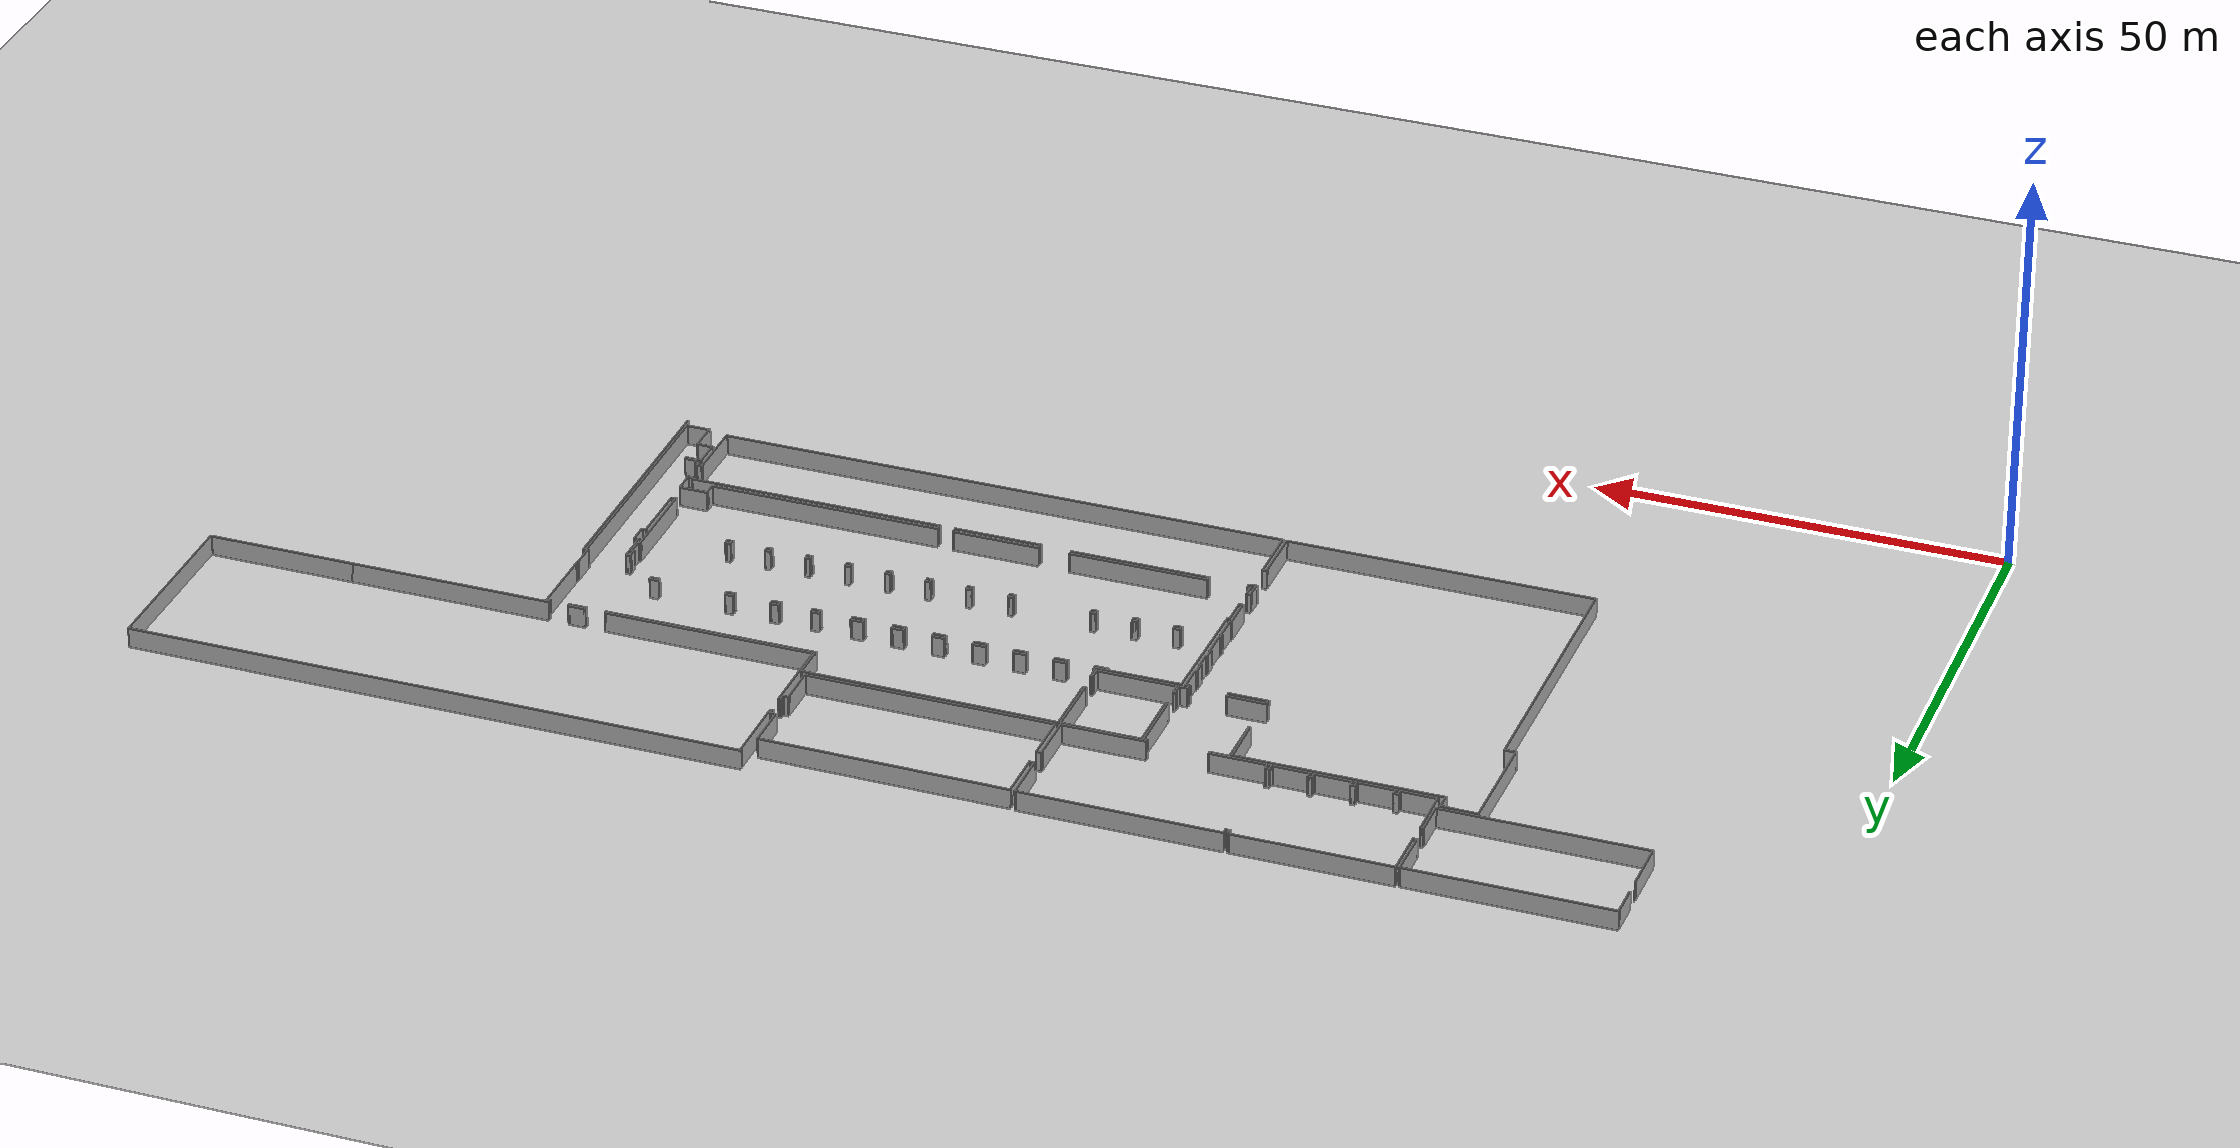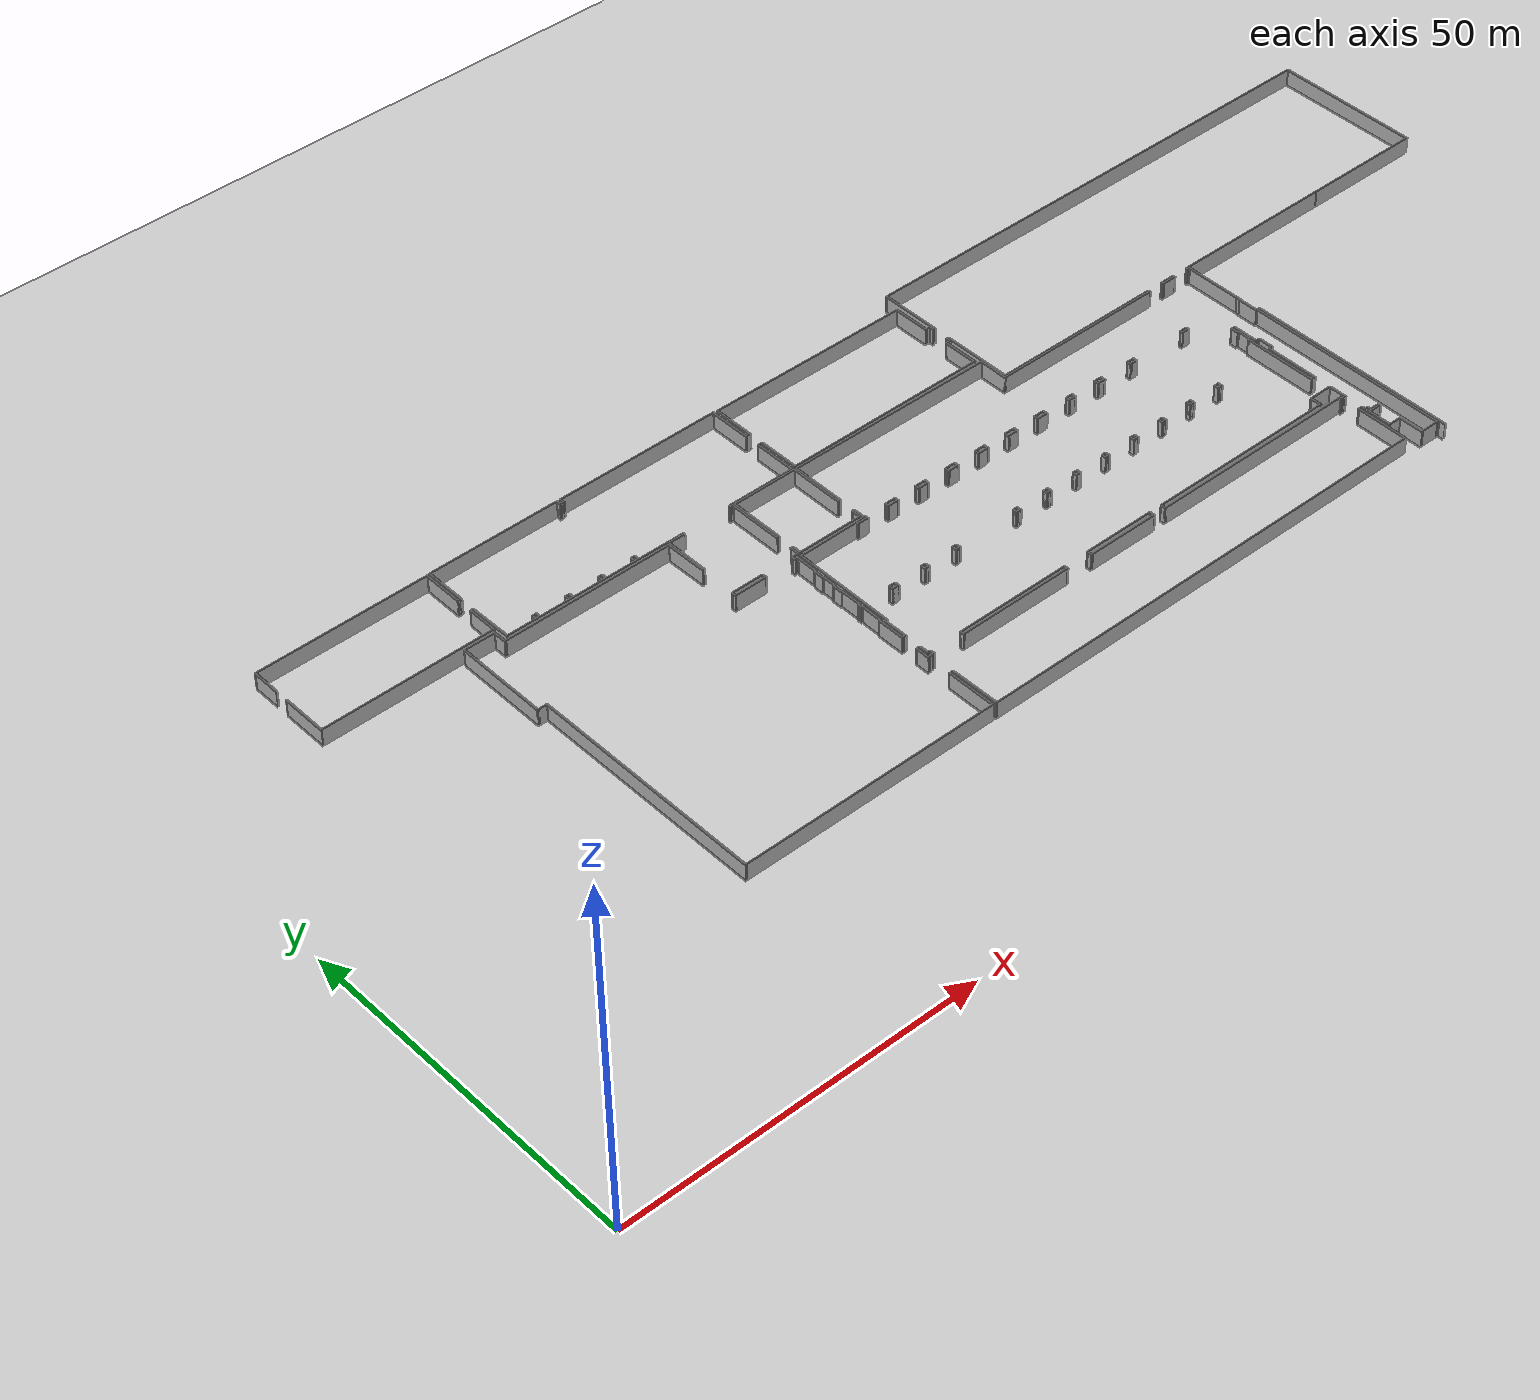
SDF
<sdf version='1.6'>
  <world name='default'>
    <light name='sun' type='directional'>
      <cast_shadows>1</cast_shadows>
      <pose frame=''>0 0 10 0 -0 0</pose>
      <diffuse>0.8 0.8 0.8 1</diffuse>
      <specular>0.1 0.1 0.1 1</specular>
      <attenuation>
        <range>1000</range>
        <constant>0.9</constant>
        <linear>0.01</linear>
        <quadratic>0.001</quadratic>
      </attenuation>
      <direction>-0.5 0.5 -1</direction>
    </light>
    <model name='ground_plane'>
      <static>1</static>
      <link name='link'>
        <collision name='collision'>
          <geometry>
            <plane>
              <normal>0 0 1</normal>
              <size>200 100</size>
            </plane>
          </geometry>
          <surface>
            <friction>
              <ode>
                <mu>100</mu>
                <mu2>50</mu2>
              </ode>
              <torsional>
                <ode/>
              </torsional>
            </friction>
            <contact>
              <ode/>
            </contact>
            <bounce/>
          </surface>
          <max_contacts>10</max_contacts>
        </collision>
        <visual name='visual'>
          <cast_shadows>0</cast_shadows>
          <geometry>
            <plane>
              <normal>0 0 1</normal>
              <size>200 100</size>
            </plane>
          </geometry>
          <material>
            <script>
              <uri>file://media/materials/scripts/gazebo.material</uri>
              <name>Gazebo/Grey</name>
            </script>
          </material>
        </visual>
        <self_collide>0</self_collide>
        <kinematic>0</kinematic>
        <gravity>1</gravity>
      </link>
    </model>
    <gravity>0 0 -9.8</gravity>
    <magnetic_field>6e-06 2.3e-05 -4.2e-05</magnetic_field>
    <atmosphere type='adiabatic'/>
    <physics name='default_physics' default='0' type='ode'>
      <max_step_size>0.001</max_step_size>
      <real_time_factor>1</real_time_factor>
      <real_time_update_rate>1000</real_time_update_rate>
    </physics>
    <scene>
      <ambient>0.4 0.4 0.4 1</ambient>
      <background>0.7 0.7 0.7 1</background>
      <shadows>0</shadows>
    </scene>
    <spherical_coordinates>
      <surface_model>EARTH_WGS84</surface_model>
      <latitude_deg>0</latitude_deg>
      <longitude_deg>0</longitude_deg>
      <elevation>0</elevation>
      <heading_deg>0</heading_deg>
    </spherical_coordinates>

    <model name='vgke_production'>
      <link name='Wall_104'>
        <pose frame=''>-53.3163 29.9969 0 0 -0 1.5808</pose>
        <visual name='Wall_104_Visual'>
          <pose frame=''>0 0 1.25 0 -0 0</pose>
          <geometry>
            <box>
              <size>6.42774 0.15 2.5</size>
            </box>
          </geometry>
          <material>
            <script>
            </script>
          </material>
        </visual>
        <collision name='Wall_104_Collision'>
          <pose frame=''>0 0 1.25 0 -0 0</pose>
          <geometry>
            <box>
              <size>6.42774 0.15 2.5</size>
            </box>
          </geometry>
          <max_contacts>10</max_contacts>
          <surface>
            <contact>
              <ode/>
            </contact>
            <bounce/>
            <friction>
              <torsional>
                <ode/>
              </torsional>
              <ode/>
            </friction>
          </surface>
        </collision>
        <self_collide>0</self_collide>
        <inertial>
          <inertia>
            <ixx>1</ixx>
            <ixy>0</ixy>
            <ixz>0</ixz>
            <iyy>1</iyy>
            <iyz>0</iyz>
            <izz>1</izz>
          </inertia>
          <mass>1</mass>
        </inertial>
        <kinematic>0</kinematic>
        <gravity>1</gravity>
      </link>
      <link name='Wall_110'>
        <pose frame=''>-54.0352 27.3522 0 0 -0 1.5708</pose>
        <visual name='Wall_110_Visual'>
          <pose frame=''>0 0 1.25 0 -0 0</pose>
          <geometry>
            <box>
              <size>2.25 0.15 2.5</size>
            </box>
          </geometry>
          <material>
            <script>
            </script>
          </material>
        </visual>
        <collision name='Wall_110_Collision'>
          <pose frame=''>0 0 1.25 0 -0 0</pose>
          <geometry>
            <box>
              <size>2.25 0.15 2.5</size>
            </box>
          </geometry>
          <max_contacts>10</max_contacts>
          <surface>
            <contact>
              <ode/>
            </contact>
            <bounce/>
            <friction>
              <torsional>
                <ode/>
              </torsional>
              <ode/>
            </friction>
          </surface>
        </collision>
        <self_collide>0</self_collide>
        <inertial>
          <inertia>
            <ixx>1</ixx>
            <ixy>0</ixy>
            <ixz>0</ixz>
            <iyy>1</iyy>
            <iyz>0</iyz>
            <izz>1</izz>
          </inertia>
          <mass>1</mass>
        </inertial>
        <kinematic>0</kinematic>
        <gravity>1</gravity>
      </link>
      <link name='Wall_112'>
        <pose frame=''>-56.2152 28.2522 0 0 0 -0.006883</pose>
        <visual name='Wall_112_Visual'>
          <pose frame=''>0 0 1.25 0 -0 0</pose>
          <geometry>
            <box>
              <size>4.51595 0.15 2.5</size>
            </box>
          </geometry>
          <material>
            <script>
            </script>
          </material>
        </visual>
        <collision name='Wall_112_Collision'>
          <pose frame=''>0 0 1.25 0 -0 0</pose>
          <geometry>
            <box>
              <size>4.51595 0.15 2.5</size>
            </box>
          </geometry>
          <max_contacts>10</max_contacts>
          <surface>
            <contact>
              <ode/>
            </contact>
            <bounce/>
            <friction>
              <torsional>
                <ode/>
              </torsional>
              <ode/>
            </friction>
          </surface>
        </collision>
        <self_collide>0</self_collide>
        <inertial>
          <inertia>
            <ixx>1</ixx>
            <ixy>0</ixy>
            <ixz>0</ixz>
            <iyy>1</iyy>
            <iyz>0</iyz>
            <izz>1</izz>
          </inertia>
          <mass>1</mass>
        </inertial>
        <kinematic>0</kinematic>
        <gravity>1</gravity>
      </link>
      <link name='Wall_114'>
        <pose frame=''>-58.4637 21.5223 0 0 0 -1.57534</pose>
        <visual name='Wall_114_Visual'>
          <pose frame=''>0 0 1.25 0 -0 0</pose>
          <geometry>
            <box>
              <size>13.6048 0.15 2.5</size>
            </box>
          </geometry>
          <material>
            <script>
            </script>
          </material>
        </visual>
        <collision name='Wall_114_Collision'>
          <pose frame=''>0 0 1.25 0 -0 0</pose>
          <geometry>
            <box>
              <size>13.6048 0.15 2.5</size>
            </box>
          </geometry>
          <max_contacts>10</max_contacts>
          <surface>
            <contact>
              <ode/>
            </contact>
            <bounce/>
            <friction>
              <torsional>
                <ode/>
              </torsional>
              <ode/>
            </friction>
          </surface>
        </collision>
        <self_collide>0</self_collide>
        <inertial>
          <inertia>
            <ixx>1</ixx>
            <ixy>0</ixy>
            <ixz>0</ixz>
            <iyy>1</iyy>
            <iyz>0</iyz>
            <izz>1</izz>
          </inertia>
          <mass>1</mass>
        </inertial>
        <kinematic>0</kinematic>
        <gravity>1</gravity>
      </link>
      <link name='Wall_116'>
        <pose frame=''>-57.8193 14.795 0 0 -0 0</pose>
        <visual name='Wall_116_Visual'>
          <pose frame=''>0 0 1.25 0 -0 0</pose>
          <geometry>
            <box>
              <size>1.5 0.15 2.5</size>
            </box>
          </geometry>
          <material>
            <script>
            </script>
          </material>
        </visual>
        <collision name='Wall_116_Collision'>
          <pose frame=''>0 0 1.25 0 -0 0</pose>
          <geometry>
            <box>
              <size>1.5 0.15 2.5</size>
            </box>
          </geometry>
          <max_contacts>10</max_contacts>
          <surface>
            <contact>
              <ode/>
            </contact>
            <bounce/>
            <friction>
              <torsional>
                <ode/>
              </torsional>
              <ode/>
            </friction>
          </surface>
        </collision>
        <self_collide>0</self_collide>
        <inertial>
          <inertia>
            <ixx>1</ixx>
            <ixy>0</ixy>
            <ixz>0</ixz>
            <iyy>1</iyy>
            <iyz>0</iyz>
            <izz>1</izz>
          </inertia>
          <mass>1</mass>
        </inertial>
        <kinematic>0</kinematic>
        <gravity>1</gravity>
      </link>
      <link name='Wall_119'>
        <pose frame=''>-57.1443 -2.38003 0 0 0 -1.5708</pose>
        <visual name='Wall_119_Visual'>
          <pose frame=''>0 0 1.25 0 -0 0</pose>
          <geometry>
            <box>
              <size>34.5 0.15 2.5</size>
            </box>
          </geometry>
          <material>
            <script>
            </script>
          </material>
        </visual>
        <collision name='Wall_119_Collision'>
          <pose frame=''>0 0 1.25 0 -0 0</pose>
          <geometry>
            <box>
              <size>34.5 0.15 2.5</size>
            </box>
          </geometry>
          <max_contacts>10</max_contacts>
          <surface>
            <contact>
              <ode/>
            </contact>
            <bounce/>
            <friction>
              <torsional>
                <ode/>
              </torsional>
              <ode/>
            </friction>
          </surface>
        </collision>
        <self_collide>0</self_collide>
        <inertial>
          <inertia>
            <ixx>1</ixx>
            <ixy>0</ixy>
            <ixz>0</ixz>
            <iyy>1</iyy>
            <iyz>0</iyz>
            <izz>1</izz>
          </inertia>
          <mass>1</mass>
        </inertial>
        <kinematic>0</kinematic>
        <gravity>1</gravity>
      </link>
      <link name='Wall_12'>
        <pose frame=''>50.1996 -15.7948 0 0 -0 1.56852</pose>
        <visual name='Wall_12_Visual'>
          <pose frame=''>0 0 1.25 0 -0 0</pose>
          <geometry>
            <box>
              <size>7.80179 0.15 2.5</size>
            </box>
          </geometry>
          <material>
            <script>
            </script>
          </material>
        </visual>
        <collision name='Wall_12_Collision'>
          <pose frame=''>0 0 1.25 0 -0 0</pose>
          <geometry>
            <box>
              <size>7.80179 0.15 2.5</size>
            </box>
          </geometry>
          <max_contacts>10</max_contacts>
          <surface>
            <contact>
              <ode/>
            </contact>
            <bounce/>
            <friction>
              <torsional>
                <ode/>
              </torsional>
              <ode/>
            </friction>
          </surface>
        </collision>
        <self_collide>0</self_collide>
        <inertial>
          <inertia>
            <ixx>1</ixx>
            <ixy>0</ixy>
            <ixz>0</ixz>
            <iyy>1</iyy>
            <iyz>0</iyz>
            <izz>1</izz>
          </inertia>
          <mass>1</mass>
        </inertial>
        <kinematic>0</kinematic>
        <gravity>1</gravity>
      </link>
      <link name='Wall_122'>
        <pose frame=''>-38.4693 -19.555 0 0 -0 0</pose>
        <visual name='Wall_122_Visual'>
          <pose frame=''>0 0 1.25 0 -0 0</pose>
          <geometry>
            <box>
              <size>37.5 0.15 2.5</size>
            </box>
          </geometry>
          <material>
            <script>
            </script>
          </material>
        </visual>
        <collision name='Wall_122_Collision'>
          <pose frame=''>0 0 1.25 0 -0 0</pose>
          <geometry>
            <box>
              <size>37.5 0.15 2.5</size>
            </box>
          </geometry>
          <max_contacts>10</max_contacts>
          <surface>
            <contact>
              <ode/>
            </contact>
            <bounce/>
            <friction>
              <torsional>
                <ode/>
              </torsional>
              <ode/>
            </friction>
          </surface>
        </collision>
        <self_collide>0</self_collide>
        <inertial>
          <inertia>
            <ixx>1</ixx>
            <ixy>0</ixy>
            <ixz>0</ixz>
            <iyy>1</iyy>
            <iyz>0</iyz>
            <izz>1</izz>
          </inertia>
          <mass>1</mass>
        </inertial>
        <kinematic>0</kinematic>
        <gravity>1</gravity>
      </link>
      <link name='Wall_131'>
        <pose frame=''>-19.7952 -15.9715 0 0 -0 1.57104</pose>
        <visual name='Wall_131_Visual'>
          <pose frame=''>0 0 1.25 0 -0 0</pose>
          <geometry>
            <box>
              <size>7.18093 0.15 2.5</size>
            </box>
          </geometry>
          <material>
            <script>
            </script>
          </material>
        </visual>
        <collision name='Wall_131_Collision'>
          <pose frame=''>0 0 1.25 0 -0 0</pose>
          <geometry>
            <box>
              <size>7.18093 0.15 2.5</size>
            </box>
          </geometry>
          <max_contacts>10</max_contacts>
          <surface>
            <contact>
              <ode/>
            </contact>
            <bounce/>
            <friction>
              <torsional>
                <ode/>
              </torsional>
              <ode/>
            </friction>
          </surface>
        </collision>
        <self_collide>0</self_collide>
        <inertial>
          <inertia>
            <ixx>1</ixx>
            <ixy>0</ixy>
            <ixz>0</ixz>
            <iyy>1</iyy>
            <iyz>0</iyz>
            <izz>1</izz>
          </inertia>
          <mass>1</mass>
        </inertial>
        <kinematic>0</kinematic>
        <gravity>1</gravity>
      </link>
      <link name='Wall_132'>
        <pose frame=''>-19.5644 -12.4406 0 0 0 -0.001832</pose>
        <visual name='Wall_132_Visual'>
          <pose frame=''>0 0 1.25 0 -0 0</pose>
          <geometry>
            <box>
              <size>0.613353 0.15 2.5</size>
            </box>
          </geometry>
          <material>
            <script>
            </script>
          </material>
        </visual>
        <collision name='Wall_132_Collision'>
          <pose frame=''>0 0 1.25 0 -0 0</pose>
          <geometry>
            <box>
              <size>0.613353 0.15 2.5</size>
            </box>
          </geometry>
          <max_contacts>10</max_contacts>
          <surface>
            <contact>
              <ode/>
            </contact>
            <bounce/>
            <friction>
              <torsional>
                <ode/>
              </torsional>
              <ode/>
            </friction>
          </surface>
        </collision>
        <self_collide>0</self_collide>
        <inertial>
          <inertia>
            <ixx>1</ixx>
            <ixy>0</ixy>
            <ixz>0</ixz>
            <iyy>1</iyy>
            <iyz>0</iyz>
            <izz>1</izz>
          </inertia>
          <mass>1</mass>
        </inertial>
        <kinematic>0</kinematic>
        <gravity>1</gravity>
      </link>
      <link name='Wall_134'>
        <pose frame=''>-19.3014 -16.018 0 0 0 -1.56394</pose>
        <visual name='Wall_134_Visual'>
          <pose frame=''>0 0 1.25 0 -0 0</pose>
          <geometry>
            <box>
              <size>7.25475 0.15 2.5</size>
            </box>
          </geometry>
          <material>
            <script>
            </script>
          </material>
        </visual>
        <collision name='Wall_134_Collision'>
          <pose frame=''>0 0 1.25 0 -0 0</pose>
          <geometry>
            <box>
              <size>7.25475 0.15 2.5</size>
            </box>
          </geometry>
          <max_contacts>10</max_contacts>
          <surface>
            <contact>
              <ode/>
            </contact>
            <bounce/>
            <friction>
              <torsional>
                <ode/>
              </torsional>
              <ode/>
            </friction>
          </surface>
        </collision>
        <self_collide>0</self_collide>
        <inertial>
          <inertia>
            <ixx>1</ixx>
            <ixy>0</ixy>
            <ixz>0</ixz>
            <iyy>1</iyy>
            <iyz>0</iyz>
            <izz>1</izz>
          </inertia>
          <mass>1</mass>
        </inertial>
        <kinematic>0</kinematic>
        <gravity>1</gravity>
      </link>
      <link name='Wall_138'>
        <pose frame=''>50.4745 -9.20167 0 0 -0 0</pose>
        <visual name='Wall_138_Visual'>
          <pose frame=''>0 0 1.25 0 -0 0</pose>
          <geometry>
            <box>
              <size>0.720907 0.15 2.5</size>
            </box>
          </geometry>
          <material>
            <script>
            </script>
          </material>
        </visual>
        <collision name='Wall_138_Collision'>
          <pose frame=''>0 0 1.25 0 -0 0</pose>
          <geometry>
            <box>
              <size>0.720907 0.15 2.5</size>
            </box>
          </geometry>
          <max_contacts>10</max_contacts>
          <surface>
            <contact>
              <ode/>
            </contact>
            <bounce/>
            <friction>
              <torsional>
                <ode/>
              </torsional>
              <ode/>
            </friction>
          </surface>
        </collision>
        <self_collide>0</self_collide>
        <inertial>
          <inertia>
            <ixx>1</ixx>
            <ixy>0</ixy>
            <ixz>0</ixz>
            <iyy>1</iyy>
            <iyz>0</iyz>
            <izz>1</izz>
          </inertia>
          <mass>1</mass>
        </inertial>
        <kinematic>0</kinematic>
        <gravity>1</gravity>
      </link>
      <link name='Wall_14'>
        <pose frame=''>50.475 -11.9697 0 0 0 -0.002665</pose>
        <visual name='Wall_14_Visual'>
          <pose frame=''>0 0 1.25 0 -0 0</pose>
          <geometry>
            <box>
              <size>0.683464 0.15 2.5</size>
            </box>
          </geometry>
          <material>
            <script>
            </script>
          </material>
        </visual>
        <collision name='Wall_14_Collision'>
          <pose frame=''>0 0 1.25 0 -0 0</pose>
          <geometry>
            <box>
              <size>0.683464 0.15 2.5</size>
            </box>
          </geometry>
          <max_contacts>10</max_contacts>
          <surface>
            <contact>
              <ode/>
            </contact>
            <bounce/>
            <friction>
              <torsional>
                <ode/>
              </torsional>
              <ode/>
            </friction>
          </surface>
        </collision>
        <self_collide>0</self_collide>
        <inertial>
          <inertia>
            <ixx>1</ixx>
            <ixy>0</ixy>
            <ixz>0</ixz>
            <iyy>1</iyy>
            <iyz>0</iyz>
            <izz>1</izz>
          </inertia>
          <mass>1</mass>
        </inertial>
        <kinematic>0</kinematic>
        <gravity>1</gravity>
      </link>
      <link name='Wall_140'>
        <pose frame=''>50.76 -7.90167 0 0 -0 1.5708</pose>
        <visual name='Wall_140_Visual'>
          <pose frame=''>0 0 1.25 0 -0 0</pose>
          <geometry>
            <box>
              <size>2.75 0.15 2.5</size>
            </box>
          </geometry>
          <material>
            <script>
            </script>
          </material>
        </visual>
        <collision name='Wall_140_Collision'>
          <pose frame=''>0 0 1.25 0 -0 0</pose>
          <geometry>
            <box>
              <size>2.75 0.15 2.5</size>
            </box>
          </geometry>
          <max_contacts>10</max_contacts>
          <surface>
            <contact>
              <ode/>
            </contact>
            <bounce/>
            <friction>
              <torsional>
                <ode/>
              </torsional>
              <ode/>
            </friction>
          </surface>
        </collision>
        <self_collide>0</self_collide>
        <inertial>
          <inertia>
            <ixx>1</ixx>
            <ixy>0</ixy>
            <ixz>0</ixz>
            <iyy>1</iyy>
            <iyz>0</iyz>
            <izz>1</izz>
          </inertia>
          <mass>1</mass>
        </inertial>
        <kinematic>0</kinematic>
        <gravity>1</gravity>
      </link>
      <link name='Wall_141'>
        <pose frame=''>49.0433 -6.60058 0 0 -0 3.14096</pose>
        <visual name='Wall_141_Visual'>
          <pose frame=''>0 0 1.25 0 -0 0</pose>
          <geometry>
            <box>
              <size>3.58336 0.15 2.5</size>
            </box>
          </geometry>
          <material>
            <script>
            </script>
          </material>
        </visual>
        <collision name='Wall_141_Collision'>
          <pose frame=''>0 0 1.25 0 -0 0</pose>
          <geometry>
            <box>
              <size>3.58336 0.15 2.5</size>
            </box>
          </geometry>
          <max_contacts>10</max_contacts>
          <surface>
            <contact>
              <ode/>
            </contact>
            <bounce/>
            <friction>
              <torsional>
                <ode/>
              </torsional>
              <ode/>
            </friction>
          </surface>
        </collision>
        <self_collide>0</self_collide>
        <inertial>
          <inertia>
            <ixx>1</ixx>
            <ixy>0</ixy>
            <ixz>0</ixz>
            <iyy>1</iyy>
            <iyz>0</iyz>
            <izz>1</izz>
          </inertia>
          <mass>1</mass>
        </inertial>
        <kinematic>0</kinematic>
        <gravity>1</gravity>
      </link>
      <link name='Wall_145'>
        <pose frame=''>47.3262 -7.39589 0 0 0 -1.57134</pose>
        <visual name='Wall_145_Visual'>
          <pose frame=''>0 0 1.25 0 -0 0</pose>
          <geometry>
            <box>
              <size>1.74298 0.15 2.5</size>
            </box>
          </geometry>
          <material>
            <script>
            </script>
          </material>
        </visual>
        <collision name='Wall_145_Collision'>
          <pose frame=''>0 0 1.25 0 -0 0</pose>
          <geometry>
            <box>
              <size>1.74298 0.15 2.5</size>
            </box>
          </geometry>
          <max_contacts>10</max_contacts>
          <surface>
            <contact>
              <ode/>
            </contact>
            <bounce/>
            <friction>
              <torsional>
                <ode/>
              </torsional>
              <ode/>
            </friction>
          </surface>
        </collision>
        <self_collide>0</self_collide>
        <inertial>
          <inertia>
            <ixx>1</ixx>
            <ixy>0</ixy>
            <ixz>0</ixz>
            <iyy>1</iyy>
            <iyz>0</iyz>
            <izz>1</izz>
          </inertia>
          <mass>1</mass>
        </inertial>
        <kinematic>0</kinematic>
        <gravity>1</gravity>
      </link>
      <link name='Wall_146'>
        <pose frame=''>33.2248 -8.19956 0 0 0 -3.14108</pose>
        <visual name='Wall_146_Visual'>
          <pose frame=''>0 0 1.25 0 -0 0</pose>
          <geometry>
            <box>
              <size>28.3519 0.15 2.5</size>
            </box>
          </geometry>
          <material>
            <script>
            </script>
          </material>
        </visual>
        <collision name='Wall_146_Collision'>
          <pose frame=''>0 0 1.25 0 -0 0</pose>
          <geometry>
            <box>
              <size>28.3519 0.15 2.5</size>
            </box>
          </geometry>
          <max_contacts>10</max_contacts>
          <surface>
            <contact>
              <ode/>
            </contact>
            <bounce/>
            <friction>
              <torsional>
                <ode/>
              </torsional>
              <ode/>
            </friction>
          </surface>
        </collision>
        <self_collide>0</self_collide>
        <inertial>
          <inertia>
            <ixx>1</ixx>
            <ixy>0</ixy>
            <ixz>0</ixz>
            <iyy>1</iyy>
            <iyz>0</iyz>
            <izz>1</izz>
          </inertia>
          <mass>1</mass>
        </inertial>
        <kinematic>0</kinematic>
        <gravity>1</gravity>
      </link>
      <link name='Wall_149'>
        <pose frame=''>19.1218 -8.55522 0 0 0 -1.57672</pose>
        <visual name='Wall_149_Visual'>
          <pose frame=''>0 0 1.25 0 -0 0</pose>
          <geometry>
            <box>
              <size>0.84686 0.15 2.5</size>
            </box>
          </geometry>
          <material>
            <script>
            </script>
          </material>
        </visual>
        <collision name='Wall_149_Collision'>
          <pose frame=''>0 0 1.25 0 -0 0</pose>
          <geometry>
            <box>
              <size>0.84686 0.15 2.5</size>
            </box>
          </geometry>
          <max_contacts>10</max_contacts>
          <surface>
            <contact>
              <ode/>
            </contact>
            <bounce/>
            <friction>
              <torsional>
                <ode/>
              </torsional>
              <ode/>
            </friction>
          </surface>
        </collision>
        <self_collide>0</self_collide>
        <inertial>
          <inertia>
            <ixx>1</ixx>
            <ixy>0</ixy>
            <ixz>0</ixz>
            <iyy>1</iyy>
            <iyz>0</iyz>
            <izz>1</izz>
          </inertia>
          <mass>1</mass>
        </inertial>
        <kinematic>0</kinematic>
        <gravity>1</gravity>
      </link>
      <link name='Wall_15'>
        <pose frame=''>50.7471 -12.2307 0 0 0 -1.5708</pose>
        <visual name='Wall_15_Visual'>
          <pose frame=''>0 0 1.25 0 -0 0</pose>
          <geometry>
            <box>
              <size>0.659957 0.15 2.5</size>
            </box>
          </geometry>
          <material>
            <script>
            </script>
          </material>
        </visual>
        <collision name='Wall_15_Collision'>
          <pose frame=''>0 0 1.25 0 -0 0</pose>
          <geometry>
            <box>
              <size>0.659957 0.15 2.5</size>
            </box>
          </geometry>
          <max_contacts>10</max_contacts>
          <surface>
            <contact>
              <ode/>
            </contact>
            <bounce/>
            <friction>
              <torsional>
                <ode/>
              </torsional>
              <ode/>
            </friction>
          </surface>
        </collision>
        <self_collide>0</self_collide>
        <inertial>
          <inertia>
            <ixx>1</ixx>
            <ixy>0</ixy>
            <ixz>0</ixz>
            <iyy>1</iyy>
            <iyz>0</iyz>
            <izz>1</izz>
          </inertia>
          <mass>1</mass>
        </inertial>
        <kinematic>0</kinematic>
        <gravity>1</gravity>
      </link>
      <link name='Wall_151'>
        <pose frame=''>34.6412 -8.90508 0 0 0 -9.4e-05</pose>
        <visual name='Wall_151_Visual'>
          <pose frame=''>0 0 1.25 0 -0 0</pose>
          <geometry>
            <box>
              <size>31.1928 0.15 2.5</size>
            </box>
          </geometry>
          <material>
            <script>
            </script>
          </material>
        </visual>
        <collision name='Wall_151_Collision'>
          <pose frame=''>0 0 1.25 0 -0 0</pose>
          <geometry>
            <box>
              <size>31.1928 0.15 2.5</size>
            </box>
          </geometry>
          <max_contacts>10</max_contacts>
          <surface>
            <contact>
              <ode/>
            </contact>
            <bounce/>
            <friction>
              <torsional>
                <ode/>
              </torsional>
              <ode/>
            </friction>
          </surface>
        </collision>
        <self_collide>0</self_collide>
        <inertial>
          <inertia>
            <ixx>1</ixx>
            <ixy>0</ixy>
            <ixz>0</ixz>
            <iyy>1</iyy>
            <iyz>0</iyz>
            <izz>1</izz>
          </inertia>
          <mass>1</mass>
        </inertial>
        <kinematic>0</kinematic>
        <gravity>1</gravity>
      </link>
      <link name='Wall_153'>
        <pose frame=''>50.1639 -9.05602 0 0 0 -1.56162</pose>
        <visual name='Wall_153_Visual'>
          <pose frame=''>0 0 1.25 0 -0 0</pose>
          <geometry>
            <box>
              <size>0.448969 0.15 2.5</size>
            </box>
          </geometry>
          <material>
            <script>
            </script>
          </material>
        </visual>
        <collision name='Wall_153_Collision'>
          <pose frame=''>0 0 1.25 0 -0 0</pose>
          <geometry>
            <box>
              <size>0.448969 0.15 2.5</size>
            </box>
          </geometry>
          <max_contacts>10</max_contacts>
          <surface>
            <contact>
              <ode/>
            </contact>
            <bounce/>
            <friction>
              <torsional>
                <ode/>
              </torsional>
              <ode/>
            </friction>
          </surface>
        </collision>
        <self_collide>0</self_collide>
        <inertial>
          <inertia>
            <ixx>1</ixx>
            <ixy>0</ixy>
            <ixz>0</ixz>
            <iyy>1</iyy>
            <iyz>0</iyz>
            <izz>1</izz>
          </inertia>
          <mass>1</mass>
        </inertial>
        <kinematic>0</kinematic>
        <gravity>1</gravity>
      </link>
      <link name='Wall_155'>
        <pose frame=''>6.6402 -8.55667 0 0 0 -1.5708</pose>
        <visual name='Wall_155_Visual'>
          <pose frame=''>0 0 1.25 0 -0 0</pose>
          <geometry>
            <box>
              <size>0.852564 0.15 2.5</size>
            </box>
          </geometry>
          <material>
            <script>
            </script>
          </material>
        </visual>
        <collision name='Wall_155_Collision'>
          <pose frame=''>0 0 1.25 0 -0 0</pose>
          <geometry>
            <box>
              <size>0.852564 0.15 2.5</size>
            </box>
          </geometry>
          <max_contacts>10</max_contacts>
          <surface>
            <contact>
              <ode/>
            </contact>
            <bounce/>
            <friction>
              <torsional>
                <ode/>
              </torsional>
              <ode/>
            </friction>
          </surface>
        </collision>
        <self_collide>0</self_collide>
        <inertial>
          <inertia>
            <ixx>1</ixx>
            <ixy>0</ixy>
            <ixz>0</ixz>
            <iyy>1</iyy>
            <iyz>0</iyz>
            <izz>1</izz>
          </inertia>
          <mass>1</mass>
        </inertial>
        <kinematic>0</kinematic>
        <gravity>1</gravity>
      </link>
      <link name='Wall_156'>
        <pose frame=''>11.9083 -8.90841 0 0 0 -8.9e-05</pose>
        <visual name='Wall_156_Visual'>
          <pose frame=''>0 0 1.25 0 -0 0</pose>
          <geometry>
            <box>
              <size>10.6863 0.15 2.5</size>
            </box>
          </geometry>
          <material>
            <script>
            </script>
          </material>
        </visual>
        <collision name='Wall_156_Collision'>
          <pose frame=''>0 0 1.25 0 -0 0</pose>
          <geometry>
            <box>
              <size>10.6863 0.15 2.5</size>
            </box>
          </geometry>
          <max_contacts>10</max_contacts>
          <surface>
            <contact>
              <ode/>
            </contact>
            <bounce/>
            <friction>
              <torsional>
                <ode/>
              </torsional>
              <ode/>
            </friction>
          </surface>
        </collision>
        <self_collide>0</self_collide>
        <inertial>
          <inertia>
            <ixx>1</ixx>
            <ixy>0</ixy>
            <ixz>0</ixz>
            <iyy>1</iyy>
            <iyz>0</iyz>
            <izz>1</izz>
          </inertia>
          <mass>1</mass>
        </inertial>
        <kinematic>0</kinematic>
        <gravity>1</gravity>
      </link>
      <link name='Wall_158'>
        <pose frame=''>17.1783 -8.55161 0 0 -0 1.56583</pose>
        <visual name='Wall_158_Visual'>
          <pose frame=''>0 0 1.25 0 -0 0</pose>
          <geometry>
            <box>
              <size>0.864557 0.15 2.5</size>
            </box>
          </geometry>
          <material>
            <script>
            </script>
          </material>
        </visual>
        <collision name='Wall_158_Collision'>
          <pose frame=''>0 0 1.25 0 -0 0</pose>
          <geometry>
            <box>
              <size>0.864557 0.15 2.5</size>
            </box>
          </geometry>
          <max_contacts>10</max_contacts>
          <surface>
            <contact>
              <ode/>
            </contact>
            <bounce/>
            <friction>
              <torsional>
                <ode/>
              </torsional>
              <ode/>
            </friction>
          </surface>
        </collision>
        <self_collide>0</self_collide>
        <inertial>
          <inertia>
            <ixx>1</ixx>
            <ixy>0</ixy>
            <ixz>0</ixz>
            <iyy>1</iyy>
            <iyz>0</iyz>
            <izz>1</izz>
          </inertia>
          <mass>1</mass>
        </inertial>
        <kinematic>0</kinematic>
        <gravity>1</gravity>
      </link>
      <link name='Wall_160'>
        <pose frame=''>11.9079 -8.1988 0 0 0 -3.14076</pose>
        <visual name='Wall_160_Visual'>
          <pose frame=''>0 0 1.25 0 -0 0</pose>
          <geometry>
            <box>
              <size>10.6947 0.15 2.5</size>
            </box>
          </geometry>
          <material>
            <script>
            </script>
          </material>
        </visual>
        <collision name='Wall_160_Collision'>
          <pose frame=''>0 0 1.25 0 -0 0</pose>
          <geometry>
            <box>
              <size>10.6947 0.15 2.5</size>
            </box>
          </geometry>
          <max_contacts>10</max_contacts>
          <surface>
            <contact>
              <ode/>
            </contact>
            <bounce/>
            <friction>
              <torsional>
                <ode/>
              </torsional>
              <ode/>
            </friction>
          </surface>
        </collision>
        <self_collide>0</self_collide>
        <inertial>
          <inertia>
            <ixx>1</ixx>
            <ixy>0</ixy>
            <ixz>0</ixz>
            <iyy>1</iyy>
            <iyz>0</iyz>
            <izz>1</izz>
          </inertia>
          <mass>1</mass>
        </inertial>
        <kinematic>0</kinematic>
        <gravity>1</gravity>
      </link>
      <link name='Wall_162'>
        <pose frame=''>-19.5889 -8.88211 0 0 -0 0</pose>
        <visual name='Wall_162_Visual'>
          <pose frame=''>0 0 1.25 0 -0 0</pose>
          <geometry>
            <box>
              <size>0.612803 0.15 2.5</size>
            </box>
          </geometry>
          <material>
            <script>
            </script>
          </material>
        </visual>
        <collision name='Wall_162_Collision'>
          <pose frame=''>0 0 1.25 0 -0 0</pose>
          <geometry>
            <box>
              <size>0.612803 0.15 2.5</size>
            </box>
          </geometry>
          <max_contacts>10</max_contacts>
          <surface>
            <contact>
              <ode/>
            </contact>
            <bounce/>
            <friction>
              <torsional>
                <ode/>
              </torsional>
              <ode/>
            </friction>
          </surface>
        </collision>
        <self_collide>0</self_collide>
        <inertial>
          <inertia>
            <ixx>1</ixx>
            <ixy>0</ixy>
            <ixz>0</ixz>
            <iyy>1</iyy>
            <iyz>0</iyz>
            <izz>1</izz>
          </inertia>
          <mass>1</mass>
        </inertial>
        <kinematic>0</kinematic>
        <gravity>1</gravity>
      </link>
      <link name='Wall_164'>
        <pose frame=''>-19.7992 -7.87236 0 0 -0 1.54997</pose>
        <visual name='Wall_164_Visual'>
          <pose frame=''>0 0 1.25 0 -0 0</pose>
          <geometry>
            <box>
              <size>2.17019 0.15 2.5</size>
            </box>
          </geometry>
          <material>
            <script>
            </script>
          </material>
        </visual>
        <collision name='Wall_164_Collision'>
          <pose frame=''>0 0 1.25 0 -0 0</pose>
          <geometry>
            <box>
              <size>2.17019 0.15 2.5</size>
            </box>
          </geometry>
          <max_contacts>10</max_contacts>
          <surface>
            <contact>
              <ode/>
            </contact>
            <bounce/>
            <friction>
              <torsional>
                <ode/>
              </torsional>
              <ode/>
            </friction>
          </surface>
        </collision>
        <self_collide>0</self_collide>
        <inertial>
          <inertia>
            <ixx>1</ixx>
            <ixy>0</ixy>
            <ixz>0</ixz>
            <iyy>1</iyy>
            <iyz>0</iyz>
            <izz>1</izz>
          </inertia>
          <mass>1</mass>
        </inertial>
        <kinematic>0</kinematic>
        <gravity>1</gravity>
      </link>
      <link name='Wall_165'>
        <pose frame=''>-19.552 -6.86261 0 0 -0 0</pose>
        <visual name='Wall_165_Visual'>
          <pose frame=''>0 0 1.25 0 -0 0</pose>
          <geometry>
            <box>
              <size>0.602285 0.15 2.5</size>
            </box>
          </geometry>
          <material>
            <script>
            </script>
          </material>
        </visual>
        <collision name='Wall_165_Collision'>
          <pose frame=''>0 0 1.25 0 -0 0</pose>
          <geometry>
            <box>
              <size>0.602285 0.15 2.5</size>
            </box>
          </geometry>
          <max_contacts>10</max_contacts>
          <surface>
            <contact>
              <ode/>
            </contact>
            <bounce/>
            <friction>
              <torsional>
                <ode/>
              </torsional>
              <ode/>
            </friction>
          </surface>
        </collision>
        <self_collide>0</self_collide>
        <inertial>
          <inertia>
            <ixx>1</ixx>
            <ixy>0</ixy>
            <ixz>0</ixz>
            <iyy>1</iyy>
            <iyz>0</iyz>
            <izz>1</izz>
          </inertia>
          <mass>1</mass>
        </inertial>
        <kinematic>0</kinematic>
        <gravity>1</gravity>
      </link>
      <link name='Wall_166'>
        <pose frame=''>-19.3206 -7.52526 0 0 0 -1.56286</pose>
        <visual name='Wall_166_Visual'>
          <pose frame=''>0 0 1.25 0 -0 0</pose>
          <geometry>
            <box>
              <size>1.47534 0.15 2.5</size>
            </box>
          </geometry>
          <material>
            <script>
            </script>
          </material>
        </visual>
        <collision name='Wall_166_Collision'>
          <pose frame=''>0 0 1.25 0 -0 0</pose>
          <geometry>
            <box>
              <size>1.47534 0.15 2.5</size>
            </box>
          </geometry>
          <max_contacts>10</max_contacts>
          <surface>
            <contact>
              <ode/>
            </contact>
            <bounce/>
            <friction>
              <torsional>
                <ode/>
              </torsional>
              <ode/>
            </friction>
          </surface>
        </collision>
        <self_collide>0</self_collide>
        <inertial>
          <inertia>
            <ixx>1</ixx>
            <ixy>0</ixy>
            <ixz>0</ixz>
            <iyy>1</iyy>
            <iyz>0</iyz>
            <izz>1</izz>
          </inertia>
          <mass>1</mass>
        </inertial>
        <kinematic>0</kinematic>
        <gravity>1</gravity>
      </link>
      <link name='Wall_167'>
        <pose frame=''>-19.1039 -8.18887 0 0 0 -0.00457</pose>
        <visual name='Wall_167_Visual'>
          <pose frame=''>0 0 1.25 0 -0 0</pose>
          <geometry>
            <box>
              <size>0.572983 0.15 2.5</size>
            </box>
          </geometry>
          <material>
            <script>
            </script>
          </material>
        </visual>
        <collision name='Wall_167_Collision'>
          <pose frame=''>0 0 1.25 0 -0 0</pose>
          <geometry>
            <box>
              <size>0.572983 0.15 2.5</size>
            </box>
          </geometry>
          <max_contacts>10</max_contacts>
          <surface>
            <contact>
              <ode/>
            </contact>
            <bounce/>
            <friction>
              <torsional>
                <ode/>
              </torsional>
              <ode/>
            </friction>
          </surface>
        </collision>
        <self_collide>0</self_collide>
        <inertial>
          <inertia>
            <ixx>1</ixx>
            <ixy>0</ixy>
            <ixz>0</ixz>
            <iyy>1</iyy>
            <iyz>0</iyz>
            <izz>1</izz>
          </inertia>
          <mass>1</mass>
        </inertial>
        <kinematic>0</kinematic>
        <gravity>1</gravity>
      </link>
      <link name='Wall_168'>
        <pose frame=''>-18.8924 -8.47484 0 0 0 -1.5708</pose>
        <visual name='Wall_168_Visual'>
          <pose frame=''>0 0 1.25 0 -0 0</pose>
          <geometry>
            <box>
              <size>0.720008 0.15 2.5</size>
            </box>
          </geometry>
          <material>
            <script>
            </script>
          </material>
        </visual>
        <collision name='Wall_168_Collision'>
          <pose frame=''>0 0 1.25 0 -0 0</pose>
          <geometry>
            <box>
              <size>0.720008 0.15 2.5</size>
            </box>
          </geometry>
          <max_contacts>10</max_contacts>
          <surface>
            <contact>
              <ode/>
            </contact>
            <bounce/>
            <friction>
              <torsional>
                <ode/>
              </torsional>
              <ode/>
            </friction>
          </surface>
        </collision>
        <self_collide>0</self_collide>
        <inertial>
          <inertia>
            <ixx>1</ixx>
            <ixy>0</ixy>
            <ixz>0</ixz>
            <iyy>1</iyy>
            <iyz>0</iyz>
            <izz>1</izz>
          </inertia>
          <mass>1</mass>
        </inertial>
        <kinematic>0</kinematic>
        <gravity>1</gravity>
      </link>
      <link name='Wall_169'>
        <pose frame=''>-19.1094 -8.75985 0 0 -0 3.14159</pose>
        <visual name='Wall_169_Visual'>
          <pose frame=''>0 0 1.25 0 -0 0</pose>
          <geometry>
            <box>
              <size>0.584546 0.15 2.5</size>
            </box>
          </geometry>
          <material>
            <script>
            </script>
          </material>
        </visual>
        <collision name='Wall_169_Collision'>
          <pose frame=''>0 0 1.25 0 -0 0</pose>
          <geometry>
            <box>
              <size>0.584546 0.15 2.5</size>
            </box>
          </geometry>
          <max_contacts>10</max_contacts>
          <surface>
            <contact>
              <ode/>
            </contact>
            <bounce/>
            <friction>
              <torsional>
                <ode/>
              </torsional>
              <ode/>
            </friction>
          </surface>
        </collision>
        <self_collide>0</self_collide>
        <inertial>
          <inertia>
            <ixx>1</ixx>
            <ixy>0</ixy>
            <ixz>0</ixz>
            <iyy>1</iyy>
            <iyz>0</iyz>
            <izz>1</izz>
          </inertia>
          <mass>1</mass>
        </inertial>
        <kinematic>0</kinematic>
        <gravity>1</gravity>
      </link>
      <link name='Wall_170'>
        <pose frame=''>-19.3264 -8.81999 0 0 0 -1.5708</pose>
        <visual name='Wall_170_Visual'>
          <pose frame=''>0 0 1.25 0 -0 0</pose>
          <geometry>
            <box>
              <size>0.270277 0.15 2.5</size>
            </box>
          </geometry>
          <material>
            <script>
            </script>
          </material>
        </visual>
        <collision name='Wall_170_Collision'>
          <pose frame=''>0 0 1.25 0 -0 0</pose>
          <geometry>
            <box>
              <size>0.270277 0.15 2.5</size>
            </box>
          </geometry>
          <max_contacts>10</max_contacts>
          <surface>
            <contact>
              <ode/>
            </contact>
            <bounce/>
            <friction>
              <torsional>
                <ode/>
              </torsional>
              <ode/>
            </friction>
          </surface>
        </collision>
        <self_collide>0</self_collide>
        <inertial>
          <inertia>
            <ixx>1</ixx>
            <ixy>0</ixy>
            <ixz>0</ixz>
            <iyy>1</iyy>
            <iyz>0</iyz>
            <izz>1</izz>
          </inertia>
          <mass>1</mass>
        </inertial>
        <kinematic>0</kinematic>
        <gravity>1</gravity>
      </link>
      <link name='Wall_172'>
        <pose frame=''>-19.7146 -2.37711 0 0 0 -1.57088</pose>
        <visual name='Wall_172_Visual'>
          <pose frame=''>0 0 1.25 0 -0 0</pose>
          <geometry>
            <box>
              <size>4.15152 0.15 2.5</size>
            </box>
          </geometry>
          <material>
            <script>
            </script>
          </material>
        </visual>
        <collision name='Wall_172_Collision'>
          <pose frame=''>0 0 1.25 0 -0 0</pose>
          <geometry>
            <box>
              <size>4.15152 0.15 2.5</size>
            </box>
          </geometry>
          <max_contacts>10</max_contacts>
          <surface>
            <contact>
              <ode/>
            </contact>
            <bounce/>
            <friction>
              <torsional>
                <ode/>
              </torsional>
              <ode/>
            </friction>
          </surface>
        </collision>
        <self_collide>0</self_collide>
        <inertial>
          <inertia>
            <ixx>1</ixx>
            <ixy>0</ixy>
            <ixz>0</ixz>
            <iyy>1</iyy>
            <iyz>0</iyz>
            <izz>1</izz>
          </inertia>
          <mass>1</mass>
        </inertial>
        <kinematic>0</kinematic>
        <gravity>1</gravity>
      </link>
      <link name='Wall_174'>
        <pose frame=''>-19.504 -4.37786 0 0 -0 0</pose>
        <visual name='Wall_174_Visual'>
          <pose frame=''>0 0 1.25 0 -0 0</pose>
          <geometry>
            <box>
              <size>0.571593 0.15 2.5</size>
            </box>
          </geometry>
          <material>
            <script>
            </script>
          </material>
        </visual>
        <collision name='Wall_174_Collision'>
          <pose frame=''>0 0 1.25 0 -0 0</pose>
          <geometry>
            <box>
              <size>0.571593 0.15 2.5</size>
            </box>
          </geometry>
          <max_contacts>10</max_contacts>
          <surface>
            <contact>
              <ode/>
            </contact>
            <bounce/>
            <friction>
              <torsional>
                <ode/>
              </torsional>
              <ode/>
            </friction>
          </surface>
        </collision>
        <self_collide>0</self_collide>
        <inertial>
          <inertia>
            <ixx>1</ixx>
            <ixy>0</ixy>
            <ixz>0</ixz>
            <iyy>1</iyy>
            <iyz>0</iyz>
            <izz>1</izz>
          </inertia>
          <mass>1</mass>
        </inertial>
        <kinematic>0</kinematic>
        <gravity>1</gravity>
      </link>
      <link name='Wall_176'>
        <pose frame=''>-19.2966 -2.65977 0 0 -0 1.57275</pose>
        <visual name='Wall_176_Visual'>
          <pose frame=''>0 0 1.25 0 -0 0</pose>
          <geometry>
            <box>
              <size>3.58619 0.15 2.5</size>
            </box>
          </geometry>
          <material>
            <script>
            </script>
          </material>
        </visual>
        <collision name='Wall_176_Collision'>
          <pose frame=''>0 0 1.25 0 -0 0</pose>
          <geometry>
            <box>
              <size>3.58619 0.15 2.5</size>
            </box>
          </geometry>
          <max_contacts>10</max_contacts>
          <surface>
            <contact>
              <ode/>
            </contact>
            <bounce/>
            <friction>
              <torsional>
                <ode/>
              </torsional>
              <ode/>
            </friction>
          </surface>
        </collision>
        <self_collide>0</self_collide>
        <inertial>
          <inertia>
            <ixx>1</ixx>
            <ixy>0</ixy>
            <ixz>0</ixz>
            <iyy>1</iyy>
            <iyz>0</iyz>
            <izz>1</izz>
          </inertia>
          <mass>1</mass>
        </inertial>
        <kinematic>0</kinematic>
        <gravity>1</gravity>
      </link>
      <link name='Wall_177'>
        <pose frame=''>-19.1678 -0.941685 0 0 -0 0</pose>
        <visual name='Wall_177_Visual'>
          <pose frame=''>0 0 1.25 0 -0 0</pose>
          <geometry>
            <box>
              <size>0.414297 0.15 2.5</size>
            </box>
          </geometry>
          <material>
            <script>
            </script>
          </material>
        </visual>
        <collision name='Wall_177_Collision'>
          <pose frame=''>0 0 1.25 0 -0 0</pose>
          <geometry>
            <box>
              <size>0.414297 0.15 2.5</size>
            </box>
          </geometry>
          <max_contacts>10</max_contacts>
          <surface>
            <contact>
              <ode/>
            </contact>
            <bounce/>
            <friction>
              <torsional>
                <ode/>
              </torsional>
              <ode/>
            </friction>
          </surface>
        </collision>
        <self_collide>0</self_collide>
        <inertial>
          <inertia>
            <ixx>1</ixx>
            <ixy>0</ixy>
            <ixz>0</ixz>
            <iyy>1</iyy>
            <iyz>0</iyz>
            <izz>1</izz>
          </inertia>
          <mass>1</mass>
        </inertial>
        <kinematic>0</kinematic>
        <gravity>1</gravity>
      </link>
      <link name='Wall_179'>
        <pose frame=''>-19.6393 -0.373856 0 0 -0 0.03319</pose>
        <visual name='Wall_179_Visual'>
          <pose frame=''>0 0 1.25 0 -0 0</pose>
          <geometry>
            <box>
              <size>0.300325 0.15 2.5</size>
            </box>
          </geometry>
          <material>
            <script>
            </script>
          </material>
        </visual>
        <collision name='Wall_179_Collision'>
          <pose frame=''>0 0 1.25 0 -0 0</pose>
          <geometry>
            <box>
              <size>0.300325 0.15 2.5</size>
            </box>
          </geometry>
          <max_contacts>10</max_contacts>
          <surface>
            <contact>
              <ode/>
            </contact>
            <bounce/>
            <friction>
              <torsional>
                <ode/>
              </torsional>
              <ode/>
            </friction>
          </surface>
        </collision>
        <self_collide>0</self_collide>
        <inertial>
          <inertia>
            <ixx>1</ixx>
            <ixy>0</ixy>
            <ixz>0</ixz>
            <iyy>1</iyy>
            <iyz>0</iyz>
            <izz>1</izz>
          </inertia>
          <mass>1</mass>
        </inertial>
        <kinematic>0</kinematic>
        <gravity>1</gravity>
      </link>
      <link name='Wall_18'>
        <pose frame=''>51.0074 -12.4853 0 0 -0 0.001398</pose>
        <visual name='Wall_18_Visual'>
          <pose frame=''>0 0 1.25 0 -0 0</pose>
          <geometry>
            <box>
              <size>0.670553 0.15 2.5</size>
            </box>
          </geometry>
          <material>
            <script>
            </script>
          </material>
        </visual>
        <collision name='Wall_18_Collision'>
          <pose frame=''>0 0 1.25 0 -0 0</pose>
          <geometry>
            <box>
              <size>0.670553 0.15 2.5</size>
            </box>
          </geometry>
          <max_contacts>10</max_contacts>
          <surface>
            <contact>
              <ode/>
            </contact>
            <bounce/>
            <friction>
              <torsional>
                <ode/>
              </torsional>
              <ode/>
            </friction>
          </surface>
        </collision>
        <self_collide>0</self_collide>
        <inertial>
          <inertia>
            <ixx>1</ixx>
            <ixy>0</ixy>
            <ixz>0</ixz>
            <iyy>1</iyy>
            <iyz>0</iyz>
            <izz>1</izz>
          </inertia>
          <mass>1</mass>
        </inertial>
        <kinematic>0</kinematic>
        <gravity>1</gravity>
      </link>
      <link name='Wall_180'>
        <pose frame=''>-19.5434 1.15878 0 0 -0 1.55716</pose>
        <visual name='Wall_180_Visual'>
          <pose frame=''>0 0 1.25 0 -0 0</pose>
          <geometry>
            <box>
              <size>3.21057 0.15 2.5</size>
            </box>
          </geometry>
          <material>
            <script>
            </script>
          </material>
        </visual>
        <collision name='Wall_180_Collision'>
          <pose frame=''>0 0 1.25 0 -0 0</pose>
          <geometry>
            <box>
              <size>3.21057 0.15 2.5</size>
            </box>
          </geometry>
          <max_contacts>10</max_contacts>
          <surface>
            <contact>
              <ode/>
            </contact>
            <bounce/>
            <friction>
              <torsional>
                <ode/>
              </torsional>
              <ode/>
            </friction>
          </surface>
        </collision>
        <self_collide>0</self_collide>
        <inertial>
          <inertia>
            <ixx>1</ixx>
            <ixy>0</ixy>
            <ixz>0</ixz>
            <iyy>1</iyy>
            <iyz>0</iyz>
            <izz>1</izz>
          </inertia>
          <mass>1</mass>
        </inertial>
        <kinematic>0</kinematic>
        <gravity>1</gravity>
      </link>
      <link name='Wall_183'>
        <pose frame=''>-18.9532 6.63242 0 0 -0 1.55991</pose>
        <visual name='Wall_183_Visual'>
          <pose frame=''>0 0 1.25 0 -0 0</pose>
          <geometry>
            <box>
              <size>15.2999 0.15 2.5</size>
            </box>
          </geometry>
          <material>
            <script>
            </script>
          </material>
        </visual>
        <collision name='Wall_183_Collision'>
          <pose frame=''>0 0 1.25 0 -0 0</pose>
          <geometry>
            <box>
              <size>15.2999 0.15 2.5</size>
            </box>
          </geometry>
          <max_contacts>10</max_contacts>
          <surface>
            <contact>
              <ode/>
            </contact>
            <bounce/>
            <friction>
              <torsional>
                <ode/>
              </torsional>
              <ode/>
            </friction>
          </surface>
        </collision>
        <self_collide>0</self_collide>
        <inertial>
          <inertia>
            <ixx>1</ixx>
            <ixy>0</ixy>
            <ixz>0</ixz>
            <iyy>1</iyy>
            <iyz>0</iyz>
            <izz>1</izz>
          </inertia>
          <mass>1</mass>
        </inertial>
        <kinematic>0</kinematic>
        <gravity>1</gravity>
      </link>
      <link name='Wall_187'>
        <pose frame=''>-19.5901 2.68856 0 0 0 -3.13624</pose>
        <visual name='Wall_187_Visual'>
          <pose frame=''>0 0 1.25 0 -0 0</pose>
          <geometry>
            <box>
              <size>0.285269 0.15 2.5</size>
            </box>
          </geometry>
          <material>
            <script>
            </script>
          </material>
        </visual>
        <collision name='Wall_187_Collision'>
          <pose frame=''>0 0 1.25 0 -0 0</pose>
          <geometry>
            <box>
              <size>0.285269 0.15 2.5</size>
            </box>
          </geometry>
          <max_contacts>10</max_contacts>
          <surface>
            <contact>
              <ode/>
            </contact>
            <bounce/>
            <friction>
              <torsional>
                <ode/>
              </torsional>
              <ode/>
            </friction>
          </surface>
        </collision>
        <self_collide>0</self_collide>
        <inertial>
          <inertia>
            <ixx>1</ixx>
            <ixy>0</ixy>
            <ixz>0</ixz>
            <iyy>1</iyy>
            <iyz>0</iyz>
            <izz>1</izz>
          </inertia>
          <mass>1</mass>
        </inertial>
        <kinematic>0</kinematic>
        <gravity>1</gravity>
      </link>
      <link name='Wall_198'>
        <pose frame=''>-19.6578 2.95097 0 0 -0 1.57079</pose>
        <visual name='Wall_198_Visual'>
          <pose frame=''>0 0 1.25 0 -0 0</pose>
          <geometry>
            <box>
              <size>0.675533 0.15 2.5</size>
            </box>
          </geometry>
          <material>
            <script>
            </script>
          </material>
        </visual>
        <collision name='Wall_198_Collision'>
          <pose frame=''>0 0 1.25 0 -0 0</pose>
          <geometry>
            <box>
              <size>0.675533 0.15 2.5</size>
            </box>
          </geometry>
          <max_contacts>10</max_contacts>
          <surface>
            <contact>
              <ode/>
            </contact>
            <bounce/>
            <friction>
              <torsional>
                <ode/>
              </torsional>
              <ode/>
            </friction>
          </surface>
        </collision>
        <self_collide>0</self_collide>
        <inertial>
          <inertia>
            <ixx>1</ixx>
            <ixy>0</ixy>
            <ixz>0</ixz>
            <iyy>1</iyy>
            <iyz>0</iyz>
            <izz>1</izz>
          </inertia>
          <mass>1</mass>
        </inertial>
        <kinematic>0</kinematic>
        <gravity>1</gravity>
      </link>
      <link name='Wall_202'>
        <pose frame=''>-19.5794 3.214 0 0 -0 0.003356</pose>
        <visual name='Wall_202_Visual'>
          <pose frame=''>0 0 1.25 0 -0 0</pose>
          <geometry>
            <box>
              <size>0.306787 0.15 2.5</size>
            </box>
          </geometry>
          <material>
            <script>
            </script>
          </material>
        </visual>
        <collision name='Wall_202_Collision'>
          <pose frame=''>0 0 1.25 0 -0 0</pose>
          <geometry>
            <box>
              <size>0.306787 0.15 2.5</size>
            </box>
          </geometry>
          <max_contacts>10</max_contacts>
          <surface>
            <contact>
              <ode/>
            </contact>
            <bounce/>
            <friction>
              <torsional>
                <ode/>
              </torsional>
              <ode/>
            </friction>
          </surface>
        </collision>
        <self_collide>0</self_collide>
        <inertial>
          <inertia>
            <ixx>1</ixx>
            <ixy>0</ixy>
            <ixz>0</ixz>
            <iyy>1</iyy>
            <iyz>0</iyz>
            <izz>1</izz>
          </inertia>
          <mass>1</mass>
        </inertial>
        <kinematic>0</kinematic>
        <gravity>1</gravity>
      </link>
      <link name='Wall_205'>
        <pose frame=''>-19.498 4.77876 0 0 -0 1.56888</pose>
        <visual name='Wall_205_Visual'>
          <pose frame=''>0 0 1.25 0 -0 0</pose>
          <geometry>
            <box>
              <size>3.27901 0.15 2.5</size>
            </box>
          </geometry>
          <material>
            <script>
            </script>
          </material>
        </visual>
        <collision name='Wall_205_Collision'>
          <pose frame=''>0 0 1.25 0 -0 0</pose>
          <geometry>
            <box>
              <size>3.27901 0.15 2.5</size>
            </box>
          </geometry>
          <max_contacts>10</max_contacts>
          <surface>
            <contact>
              <ode/>
            </contact>
            <bounce/>
            <friction>
              <torsional>
                <ode/>
              </torsional>
              <ode/>
            </friction>
          </surface>
        </collision>
        <self_collide>0</self_collide>
        <inertial>
          <inertia>
            <ixx>1</ixx>
            <ixy>0</ixy>
            <ixz>0</ixz>
            <iyy>1</iyy>
            <iyz>0</iyz>
            <izz>1</izz>
          </inertia>
          <mass>1</mass>
        </inertial>
        <kinematic>0</kinematic>
        <gravity>1</gravity>
      </link>
      <link name='Wall_207'>
        <pose frame=''>-19.552 6.34405 0 0 -0 3.12773</pose>
        <visual name='Wall_207_Visual'>
          <pose frame=''>0 0 1.25 0 -0 0</pose>
          <geometry>
            <box>
              <size>0.264091 0.15 2.5</size>
            </box>
          </geometry>
          <material>
            <script>
            </script>
          </material>
        </visual>
        <collision name='Wall_207_Collision'>
          <pose frame=''>0 0 1.25 0 -0 0</pose>
          <geometry>
            <box>
              <size>0.264091 0.15 2.5</size>
            </box>
          </geometry>
          <max_contacts>10</max_contacts>
          <surface>
            <contact>
              <ode/>
            </contact>
            <bounce/>
            <friction>
              <torsional>
                <ode/>
              </torsional>
              <ode/>
            </friction>
          </surface>
        </collision>
        <self_collide>0</self_collide>
        <inertial>
          <inertia>
            <ixx>1</ixx>
            <ixy>0</ixy>
            <ixz>0</ixz>
            <iyy>1</iyy>
            <iyz>0</iyz>
            <izz>1</izz>
          </inertia>
          <mass>1</mass>
        </inertial>
        <kinematic>0</kinematic>
        <gravity>1</gravity>
      </link>
      <link name='Wall_219'>
        <pose frame=''>-19.6011 7.00947 0 0 0 -1.58826</pose>
        <visual name='Wall_219_Visual'>
          <pose frame=''>0 0 1.25 0 -0 0</pose>
          <geometry>
            <box>
              <size>1.48559 0.15 2.5</size>
            </box>
          </geometry>
          <material>
            <script>
            </script>
          </material>
        </visual>
        <collision name='Wall_219_Collision'>
          <pose frame=''>0 0 1.25 0 -0 0</pose>
          <geometry>
            <box>
              <size>1.48559 0.15 2.5</size>
            </box>
          </geometry>
          <max_contacts>10</max_contacts>
          <surface>
            <contact>
              <ode/>
            </contact>
            <bounce/>
            <friction>
              <torsional>
                <ode/>
              </torsional>
              <ode/>
            </friction>
          </surface>
        </collision>
        <self_collide>0</self_collide>
        <inertial>
          <inertia>
            <ixx>1</ixx>
            <ixy>0</ixy>
            <ixz>0</ixz>
            <iyy>1</iyy>
            <iyz>0</iyz>
            <izz>1</izz>
          </inertia>
          <mass>1</mass>
        </inertial>
        <kinematic>0</kinematic>
        <gravity>1</gravity>
      </link>
      <link name='Wall_22'>
        <pose frame=''>51.2673 -12.7335 0 0 0 -1.57201</pose>
        <visual name='Wall_22_Visual'>
          <pose frame=''>0 0 1.25 0 -0 0</pose>
          <geometry>
            <box>
              <size>0.647317 0.15 2.5</size>
            </box>
          </geometry>
          <material>
            <script>
            </script>
          </material>
        </visual>
        <collision name='Wall_22_Collision'>
          <pose frame=''>0 0 1.25 0 -0 0</pose>
          <geometry>
            <box>
              <size>0.647317 0.15 2.5</size>
            </box>
          </geometry>
          <max_contacts>10</max_contacts>
          <surface>
            <contact>
              <ode/>
            </contact>
            <bounce/>
            <friction>
              <torsional>
                <ode/>
              </torsional>
              <ode/>
            </friction>
          </surface>
        </collision>
        <self_collide>0</self_collide>
        <inertial>
          <inertia>
            <ixx>1</ixx>
            <ixy>0</ixy>
            <ixz>0</ixz>
            <iyy>1</iyy>
            <iyz>0</iyz>
            <izz>1</izz>
          </inertia>
          <mass>1</mass>
        </inertial>
        <kinematic>0</kinematic>
        <gravity>1</gravity>
      </link>
      <link name='Wall_221'>
        <pose frame=''>-19.5224 7.67716 0 0 -0 0</pose>
        <visual name='Wall_221_Visual'>
          <pose frame=''>0 0 1.25 0 -0 0</pose>
          <geometry>
            <box>
              <size>0.284122 0.15 2.5</size>
            </box>
          </geometry>
          <material>
            <script>
            </script>
          </material>
        </visual>
        <collision name='Wall_221_Collision'>
          <pose frame=''>0 0 1.25 0 -0 0</pose>
          <geometry>
            <box>
              <size>0.284122 0.15 2.5</size>
            </box>
          </geometry>
          <max_contacts>10</max_contacts>
          <surface>
            <contact>
              <ode/>
            </contact>
            <bounce/>
            <friction>
              <torsional>
                <ode/>
              </torsional>
              <ode/>
            </friction>
          </surface>
        </collision>
        <self_collide>0</self_collide>
        <inertial>
          <inertia>
            <ixx>1</ixx>
            <ixy>0</ixy>
            <ixz>0</ixz>
            <iyy>1</iyy>
            <iyz>0</iyz>
            <izz>1</izz>
          </inertia>
          <mass>1</mass>
        </inertial>
        <kinematic>0</kinematic>
        <gravity>1</gravity>
      </link>
      <link name='Wall_225'>
        <pose frame=''>-19.4274 8.63174 0 0 0 -1.58129</pose>
        <visual name='Wall_225_Visual'>
          <pose frame=''>0 0 1.25 0 -0 0</pose>
          <geometry>
            <box>
              <size>2.06805 0.15 2.5</size>
            </box>
          </geometry>
          <material>
            <script>
            </script>
          </material>
        </visual>
        <collision name='Wall_225_Collision'>
          <pose frame=''>0 0 1.25 0 -0 0</pose>
          <geometry>
            <box>
              <size>2.06805 0.15 2.5</size>
            </box>
          </geometry>
          <max_contacts>10</max_contacts>
          <surface>
            <contact>
              <ode/>
            </contact>
            <bounce/>
            <friction>
              <torsional>
                <ode/>
              </torsional>
              <ode/>
            </friction>
          </surface>
        </collision>
        <self_collide>0</self_collide>
        <inertial>
          <inertia>
            <ixx>1</ixx>
            <ixy>0</ixy>
            <ixz>0</ixz>
            <iyy>1</iyy>
            <iyz>0</iyz>
            <izz>1</izz>
          </inertia>
          <mass>1</mass>
        </inertial>
        <kinematic>0</kinematic>
        <gravity>1</gravity>
      </link>
      <link name='Wall_227'>
        <pose frame=''>-19.4886 9.59263 0 0 -0 3.11459</pose>
        <visual name='Wall_227_Visual'>
          <pose frame=''>0 0 1.25 0 -0 0</pose>
          <geometry>
            <box>
              <size>0.293069 0.15 2.5</size>
            </box>
          </geometry>
          <material>
            <script>
            </script>
          </material>
        </visual>
        <collision name='Wall_227_Collision'>
          <pose frame=''>0 0 1.25 0 -0 0</pose>
          <geometry>
            <box>
              <size>0.293069 0.15 2.5</size>
            </box>
          </geometry>
          <max_contacts>10</max_contacts>
          <surface>
            <contact>
              <ode/>
            </contact>
            <bounce/>
            <friction>
              <torsional>
                <ode/>
              </torsional>
              <ode/>
            </friction>
          </surface>
        </collision>
        <self_collide>0</self_collide>
        <inertial>
          <inertia>
            <ixx>1</ixx>
            <ixy>0</ixy>
            <ixz>0</ixz>
            <iyy>1</iyy>
            <iyz>0</iyz>
            <izz>1</izz>
          </inertia>
          <mass>1</mass>
        </inertial>
        <kinematic>0</kinematic>
        <gravity>1</gravity>
      </link>
      <link name='Wall_228'>
        <pose frame=''>-19.5598 10.3174 0 0 -0 1.5708</pose>
        <visual name='Wall_228_Visual'>
          <pose frame=''>0 0 1.25 0 -0 0</pose>
          <geometry>
            <box>
              <size>1.59573 0.15 2.5</size>
            </box>
          </geometry>
          <material>
            <script>
            </script>
          </material>
        </visual>
        <collision name='Wall_228_Collision'>
          <pose frame=''>0 0 1.25 0 -0 0</pose>
          <geometry>
            <box>
              <size>1.59573 0.15 2.5</size>
            </box>
          </geometry>
          <max_contacts>10</max_contacts>
          <surface>
            <contact>
              <ode/>
            </contact>
            <bounce/>
            <friction>
              <torsional>
                <ode/>
              </torsional>
              <ode/>
            </friction>
          </surface>
        </collision>
        <self_collide>0</self_collide>
        <inertial>
          <inertia>
            <ixx>1</ixx>
            <ixy>0</ixy>
            <ixz>0</ixz>
            <iyy>1</iyy>
            <iyz>0</iyz>
            <izz>1</izz>
          </inertia>
          <mass>1</mass>
        </inertial>
        <kinematic>0</kinematic>
        <gravity>1</gravity>
      </link>
      <link name='Wall_230'>
        <pose frame=''>-19.4746 11.0409 0 0 -0 0.008549</pose>
        <visual name='Wall_230_Visual'>
          <pose frame=''>0 0 1.25 0 -0 0</pose>
          <geometry>
            <box>
              <size>0.320412 0.15 2.5</size>
            </box>
          </geometry>
          <material>
            <script>
            </script>
          </material>
        </visual>
        <collision name='Wall_230_Collision'>
          <pose frame=''>0 0 1.25 0 -0 0</pose>
          <geometry>
            <box>
              <size>0.320412 0.15 2.5</size>
            </box>
          </geometry>
          <max_contacts>10</max_contacts>
          <surface>
            <contact>
              <ode/>
            </contact>
            <bounce/>
            <friction>
              <torsional>
                <ode/>
              </torsional>
              <ode/>
            </friction>
          </surface>
        </collision>
        <self_collide>0</self_collide>
        <inertial>
          <inertia>
            <ixx>1</ixx>
            <ixy>0</ixy>
            <ixz>0</ixz>
            <iyy>1</iyy>
            <iyz>0</iyz>
            <izz>1</izz>
          </inertia>
          <mass>1</mass>
        </inertial>
        <kinematic>0</kinematic>
        <gravity>1</gravity>
      </link>
      <link name='Wall_232'>
        <pose frame=''>-19.379 12.631 0 0 0 -1.57735</pose>
        <visual name='Wall_232_Visual'>
          <pose frame=''>0 0 1.25 0 -0 0</pose>
          <geometry>
            <box>
              <size>3.32878 0.15 2.5</size>
            </box>
          </geometry>
          <material>
            <script>
            </script>
          </material>
        </visual>
        <collision name='Wall_232_Collision'>
          <pose frame=''>0 0 1.25 0 -0 0</pose>
          <geometry>
            <box>
              <size>3.32878 0.15 2.5</size>
            </box>
          </geometry>
          <max_contacts>10</max_contacts>
          <surface>
            <contact>
              <ode/>
            </contact>
            <bounce/>
            <friction>
              <torsional>
                <ode/>
              </torsional>
              <ode/>
            </friction>
          </surface>
        </collision>
        <self_collide>0</self_collide>
        <inertial>
          <inertia>
            <ixx>1</ixx>
            <ixy>0</ixy>
            <ixz>0</ixz>
            <iyy>1</iyy>
            <iyz>0</iyz>
            <izz>1</izz>
          </inertia>
          <mass>1</mass>
        </inertial>
        <kinematic>0</kinematic>
        <gravity>1</gravity>
      </link>
      <link name='Wall_234'>
        <pose frame=''>-19.6003 14.2187 0 0 0 -3.13456</pose>
        <visual name='Wall_234_Visual'>
          <pose frame=''>0 0 1.25 0 -0 0</pose>
          <geometry>
            <box>
              <size>0.613335 0.15 2.5</size>
            </box>
          </geometry>
          <material>
            <script>
            </script>
          </material>
        </visual>
        <collision name='Wall_234_Collision'>
          <pose frame=''>0 0 1.25 0 -0 0</pose>
          <geometry>
            <box>
              <size>0.613335 0.15 2.5</size>
            </box>
          </geometry>
          <max_contacts>10</max_contacts>
          <surface>
            <contact>
              <ode/>
            </contact>
            <bounce/>
            <friction>
              <torsional>
                <ode/>
              </torsional>
              <ode/>
            </friction>
          </surface>
        </collision>
        <self_collide>0</self_collide>
        <inertial>
          <inertia>
            <ixx>1</ixx>
            <ixy>0</ixy>
            <ixz>0</ixz>
            <iyy>1</iyy>
            <iyz>0</iyz>
            <izz>1</izz>
          </inertia>
          <mass>1</mass>
        </inertial>
        <kinematic>0</kinematic>
        <gravity>1</gravity>
      </link>
      <link name='Wall_235'>
        <pose frame=''>-19.8319 14.4861 0 0 -0 1.5708</pose>
        <visual name='Wall_235_Visual'>
          <pose frame=''>0 0 1.25 0 -0 0</pose>
          <geometry>
            <box>
              <size>0.687943 0.15 2.5</size>
            </box>
          </geometry>
          <material>
            <script>
            </script>
          </material>
        </visual>
        <collision name='Wall_235_Collision'>
          <pose frame=''>0 0 1.25 0 -0 0</pose>
          <geometry>
            <box>
              <size>0.687943 0.15 2.5</size>
            </box>
          </geometry>
          <max_contacts>10</max_contacts>
          <surface>
            <contact>
              <ode/>
            </contact>
            <bounce/>
            <friction>
              <torsional>
                <ode/>
              </torsional>
              <ode/>
            </friction>
          </surface>
        </collision>
        <self_collide>0</self_collide>
        <inertial>
          <inertia>
            <ixx>1</ixx>
            <ixy>0</ixy>
            <ixz>0</ixz>
            <iyy>1</iyy>
            <iyz>0</iyz>
            <izz>1</izz>
          </inertia>
          <mass>1</mass>
        </inertial>
        <kinematic>0</kinematic>
        <gravity>1</gravity>
      </link>
      <link name='Wall_236'>
        <pose frame=''>-19.3249 14.755 0 0 -0 0</pose>
        <visual name='Wall_236_Visual'>
          <pose frame=''>0 0 1.25 0 -0 0</pose>
          <geometry>
            <box>
              <size>1.16419 0.15 2.5</size>
            </box>
          </geometry>
          <material>
            <script>
            </script>
          </material>
        </visual>
        <collision name='Wall_236_Collision'>
          <pose frame=''>0 0 1.25 0 -0 0</pose>
          <geometry>
            <box>
              <size>1.16419 0.15 2.5</size>
            </box>
          </geometry>
          <max_contacts>10</max_contacts>
          <surface>
            <contact>
              <ode/>
            </contact>
            <bounce/>
            <friction>
              <torsional>
                <ode/>
              </torsional>
              <ode/>
            </friction>
          </surface>
        </collision>
        <self_collide>0</self_collide>
        <inertial>
          <inertia>
            <ixx>1</ixx>
            <ixy>0</ixy>
            <ixz>0</ixz>
            <iyy>1</iyy>
            <iyz>0</iyz>
            <izz>1</izz>
          </inertia>
          <mass>1</mass>
        </inertial>
        <kinematic>0</kinematic>
        <gravity>1</gravity>
      </link>
      <link name='Wall_238'>
        <pose frame=''>-18.8178 15.43 0 0 -0 1.5708</pose>
        <visual name='Wall_238_Visual'>
          <pose frame=''>0 0 1.25 0 -0 0</pose>
          <geometry>
            <box>
              <size>1.5 0.15 2.5</size>
            </box>
          </geometry>
          <material>
            <script>
            </script>
          </material>
        </visual>
        <collision name='Wall_238_Collision'>
          <pose frame=''>0 0 1.25 0 -0 0</pose>
          <geometry>
            <box>
              <size>1.5 0.15 2.5</size>
            </box>
          </geometry>
          <max_contacts>10</max_contacts>
          <surface>
            <contact>
              <ode/>
            </contact>
            <bounce/>
            <friction>
              <torsional>
                <ode/>
              </torsional>
              <ode/>
            </friction>
          </surface>
        </collision>
        <self_collide>0</self_collide>
        <inertial>
          <inertia>
            <ixx>1</ixx>
            <ixy>0</ixy>
            <ixz>0</ixz>
            <iyy>1</iyy>
            <iyz>0</iyz>
            <izz>1</izz>
          </inertia>
          <mass>1</mass>
        </inertial>
        <kinematic>0</kinematic>
        <gravity>1</gravity>
      </link>
      <link name='Wall_239'>
        <pose frame=''>-18.6855 16.1047 0 0 0 -0.002768</pose>
        <visual name='Wall_239_Visual'>
          <pose frame=''>0 0 1.25 0 -0 0</pose>
          <geometry>
            <box>
              <size>0.414563 0.15 2.5</size>
            </box>
          </geometry>
          <material>
            <script>
            </script>
          </material>
        </visual>
        <collision name='Wall_239_Collision'>
          <pose frame=''>0 0 1.25 0 -0 0</pose>
          <geometry>
            <box>
              <size>0.414563 0.15 2.5</size>
            </box>
          </geometry>
          <max_contacts>10</max_contacts>
          <surface>
            <contact>
              <ode/>
            </contact>
            <bounce/>
            <friction>
              <torsional>
                <ode/>
              </torsional>
              <ode/>
            </friction>
          </surface>
        </collision>
        <self_collide>0</self_collide>
        <inertial>
          <inertia>
            <ixx>1</ixx>
            <ixy>0</ixy>
            <ixz>0</ixz>
            <iyy>1</iyy>
            <iyz>0</iyz>
            <izz>1</izz>
          </inertia>
          <mass>1</mass>
        </inertial>
        <kinematic>0</kinematic>
        <gravity>1</gravity>
      </link>
      <link name='Wall_240'>
        <pose frame=''>-18.5532 15.4293 0 0 0 -1.5708</pose>
        <visual name='Wall_240_Visual'>
          <pose frame=''>0 0 1.25 0 -0 0</pose>
          <geometry>
            <box>
              <size>1.5 0.15 2.5</size>
            </box>
          </geometry>
          <material>
            <script>
            </script>
          </material>
        </visual>
        <collision name='Wall_240_Collision'>
          <pose frame=''>0 0 1.25 0 -0 0</pose>
          <geometry>
            <box>
              <size>1.5 0.15 2.5</size>
            </box>
          </geometry>
          <max_contacts>10</max_contacts>
          <surface>
            <contact>
              <ode/>
            </contact>
            <bounce/>
            <friction>
              <torsional>
                <ode/>
              </torsional>
              <ode/>
            </friction>
          </surface>
        </collision>
        <self_collide>0</self_collide>
        <inertial>
          <inertia>
            <ixx>1</ixx>
            <ixy>0</ixy>
            <ixz>0</ixz>
            <iyy>1</iyy>
            <iyz>0</iyz>
            <izz>1</izz>
          </inertia>
          <mass>1</mass>
        </inertial>
        <kinematic>0</kinematic>
        <gravity>1</gravity>
      </link>
      <link name='Wall_242'>
        <pose frame=''>-13.7532 14.7543 0 0 -0 0</pose>
        <visual name='Wall_242_Visual'>
          <pose frame=''>0 0 1.25 0 -0 0</pose>
          <geometry>
            <box>
              <size>9.75 0.15 2.5</size>
            </box>
          </geometry>
          <material>
            <script>
            </script>
          </material>
        </visual>
        <collision name='Wall_242_Collision'>
          <pose frame=''>0 0 1.25 0 -0 0</pose>
          <geometry>
            <box>
              <size>9.75 0.15 2.5</size>
            </box>
          </geometry>
          <max_contacts>10</max_contacts>
          <surface>
            <contact>
              <ode/>
            </contact>
            <bounce/>
            <friction>
              <torsional>
                <ode/>
              </torsional>
              <ode/>
            </friction>
          </surface>
        </collision>
        <self_collide>0</self_collide>
        <inertial>
          <inertia>
            <ixx>1</ixx>
            <ixy>0</ixy>
            <ixz>0</ixz>
            <iyy>1</iyy>
            <iyz>0</iyz>
            <izz>1</izz>
          </inertia>
          <mass>1</mass>
        </inertial>
        <kinematic>0</kinematic>
        <gravity>1</gravity>
      </link>
      <link name='Wall_243'>
        <pose frame=''>-8.95321 15.4293 0 0 -0 1.5708</pose>
        <visual name='Wall_243_Visual'>
          <pose frame=''>0 0 1.25 0 -0 0</pose>
          <geometry>
            <box>
              <size>1.5 0.15 2.5</size>
            </box>
          </geometry>
          <material>
            <script>
            </script>
          </material>
        </visual>
        <collision name='Wall_243_Collision'>
          <pose frame=''>0 0 1.25 0 -0 0</pose>
          <geometry>
            <box>
              <size>1.5 0.15 2.5</size>
            </box>
          </geometry>
          <max_contacts>10</max_contacts>
          <surface>
            <contact>
              <ode/>
            </contact>
            <bounce/>
            <friction>
              <torsional>
                <ode/>
              </torsional>
              <ode/>
            </friction>
          </surface>
        </collision>
        <self_collide>0</self_collide>
        <inertial>
          <inertia>
            <ixx>1</ixx>
            <ixy>0</ixy>
            <ixz>0</ixz>
            <iyy>1</iyy>
            <iyz>0</iyz>
            <izz>1</izz>
          </inertia>
          <mass>1</mass>
        </inertial>
        <kinematic>0</kinematic>
        <gravity>1</gravity>
      </link>
      <link name='Wall_244'>
        <pose frame=''>-8.81949 16.1031 0 0 0 -0.009091</pose>
        <visual name='Wall_244_Visual'>
          <pose frame=''>0 0 1.25 0 -0 0</pose>
          <geometry>
            <box>
              <size>0.417445 0.15 2.5</size>
            </box>
          </geometry>
          <material>
            <script>
            </script>
          </material>
        </visual>
        <collision name='Wall_244_Collision'>
          <pose frame=''>0 0 1.25 0 -0 0</pose>
          <geometry>
            <box>
              <size>0.417445 0.15 2.5</size>
            </box>
          </geometry>
          <max_contacts>10</max_contacts>
          <surface>
            <contact>
              <ode/>
            </contact>
            <bounce/>
            <friction>
              <torsional>
                <ode/>
              </torsional>
              <ode/>
            </friction>
          </surface>
        </collision>
        <self_collide>0</self_collide>
        <inertial>
          <inertia>
            <ixx>1</ixx>
            <ixy>0</ixy>
            <ixz>0</ixz>
            <iyy>1</iyy>
            <iyz>0</iyz>
            <izz>1</izz>
          </inertia>
          <mass>1</mass>
        </inertial>
        <kinematic>0</kinematic>
        <gravity>1</gravity>
      </link>
      <link name='Wall_245'>
        <pose frame=''>-8.68736 15.1888 0 0 0 -1.57253</pose>
        <visual name='Wall_245_Visual'>
          <pose frame=''>0 0 1.25 0 -0 0</pose>
          <geometry>
            <box>
              <size>1.97616 0.15 2.5</size>
            </box>
          </geometry>
          <material>
            <script>
            </script>
          </material>
        </visual>
        <collision name='Wall_245_Collision'>
          <pose frame=''>0 0 1.25 0 -0 0</pose>
          <geometry>
            <box>
              <size>1.97616 0.15 2.5</size>
            </box>
          </geometry>
          <max_contacts>10</max_contacts>
          <surface>
            <contact>
              <ode/>
            </contact>
            <bounce/>
            <friction>
              <torsional>
                <ode/>
              </torsional>
              <ode/>
            </friction>
          </surface>
        </collision>
        <self_collide>0</self_collide>
        <inertial>
          <inertia>
            <ixx>1</ixx>
            <ixy>0</ixy>
            <ixz>0</ixz>
            <iyy>1</iyy>
            <iyz>0</iyz>
            <izz>1</izz>
          </inertia>
          <mass>1</mass>
        </inertial>
        <kinematic>0</kinematic>
        <gravity>1</gravity>
      </link>
      <link name='Wall_247'>
        <pose frame=''>-13.7798 14.2411 0 0 0 -3.1348</pose>
        <visual name='Wall_247_Visual'>
          <pose frame=''>0 0 1.25 0 -0 0</pose>
          <geometry>
            <box>
              <size>10.332 0.15 2.5</size>
            </box>
          </geometry>
          <material>
            <script>
            </script>
          </material>
        </visual>
        <collision name='Wall_247_Collision'>
          <pose frame=''>0 0 1.25 0 -0 0</pose>
          <geometry>
            <box>
              <size>10.332 0.15 2.5</size>
            </box>
          </geometry>
          <max_contacts>10</max_contacts>
          <surface>
            <contact>
              <ode/>
            </contact>
            <bounce/>
            <friction>
              <torsional>
                <ode/>
              </torsional>
              <ode/>
            </friction>
          </surface>
        </collision>
        <self_collide>0</self_collide>
        <inertial>
          <inertia>
            <ixx>1</ixx>
            <ixy>0</ixy>
            <ixz>0</ixz>
            <iyy>1</iyy>
            <iyz>0</iyz>
            <izz>1</izz>
          </inertia>
          <mass>1</mass>
        </inertial>
        <kinematic>0</kinematic>
        <gravity>1</gravity>
      </link>
      <link name='Wall_249'>
        <pose frame=''>-18.6836 18.6127 0 0 -0 0.022723</pose>
        <visual name='Wall_249_Visual'>
          <pose frame=''>0 0 1.25 0 -0 0</pose>
          <geometry>
            <box>
              <size>0.406648 0.15 2.5</size>
            </box>
          </geometry>
          <material>
            <script>
            </script>
          </material>
        </visual>
        <collision name='Wall_249_Collision'>
          <pose frame=''>0 0 1.25 0 -0 0</pose>
          <geometry>
            <box>
              <size>0.406648 0.15 2.5</size>
            </box>
          </geometry>
          <max_contacts>10</max_contacts>
          <surface>
            <contact>
              <ode/>
            </contact>
            <bounce/>
            <friction>
              <torsional>
                <ode/>
              </torsional>
              <ode/>
            </friction>
          </surface>
        </collision>
        <self_collide>0</self_collide>
        <inertial>
          <inertia>
            <ixx>1</ixx>
            <ixy>0</ixy>
            <ixz>0</ixz>
            <iyy>1</iyy>
            <iyz>0</iyz>
            <izz>1</izz>
          </inertia>
          <mass>1</mass>
        </inertial>
        <kinematic>0</kinematic>
        <gravity>1</gravity>
      </link>
      <link name='Wall_251'>
        <pose frame=''>-18.8119 22.5347 0 0 -0 1.5708</pose>
        <visual name='Wall_251_Visual'>
          <pose frame=''>0 0 1.25 0 -0 0</pose>
          <geometry>
            <box>
              <size>8 0.15 2.5</size>
            </box>
          </geometry>
          <material>
            <script>
            </script>
          </material>
        </visual>
        <collision name='Wall_251_Collision'>
          <pose frame=''>0 0 1.25 0 -0 0</pose>
          <geometry>
            <box>
              <size>8 0.15 2.5</size>
            </box>
          </geometry>
          <max_contacts>10</max_contacts>
          <surface>
            <contact>
              <ode/>
            </contact>
            <bounce/>
            <friction>
              <torsional>
                <ode/>
              </torsional>
              <ode/>
            </friction>
          </surface>
        </collision>
        <self_collide>0</self_collide>
        <inertial>
          <inertia>
            <ixx>1</ixx>
            <ixy>0</ixy>
            <ixz>0</ixz>
            <iyy>1</iyy>
            <iyz>0</iyz>
            <izz>1</izz>
          </inertia>
          <mass>1</mass>
        </inertial>
        <kinematic>0</kinematic>
        <gravity>1</gravity>
      </link>
      <link name='Wall_253'>
        <pose frame=''>-18.9966 26.5702 0 0 -0 0</pose>
        <visual name='Wall_253_Visual'>
          <pose frame=''>0 0 1.25 0 -0 0</pose>
          <geometry>
            <box>
              <size>0.548787 0.15 2.5</size>
            </box>
          </geometry>
          <material>
            <script>
            </script>
          </material>
        </visual>
        <collision name='Wall_253_Collision'>
          <pose frame=''>0 0 1.25 0 -0 0</pose>
          <geometry>
            <box>
              <size>0.548787 0.15 2.5</size>
            </box>
          </geometry>
          <max_contacts>10</max_contacts>
          <surface>
            <contact>
              <ode/>
            </contact>
            <bounce/>
            <friction>
              <torsional>
                <ode/>
              </torsional>
              <ode/>
            </friction>
          </surface>
        </collision>
        <self_collide>0</self_collide>
        <inertial>
          <inertia>
            <ixx>1</ixx>
            <ixy>0</ixy>
            <ixz>0</ixz>
            <iyy>1</iyy>
            <iyz>0</iyz>
            <izz>1</izz>
          </inertia>
          <mass>1</mass>
        </inertial>
        <kinematic>0</kinematic>
        <gravity>1</gravity>
      </link>
      <link name='Wall_255'>
        <pose frame=''>-19.1955 26.7106 0 0 -0 1.5675</pose>
        <visual name='Wall_255_Visual'>
          <pose frame=''>0 0 1.25 0 -0 0</pose>
          <geometry>
            <box>
              <size>0.431146 0.15 2.5</size>
            </box>
          </geometry>
          <material>
            <script>
            </script>
          </material>
        </visual>
        <collision name='Wall_255_Collision'>
          <pose frame=''>0 0 1.25 0 -0 0</pose>
          <geometry>
            <box>
              <size>0.431146 0.15 2.5</size>
            </box>
          </geometry>
          <max_contacts>10</max_contacts>
          <surface>
            <contact>
              <ode/>
            </contact>
            <bounce/>
            <friction>
              <torsional>
                <ode/>
              </torsional>
              <ode/>
            </friction>
          </surface>
        </collision>
        <self_collide>0</self_collide>
        <inertial>
          <inertia>
            <ixx>1</ixx>
            <ixy>0</ixy>
            <ixz>0</ixz>
            <iyy>1</iyy>
            <iyz>0</iyz>
            <izz>1</izz>
          </inertia>
          <mass>1</mass>
        </inertial>
        <kinematic>0</kinematic>
        <gravity>1</gravity>
      </link>
      <link name='Wall_259'>
        <pose frame=''>-14.145 26.8509 0 0 -0 0</pose>
        <visual name='Wall_259_Visual'>
          <pose frame=''>0 0 1.25 0 -0 0</pose>
          <geometry>
            <box>
              <size>10.25 0.15 2.5</size>
            </box>
          </geometry>
          <material>
            <script>
            </script>
          </material>
        </visual>
        <collision name='Wall_259_Collision'>
          <pose frame=''>0 0 1.25 0 -0 0</pose>
          <geometry>
            <box>
              <size>10.25 0.15 2.5</size>
            </box>
          </geometry>
          <max_contacts>10</max_contacts>
          <surface>
            <contact>
              <ode/>
            </contact>
            <bounce/>
            <friction>
              <torsional>
                <ode/>
              </torsional>
              <ode/>
            </friction>
          </surface>
        </collision>
        <self_collide>0</self_collide>
        <inertial>
          <inertia>
            <ixx>1</ixx>
            <ixy>0</ixy>
            <ixz>0</ixz>
            <iyy>1</iyy>
            <iyz>0</iyz>
            <izz>1</izz>
          </inertia>
          <mass>1</mass>
        </inertial>
        <kinematic>0</kinematic>
        <gravity>1</gravity>
      </link>
      <link name='Wall_263'>
        <pose frame=''>-9.09463 29.9565 0 0 -0 1.57067</pose>
        <visual name='Wall_263_Visual'>
          <pose frame=''>0 0 1.25 0 -0 0</pose>
          <geometry>
            <box>
              <size>6.36125 0.15 2.5</size>
            </box>
          </geometry>
          <material>
            <script>
            </script>
          </material>
        </visual>
        <collision name='Wall_263_Collision'>
          <pose frame=''>0 0 1.25 0 -0 0</pose>
          <geometry>
            <box>
              <size>6.36125 0.15 2.5</size>
            </box>
          </geometry>
          <max_contacts>10</max_contacts>
          <surface>
            <contact>
              <ode/>
            </contact>
            <bounce/>
            <friction>
              <torsional>
                <ode/>
              </torsional>
              <ode/>
            </friction>
          </surface>
        </collision>
        <self_collide>0</self_collide>
        <inertial>
          <inertia>
            <ixx>1</ixx>
            <ixy>0</ixy>
            <ixz>0</ixz>
            <iyy>1</iyy>
            <iyz>0</iyz>
            <izz>1</izz>
          </inertia>
          <mass>1</mass>
        </inertial>
        <kinematic>0</kinematic>
        <gravity>1</gravity>
      </link>
      <link name='Wall_265'>
        <pose frame=''>-8.79423 33.0621 0 0 -0 0</pose>
        <visual name='Wall_265_Visual'>
          <pose frame=''>0 0 1.25 0 -0 0</pose>
          <geometry>
            <box>
              <size>0.75 0.15 2.5</size>
            </box>
          </geometry>
          <material>
            <script>
            </script>
          </material>
        </visual>
        <collision name='Wall_265_Collision'>
          <pose frame=''>0 0 1.25 0 -0 0</pose>
          <geometry>
            <box>
              <size>0.75 0.15 2.5</size>
            </box>
          </geometry>
          <max_contacts>10</max_contacts>
          <surface>
            <contact>
              <ode/>
            </contact>
            <bounce/>
            <friction>
              <torsional>
                <ode/>
              </torsional>
              <ode/>
            </friction>
          </surface>
        </collision>
        <self_collide>0</self_collide>
        <inertial>
          <inertia>
            <ixx>1</ixx>
            <ixy>0</ixy>
            <ixz>0</ixz>
            <iyy>1</iyy>
            <iyz>0</iyz>
            <izz>1</izz>
          </inertia>
          <mass>1</mass>
        </inertial>
        <kinematic>0</kinematic>
        <gravity>1</gravity>
      </link>
      <link name='Wall_267'>
        <pose frame=''>-8.49423 30.0121 0 0 0 -1.5708</pose>
        <visual name='Wall_267_Visual'>
          <pose frame=''>0 0 1.25 0 -0 0</pose>
          <geometry>
            <box>
              <size>6.25 0.15 2.5</size>
            </box>
          </geometry>
          <material>
            <script>
            </script>
          </material>
        </visual>
        <collision name='Wall_267_Collision'>
          <pose frame=''>0 0 1.25 0 -0 0</pose>
          <geometry>
            <box>
              <size>6.25 0.15 2.5</size>
            </box>
          </geometry>
          <max_contacts>10</max_contacts>
          <surface>
            <contact>
              <ode/>
            </contact>
            <bounce/>
            <friction>
              <torsional>
                <ode/>
              </torsional>
              <ode/>
            </friction>
          </surface>
        </collision>
        <self_collide>0</self_collide>
        <inertial>
          <inertia>
            <ixx>1</ixx>
            <ixy>0</ixy>
            <ixz>0</ixz>
            <iyy>1</iyy>
            <iyz>0</iyz>
            <izz>1</izz>
          </inertia>
          <mass>1</mass>
        </inertial>
        <kinematic>0</kinematic>
        <gravity>1</gravity>
      </link>
      <link name='Wall_268'>
        <pose frame=''>6.55577 26.9621 0 0 -0 0</pose>
        <visual name='Wall_268_Visual'>
          <pose frame=''>0 0 1.25 0 -0 0</pose>
          <geometry>
            <box>
              <size>30.25 0.15 2.5</size>
            </box>
          </geometry>
          <material>
            <script>
            </script>
          </material>
        </visual>
        <collision name='Wall_268_Collision'>
          <pose frame=''>0 0 1.25 0 -0 0</pose>
          <geometry>
            <box>
              <size>30.25 0.15 2.5</size>
            </box>
          </geometry>
          <max_contacts>10</max_contacts>
          <surface>
            <contact>
              <ode/>
            </contact>
            <bounce/>
            <friction>
              <torsional>
                <ode/>
              </torsional>
              <ode/>
            </friction>
          </surface>
        </collision>
        <self_collide>0</self_collide>
        <inertial>
          <inertia>
            <ixx>1</ixx>
            <ixy>0</ixy>
            <ixz>0</ixz>
            <iyy>1</iyy>
            <iyz>0</iyz>
            <izz>1</izz>
          </inertia>
          <mass>1</mass>
        </inertial>
        <kinematic>0</kinematic>
        <gravity>1</gravity>
      </link>
      <link name='Wall_271'>
        <pose frame=''>21.6031 29.4788 0 0 -0 1.57186</pose>
        <visual name='Wall_271_Visual'>
          <pose frame=''>0 0 1.25 0 -0 0</pose>
          <geometry>
            <box>
              <size>5.18328 0.15 2.5</size>
            </box>
          </geometry>
          <material>
            <script>
            </script>
          </material>
        </visual>
        <collision name='Wall_271_Collision'>
          <pose frame=''>0 0 1.25 0 -0 0</pose>
          <geometry>
            <box>
              <size>5.18328 0.15 2.5</size>
            </box>
          </geometry>
          <max_contacts>10</max_contacts>
          <surface>
            <contact>
              <ode/>
            </contact>
            <bounce/>
            <friction>
              <torsional>
                <ode/>
              </torsional>
              <ode/>
            </friction>
          </surface>
        </collision>
        <self_collide>0</self_collide>
        <inertial>
          <inertia>
            <ixx>1</ixx>
            <ixy>0</ixy>
            <ixz>0</ixz>
            <iyy>1</iyy>
            <iyz>0</iyz>
            <izz>1</izz>
          </inertia>
          <mass>1</mass>
        </inertial>
        <kinematic>0</kinematic>
        <gravity>1</gravity>
      </link>
      <link name='Wall_273'>
        <pose frame=''>21.9117 31.995 0 0 0 -0.001167</pose>
        <visual name='Wall_273_Visual'>
          <pose frame=''>0 0 1.25 0 -0 0</pose>
          <geometry>
            <box>
              <size>0.77253 0.15 2.5</size>
            </box>
          </geometry>
          <material>
            <script>
            </script>
          </material>
        </visual>
        <collision name='Wall_273_Collision'>
          <pose frame=''>0 0 1.25 0 -0 0</pose>
          <geometry>
            <box>
              <size>0.77253 0.15 2.5</size>
            </box>
          </geometry>
          <max_contacts>10</max_contacts>
          <surface>
            <contact>
              <ode/>
            </contact>
            <bounce/>
            <friction>
              <torsional>
                <ode/>
              </torsional>
              <ode/>
            </friction>
          </surface>
        </collision>
        <self_collide>0</self_collide>
        <inertial>
          <inertia>
            <ixx>1</ixx>
            <ixy>0</ixy>
            <ixz>0</ixz>
            <iyy>1</iyy>
            <iyz>0</iyz>
            <izz>1</izz>
          </inertia>
          <mass>1</mass>
        </inertial>
        <kinematic>0</kinematic>
        <gravity>1</gravity>
      </link>
      <link name='Wall_276'>
        <pose frame=''>22.4941 27.4899 0 0 0 -1.57232</pose>
        <visual name='Wall_276_Visual'>
          <pose frame=''>0 0 1.25 0 -0 0</pose>
          <geometry>
            <box>
              <size>10.4484 0.15 2.5</size>
            </box>
          </geometry>
          <material>
            <script>
            </script>
          </material>
        </visual>
        <collision name='Wall_276_Collision'>
          <pose frame=''>0 0 1.25 0 -0 0</pose>
          <geometry>
            <box>
              <size>10.4484 0.15 2.5</size>
            </box>
          </geometry>
          <max_contacts>10</max_contacts>
          <surface>
            <contact>
              <ode/>
            </contact>
            <bounce/>
            <friction>
              <torsional>
                <ode/>
              </torsional>
              <ode/>
            </friction>
          </surface>
        </collision>
        <self_collide>0</self_collide>
        <inertial>
          <inertia>
            <ixx>1</ixx>
            <ixy>0</ixy>
            <ixz>0</ixz>
            <iyy>1</iyy>
            <iyz>0</iyz>
            <izz>1</izz>
          </inertia>
          <mass>1</mass>
        </inertial>
        <kinematic>0</kinematic>
        <gravity>1</gravity>
      </link>
      <link name='Wall_283'>
        <pose frame=''>35.2418 22.3511 0 0 -0 0.001052</pose>
        <visual name='Wall_283_Visual'>
          <pose frame=''>0 0 1.25 0 -0 0</pose>
          <geometry>
            <box>
              <size>25.643 0.15 2.5</size>
            </box>
          </geometry>
          <material>
            <script>
            </script>
          </material>
        </visual>
        <collision name='Wall_283_Collision'>
          <pose frame=''>0 0 1.25 0 -0 0</pose>
          <geometry>
            <box>
              <size>25.643 0.15 2.5</size>
            </box>
          </geometry>
          <max_contacts>10</max_contacts>
          <surface>
            <contact>
              <ode/>
            </contact>
            <bounce/>
            <friction>
              <torsional>
                <ode/>
              </torsional>
              <ode/>
            </friction>
          </surface>
        </collision>
        <self_collide>0</self_collide>
        <inertial>
          <inertia>
            <ixx>1</ixx>
            <ixy>0</ixy>
            <ixz>0</ixz>
            <iyy>1</iyy>
            <iyz>0</iyz>
            <izz>1</izz>
          </inertia>
          <mass>1</mass>
        </inertial>
        <kinematic>0</kinematic>
        <gravity>1</gravity>
      </link>
      <link name='Wall_285'>
        <pose frame=''>47.9869 22.2247 0 0 0 -1.5806</pose>
        <visual name='Wall_285_Visual'>
          <pose frame=''>0 0 1.25 0 -0 0</pose>
          <geometry>
            <box>
              <size>0.429582 0.15 2.5</size>
            </box>
          </geometry>
          <material>
            <script>
            </script>
          </material>
        </visual>
        <collision name='Wall_285_Collision'>
          <pose frame=''>0 0 1.25 0 -0 0</pose>
          <geometry>
            <box>
              <size>0.429582 0.15 2.5</size>
            </box>
          </geometry>
          <max_contacts>10</max_contacts>
          <surface>
            <contact>
              <ode/>
            </contact>
            <bounce/>
            <friction>
              <torsional>
                <ode/>
              </torsional>
              <ode/>
            </friction>
          </surface>
        </collision>
        <self_collide>0</self_collide>
        <inertial>
          <inertia>
            <ixx>1</ixx>
            <ixy>0</ixy>
            <ixz>0</ixz>
            <iyy>1</iyy>
            <iyz>0</iyz>
            <izz>1</izz>
          </inertia>
          <mass>1</mass>
        </inertial>
        <kinematic>0</kinematic>
        <gravity>1</gravity>
      </link>
      <link name='Wall_289'>
        <pose frame=''>35.1231 22.0665 0 0 0 -3.14016</pose>
        <visual name='Wall_289_Visual'>
          <pose frame=''>0 0 1.25 0 -0 0</pose>
          <geometry>
            <box>
              <size>25.8749 0.15 2.5</size>
            </box>
          </geometry>
          <material>
            <script>
            </script>
          </material>
        </visual>
        <collision name='Wall_289_Collision'>
          <pose frame=''>0 0 1.25 0 -0 0</pose>
          <geometry>
            <box>
              <size>25.8749 0.15 2.5</size>
            </box>
          </geometry>
          <max_contacts>10</max_contacts>
          <surface>
            <contact>
              <ode/>
            </contact>
            <bounce/>
            <friction>
              <torsional>
                <ode/>
              </torsional>
              <ode/>
            </friction>
          </surface>
        </collision>
        <self_collide>0</self_collide>
        <inertial>
          <inertia>
            <ixx>1</ixx>
            <ixy>0</ixy>
            <ixz>0</ixz>
            <iyy>1</iyy>
            <iyz>0</iyz>
            <izz>1</izz>
          </inertia>
          <mass>1</mass>
        </inertial>
        <kinematic>0</kinematic>
        <gravity>1</gravity>
      </link>
      <link name='Wall_292'>
        <pose frame=''>22.2626 24.1887 0 0 -0 1.56991</pose>
        <visual name='Wall_292_Visual'>
          <pose frame=''>0 0 1.25 0 -0 0</pose>
          <geometry>
            <box>
              <size>4.43148 0.15 2.5</size>
            </box>
          </geometry>
          <material>
            <script>
            </script>
          </material>
        </visual>
        <collision name='Wall_292_Collision'>
          <pose frame=''>0 0 1.25 0 -0 0</pose>
          <geometry>
            <box>
              <size>4.43148 0.15 2.5</size>
            </box>
          </geometry>
          <max_contacts>10</max_contacts>
          <surface>
            <contact>
              <ode/>
            </contact>
            <bounce/>
            <friction>
              <torsional>
                <ode/>
              </torsional>
              <ode/>
            </friction>
          </surface>
        </collision>
        <self_collide>0</self_collide>
        <inertial>
          <inertia>
            <ixx>1</ixx>
            <ixy>0</ixy>
            <ixz>0</ixz>
            <iyy>1</iyy>
            <iyz>0</iyz>
            <izz>1</izz>
          </inertia>
          <mass>1</mass>
        </inertial>
        <kinematic>0</kinematic>
        <gravity>1</gravity>
      </link>
      <link name='Wall_293'>
        <pose frame=''>6.80106 26.4354 0 0 -0 3.13474</pose>
        <visual name='Wall_293_Visual'>
          <pose frame=''>0 0 1.25 0 -0 0</pose>
          <geometry>
            <box>
              <size>31.0776 0.15 2.5</size>
            </box>
          </geometry>
          <material>
            <script>
            </script>
          </material>
        </visual>
        <collision name='Wall_293_Collision'>
          <pose frame=''>0 0 1.25 0 -0 0</pose>
          <geometry>
            <box>
              <size>31.0776 0.15 2.5</size>
            </box>
          </geometry>
          <max_contacts>10</max_contacts>
          <surface>
            <contact>
              <ode/>
            </contact>
            <bounce/>
            <friction>
              <torsional>
                <ode/>
              </torsional>
              <ode/>
            </friction>
          </surface>
        </collision>
        <self_collide>0</self_collide>
        <inertial>
          <inertia>
            <ixx>1</ixx>
            <ixy>0</ixy>
            <ixz>0</ixz>
            <iyy>1</iyy>
            <iyz>0</iyz>
            <izz>1</izz>
          </inertia>
          <mass>1</mass>
        </inertial>
        <kinematic>0</kinematic>
        <gravity>1</gravity>
      </link>
      <link name='Wall_30'>
        <pose frame=''>51.9831 -12.9827 0 0 0 -0.000703</pose>
        <visual name='Wall_30_Visual'>
          <pose frame=''>0 0 1.25 0 -0 0</pose>
          <geometry>
            <box>
              <size>1.58221 0.15 2.5</size>
            </box>
          </geometry>
          <material>
            <script>
            </script>
          </material>
        </visual>
        <collision name='Wall_30_Collision'>
          <pose frame=''>0 0 1.25 0 -0 0</pose>
          <geometry>
            <box>
              <size>1.58221 0.15 2.5</size>
            </box>
          </geometry>
          <max_contacts>10</max_contacts>
          <surface>
            <contact>
              <ode/>
            </contact>
            <bounce/>
            <friction>
              <torsional>
                <ode/>
              </torsional>
              <ode/>
            </friction>
          </surface>
        </collision>
        <self_collide>0</self_collide>
        <inertial>
          <inertia>
            <ixx>1</ixx>
            <ixy>0</ixy>
            <ixz>0</ixz>
            <iyy>1</iyy>
            <iyz>0</iyz>
            <izz>1</izz>
          </inertia>
          <mass>1</mass>
        </inertial>
        <kinematic>0</kinematic>
        <gravity>1</gravity>
      </link>
      <link name='Wall_303'>
        <pose frame=''>-8.67589 22.5676 0 0 0 -1.5742</pose>
        <visual name='Wall_303_Visual'>
          <pose frame=''>0 0 1.25 0 -0 0</pose>
          <geometry>
            <box>
              <size>8.09771 0.15 2.5</size>
            </box>
          </geometry>
          <material>
            <script>
            </script>
          </material>
        </visual>
        <collision name='Wall_303_Collision'>
          <pose frame=''>0 0 1.25 0 -0 0</pose>
          <geometry>
            <box>
              <size>8.09771 0.15 2.5</size>
            </box>
          </geometry>
          <max_contacts>10</max_contacts>
          <surface>
            <contact>
              <ode/>
            </contact>
            <bounce/>
            <friction>
              <torsional>
                <ode/>
              </torsional>
              <ode/>
            </friction>
          </surface>
        </collision>
        <self_collide>0</self_collide>
        <inertial>
          <inertia>
            <ixx>1</ixx>
            <ixy>0</ixy>
            <ixz>0</ixz>
            <iyy>1</iyy>
            <iyz>0</iyz>
            <izz>1</izz>
          </inertia>
          <mass>1</mass>
        </inertial>
        <kinematic>0</kinematic>
        <gravity>1</gravity>
      </link>
      <link name='Wall_304'>
        <pose frame=''>-8.82762 18.5983 0 0 -0 3.10827</pose>
        <visual name='Wall_304_Visual'>
          <pose frame=''>0 0 1.25 0 -0 0</pose>
          <geometry>
            <box>
              <size>0.426546 0.15 2.5</size>
            </box>
          </geometry>
          <material>
            <script>
            </script>
          </material>
        </visual>
        <collision name='Wall_304_Collision'>
          <pose frame=''>0 0 1.25 0 -0 0</pose>
          <geometry>
            <box>
              <size>0.426546 0.15 2.5</size>
            </box>
          </geometry>
          <max_contacts>10</max_contacts>
          <surface>
            <contact>
              <ode/>
            </contact>
            <bounce/>
            <friction>
              <torsional>
                <ode/>
              </torsional>
              <ode/>
            </friction>
          </surface>
        </collision>
        <self_collide>0</self_collide>
        <inertial>
          <inertia>
            <ixx>1</ixx>
            <ixy>0</ixy>
            <ixz>0</ixz>
            <iyy>1</iyy>
            <iyz>0</iyz>
            <izz>1</izz>
          </inertia>
          <mass>1</mass>
        </inertial>
        <kinematic>0</kinematic>
        <gravity>1</gravity>
      </link>
      <link name='Wall_305'>
        <pose frame=''>-8.952 22.5784 0 0 -0 1.56732</pose>
        <visual name='Wall_305_Visual'>
          <pose frame=''>0 0 1.25 0 -0 0</pose>
          <geometry>
            <box>
              <size>8.10101 0.15 2.5</size>
            </box>
          </geometry>
          <material>
            <script>
            </script>
          </material>
        </visual>
        <collision name='Wall_305_Collision'>
          <pose frame=''>0 0 1.25 0 -0 0</pose>
          <geometry>
            <box>
              <size>8.10101 0.15 2.5</size>
            </box>
          </geometry>
          <max_contacts>10</max_contacts>
          <surface>
            <contact>
              <ode/>
            </contact>
            <bounce/>
            <friction>
              <torsional>
                <ode/>
              </torsional>
              <ode/>
            </friction>
          </surface>
        </collision>
        <self_collide>0</self_collide>
        <inertial>
          <inertia>
            <ixx>1</ixx>
            <ixy>0</ixy>
            <ixz>0</ixz>
            <iyy>1</iyy>
            <iyz>0</iyz>
            <izz>1</izz>
          </inertia>
          <mass>1</mass>
        </inertial>
        <kinematic>0</kinematic>
        <gravity>1</gravity>
      </link>
      <link name='Wall_306'>
        <pose frame=''>-13.7374 26.5629 0 0 -0 3.13971</pose>
        <visual name='Wall_306_Visual'>
          <pose frame=''>0 0 1.25 0 -0 0</pose>
          <geometry>
            <box>
              <size>9.74851 0.15 2.5</size>
            </box>
          </geometry>
          <material>
            <script>
            </script>
          </material>
        </visual>
        <collision name='Wall_306_Collision'>
          <pose frame=''>0 0 1.25 0 -0 0</pose>
          <geometry>
            <box>
              <size>9.74851 0.15 2.5</size>
            </box>
          </geometry>
          <max_contacts>10</max_contacts>
          <surface>
            <contact>
              <ode/>
            </contact>
            <bounce/>
            <friction>
              <torsional>
                <ode/>
              </torsional>
              <ode/>
            </friction>
          </surface>
        </collision>
        <self_collide>0</self_collide>
        <inertial>
          <inertia>
            <ixx>1</ixx>
            <ixy>0</ixy>
            <ixz>0</ixz>
            <iyy>1</iyy>
            <iyz>0</iyz>
            <izz>1</izz>
          </inertia>
          <mass>1</mass>
        </inertial>
        <kinematic>0</kinematic>
        <gravity>1</gravity>
      </link>
      <link name='Wall_309'>
        <pose frame=''>-18.538 22.5922 0 0 0 -1.57113</pose>
        <visual name='Wall_309_Visual'>
          <pose frame=''>0 0 1.25 0 -0 0</pose>
          <geometry>
            <box>
              <size>8.11242 0.15 2.5</size>
            </box>
          </geometry>
          <material>
            <script>
            </script>
          </material>
        </visual>
        <collision name='Wall_309_Collision'>
          <pose frame=''>0 0 1.25 0 -0 0</pose>
          <geometry>
            <box>
              <size>8.11242 0.15 2.5</size>
            </box>
          </geometry>
          <max_contacts>10</max_contacts>
          <surface>
            <contact>
              <ode/>
            </contact>
            <bounce/>
            <friction>
              <torsional>
                <ode/>
              </torsional>
              <ode/>
            </friction>
          </surface>
        </collision>
        <self_collide>0</self_collide>
        <inertial>
          <inertia>
            <ixx>1</ixx>
            <ixy>0</ixy>
            <ixz>0</ixz>
            <iyy>1</iyy>
            <iyz>0</iyz>
            <izz>1</izz>
          </inertia>
          <mass>1</mass>
        </inertial>
        <kinematic>0</kinematic>
        <gravity>1</gravity>
      </link>
      <link name='Wall_31'>
        <pose frame=''>52.6993 -13.1157 0 0 0 -1.5708</pose>
        <visual name='Wall_31_Visual'>
          <pose frame=''>0 0 1.25 0 -0 0</pose>
          <geometry>
            <box>
              <size>0.414891 0.15 2.5</size>
            </box>
          </geometry>
          <material>
            <script>
            </script>
          </material>
        </visual>
        <collision name='Wall_31_Collision'>
          <pose frame=''>0 0 1.25 0 -0 0</pose>
          <geometry>
            <box>
              <size>0.414891 0.15 2.5</size>
            </box>
          </geometry>
          <max_contacts>10</max_contacts>
          <surface>
            <contact>
              <ode/>
            </contact>
            <bounce/>
            <friction>
              <torsional>
                <ode/>
              </torsional>
              <ode/>
            </friction>
          </surface>
        </collision>
        <self_collide>0</self_collide>
        <inertial>
          <inertia>
            <ixx>1</ixx>
            <ixy>0</ixy>
            <ixz>0</ixz>
            <iyy>1</iyy>
            <iyz>0</iyz>
            <izz>1</izz>
          </inertia>
          <mass>1</mass>
        </inertial>
        <kinematic>0</kinematic>
        <gravity>1</gravity>
      </link>
      <link name='Wall_313'>
        <pose frame=''>50.4793 22.2278 0 0 0 -1.5708</pose>
        <visual name='Wall_313_Visual'>
          <pose frame=''>0 0 1.25 0 -0 0</pose>
          <geometry>
            <box>
              <size>0.458925 0.15 2.5</size>
            </box>
          </geometry>
          <material>
            <script>
            </script>
          </material>
        </visual>
        <collision name='Wall_313_Collision'>
          <pose frame=''>0 0 1.25 0 -0 0</pose>
          <geometry>
            <box>
              <size>0.458925 0.15 2.5</size>
            </box>
          </geometry>
          <max_contacts>10</max_contacts>
          <surface>
            <contact>
              <ode/>
            </contact>
            <bounce/>
            <friction>
              <torsional>
                <ode/>
              </torsional>
              <ode/>
            </friction>
          </surface>
        </collision>
        <self_collide>0</self_collide>
        <inertial>
          <inertia>
            <ixx>1</ixx>
            <ixy>0</ixy>
            <ixz>0</ixz>
            <iyy>1</iyy>
            <iyz>0</iyz>
            <izz>1</izz>
          </inertia>
          <mass>1</mass>
        </inertial>
        <kinematic>0</kinematic>
        <gravity>1</gravity>
      </link>
      <link name='Wall_314'>
        <pose frame=''>51.4952 22.0734 0 0 -0 0</pose>
        <visual name='Wall_314_Visual'>
          <pose frame=''>0 0 1.25 0 -0 0</pose>
          <geometry>
            <box>
              <size>2.18178 0.15 2.5</size>
            </box>
          </geometry>
          <material>
            <script>
            </script>
          </material>
        </visual>
        <collision name='Wall_314_Collision'>
          <pose frame=''>0 0 1.25 0 -0 0</pose>
          <geometry>
            <box>
              <size>2.18178 0.15 2.5</size>
            </box>
          </geometry>
          <max_contacts>10</max_contacts>
          <surface>
            <contact>
              <ode/>
            </contact>
            <bounce/>
            <friction>
              <torsional>
                <ode/>
              </torsional>
              <ode/>
            </friction>
          </surface>
        </collision>
        <self_collide>0</self_collide>
        <inertial>
          <inertia>
            <ixx>1</ixx>
            <ixy>0</ixy>
            <ixz>0</ixz>
            <iyy>1</iyy>
            <iyz>0</iyz>
            <izz>1</izz>
          </inertia>
          <mass>1</mass>
        </inertial>
        <kinematic>0</kinematic>
        <gravity>1</gravity>
      </link>
      <link name='Wall_315'>
        <pose frame=''>52.513 22.2239 0 0 -0 1.55764</pose>
        <visual name='Wall_315_Visual'>
          <pose frame=''>0 0 1.25 0 -0 0</pose>
          <geometry>
            <box>
              <size>0.45103 0.15 2.5</size>
            </box>
          </geometry>
          <material>
            <script>
            </script>
          </material>
        </visual>
        <collision name='Wall_315_Collision'>
          <pose frame=''>0 0 1.25 0 -0 0</pose>
          <geometry>
            <box>
              <size>0.45103 0.15 2.5</size>
            </box>
          </geometry>
          <max_contacts>10</max_contacts>
          <surface>
            <contact>
              <ode/>
            </contact>
            <bounce/>
            <friction>
              <torsional>
                <ode/>
              </torsional>
              <ode/>
            </friction>
          </surface>
        </collision>
        <self_collide>0</self_collide>
        <inertial>
          <inertia>
            <ixx>1</ixx>
            <ixy>0</ixy>
            <ixz>0</ixz>
            <iyy>1</iyy>
            <iyz>0</iyz>
            <izz>1</izz>
          </inertia>
          <mass>1</mass>
        </inertial>
        <kinematic>0</kinematic>
        <gravity>1</gravity>
      </link>
      <link name='Wall_316'>
        <pose frame=''>51.4971 22.3783 0 0 -0 3.1377</pose>
        <visual name='Wall_316_Visual'>
          <pose frame=''>0 0 1.25 0 -0 0</pose>
          <geometry>
            <box>
              <size>2.18575 0.15 2.5</size>
            </box>
          </geometry>
          <material>
            <script>
            </script>
          </material>
        </visual>
        <collision name='Wall_316_Collision'>
          <pose frame=''>0 0 1.25 0 -0 0</pose>
          <geometry>
            <box>
              <size>2.18575 0.15 2.5</size>
            </box>
          </geometry>
          <max_contacts>10</max_contacts>
          <surface>
            <contact>
              <ode/>
            </contact>
            <bounce/>
            <friction>
              <torsional>
                <ode/>
              </torsional>
              <ode/>
            </friction>
          </surface>
        </collision>
        <self_collide>0</self_collide>
        <inertial>
          <inertia>
            <ixx>1</ixx>
            <ixy>0</ixy>
            <ixz>0</ixz>
            <iyy>1</iyy>
            <iyz>0</iyz>
            <izz>1</izz>
          </inertia>
          <mass>1</mass>
        </inertial>
        <kinematic>0</kinematic>
        <gravity>1</gravity>
      </link>
      <link name='Wall_318'>
        <pose frame=''>55.0021 22.2219 0 0 0 -1.59857</pose>
        <visual name='Wall_318_Visual'>
          <pose frame=''>0 0 1.25 0 -0 0</pose>
          <geometry>
            <box>
              <size>0.435161 0.15 2.5</size>
            </box>
          </geometry>
          <material>
            <script>
            </script>
          </material>
        </visual>
        <collision name='Wall_318_Collision'>
          <pose frame=''>0 0 1.25 0 -0 0</pose>
          <geometry>
            <box>
              <size>0.435161 0.15 2.5</size>
            </box>
          </geometry>
          <max_contacts>10</max_contacts>
          <surface>
            <contact>
              <ode/>
            </contact>
            <bounce/>
            <friction>
              <torsional>
                <ode/>
              </torsional>
              <ode/>
            </friction>
          </surface>
        </collision>
        <self_collide>0</self_collide>
        <inertial>
          <inertia>
            <ixx>1</ixx>
            <ixy>0</ixy>
            <ixz>0</ixz>
            <iyy>1</iyy>
            <iyz>0</iyz>
            <izz>1</izz>
          </inertia>
          <mass>1</mass>
        </inertial>
        <kinematic>0</kinematic>
        <gravity>1</gravity>
      </link>
      <link name='Wall_319'>
        <pose frame=''>55.1731 22.0867 0 0 -0 0.042176</pose>
        <visual name='Wall_319_Visual'>
          <pose frame=''>0 0 1.25 0 -0 0</pose>
          <geometry>
            <box>
              <size>0.5 0.15 2.5</size>
            </box>
          </geometry>
          <material>
            <script>
            </script>
          </material>
        </visual>
        <collision name='Wall_319_Collision'>
          <pose frame=''>0 0 1.25 0 -0 0</pose>
          <geometry>
            <box>
              <size>0.5 0.15 2.5</size>
            </box>
          </geometry>
          <max_contacts>10</max_contacts>
          <surface>
            <contact>
              <ode/>
            </contact>
            <bounce/>
            <friction>
              <torsional>
                <ode/>
              </torsional>
              <ode/>
            </friction>
          </surface>
        </collision>
        <self_collide>0</self_collide>
        <inertial>
          <inertia>
            <ixx>1</ixx>
            <ixy>0</ixy>
            <ixz>0</ixz>
            <iyy>1</iyy>
            <iyz>0</iyz>
            <izz>1</izz>
          </inertia>
          <mass>1</mass>
        </inertial>
        <kinematic>0</kinematic>
        <gravity>1</gravity>
      </link>
      <link name='Wall_32'>
        <pose frame=''>51.7345 -13.2481 0 0 -0 3.14159</pose>
        <visual name='Wall_32_Visual'>
          <pose frame=''>0 0 1.25 0 -0 0</pose>
          <geometry>
            <box>
              <size>2.07952 0.15 2.5</size>
            </box>
          </geometry>
          <material>
            <script>
            </script>
          </material>
        </visual>
        <collision name='Wall_32_Collision'>
          <pose frame=''>0 0 1.25 0 -0 0</pose>
          <geometry>
            <box>
              <size>2.07952 0.15 2.5</size>
            </box>
          </geometry>
          <max_contacts>10</max_contacts>
          <surface>
            <contact>
              <ode/>
            </contact>
            <bounce/>
            <friction>
              <torsional>
                <ode/>
              </torsional>
              <ode/>
            </friction>
          </surface>
        </collision>
        <self_collide>0</self_collide>
        <inertial>
          <inertia>
            <ixx>1</ixx>
            <ixy>0</ixy>
            <ixz>0</ixz>
            <iyy>1</iyy>
            <iyz>0</iyz>
            <izz>1</izz>
          </inertia>
          <mass>1</mass>
        </inertial>
        <kinematic>0</kinematic>
        <gravity>1</gravity>
      </link>
      <link name='Wall_320'>
        <pose frame=''>55.3483 17.8713 0 0 0 -1.57076</pose>
        <visual name='Wall_320_Visual'>
          <pose frame=''>0 0 1.25 0 -0 0</pose>
          <geometry>
            <box>
              <size>8.58868 0.15 2.5</size>
            </box>
          </geometry>
          <material>
            <script>
            </script>
          </material>
        </visual>
        <collision name='Wall_320_Collision'>
          <pose frame=''>0 0 1.25 0 -0 0</pose>
          <geometry>
            <box>
              <size>8.58868 0.15 2.5</size>
            </box>
          </geometry>
          <max_contacts>10</max_contacts>
          <surface>
            <contact>
              <ode/>
            </contact>
            <bounce/>
            <friction>
              <torsional>
                <ode/>
              </torsional>
              <ode/>
            </friction>
          </surface>
        </collision>
        <self_collide>0</self_collide>
        <inertial>
          <inertia>
            <ixx>1</ixx>
            <ixy>0</ixy>
            <ixz>0</ixz>
            <iyy>1</iyy>
            <iyz>0</iyz>
            <izz>1</izz>
          </inertia>
          <mass>1</mass>
        </inertial>
        <kinematic>0</kinematic>
        <gravity>1</gravity>
      </link>
      <link name='Wall_327'>
        <pose frame=''>55.3423 13.3694 0 0 0 -1.5708</pose>
        <visual name='Wall_327_Visual'>
          <pose frame=''>0 0 1.25 0 -0 0</pose>
          <geometry>
            <box>
              <size>0.721897 0.15 2.5</size>
            </box>
          </geometry>
          <material>
            <script>
            </script>
          </material>
        </visual>
        <collision name='Wall_327_Collision'>
          <pose frame=''>0 0 1.25 0 -0 0</pose>
          <geometry>
            <box>
              <size>0.721897 0.15 2.5</size>
            </box>
          </geometry>
          <max_contacts>10</max_contacts>
          <surface>
            <contact>
              <ode/>
            </contact>
            <bounce/>
            <friction>
              <torsional>
                <ode/>
              </torsional>
              <ode/>
            </friction>
          </surface>
        </collision>
        <self_collide>0</self_collide>
        <inertial>
          <inertia>
            <ixx>1</ixx>
            <ixy>0</ixy>
            <ixz>0</ixz>
            <iyy>1</iyy>
            <iyz>0</iyz>
            <izz>1</izz>
          </inertia>
          <mass>1</mass>
        </inertial>
        <kinematic>0</kinematic>
        <gravity>1</gravity>
      </link>
      <link name='Wall_330'>
        <pose frame=''>55.2875 11.6585 0 0 0 -1.5708</pose>
        <visual name='Wall_330_Visual'>
          <pose frame=''>0 0 1.25 0 -0 0</pose>
          <geometry>
            <box>
              <size>3 0.15 2.5</size>
            </box>
          </geometry>
          <material>
            <script>
            </script>
          </material>
        </visual>
        <collision name='Wall_330_Collision'>
          <pose frame=''>0 0 1.25 0 -0 0</pose>
          <geometry>
            <box>
              <size>3 0.15 2.5</size>
            </box>
          </geometry>
          <max_contacts>10</max_contacts>
          <surface>
            <contact>
              <ode/>
            </contact>
            <bounce/>
            <friction>
              <torsional>
                <ode/>
              </torsional>
              <ode/>
            </friction>
          </surface>
        </collision>
        <self_collide>0</self_collide>
        <inertial>
          <inertia>
            <ixx>1</ixx>
            <ixy>0</ixy>
            <ixz>0</ixz>
            <iyy>1</iyy>
            <iyz>0</iyz>
            <izz>1</izz>
          </inertia>
          <mass>1</mass>
        </inertial>
        <kinematic>0</kinematic>
        <gravity>1</gravity>
      </link>
      <link name='Wall_332'>
        <pose frame=''>55.5571 10.2328 0 0 0 -0.002425</pose>
        <visual name='Wall_332_Visual'>
          <pose frame=''>0 0 1.25 0 -0 0</pose>
          <geometry>
            <box>
              <size>0.689147 0.15 2.5</size>
            </box>
          </geometry>
          <material>
            <script>
            </script>
          </material>
        </visual>
        <collision name='Wall_332_Collision'>
          <pose frame=''>0 0 1.25 0 -0 0</pose>
          <geometry>
            <box>
              <size>0.689147 0.15 2.5</size>
            </box>
          </geometry>
          <max_contacts>10</max_contacts>
          <surface>
            <contact>
              <ode/>
            </contact>
            <bounce/>
            <friction>
              <torsional>
                <ode/>
              </torsional>
              <ode/>
            </friction>
          </surface>
        </collision>
        <self_collide>0</self_collide>
        <inertial>
          <inertia>
            <ixx>1</ixx>
            <ixy>0</ixy>
            <ixz>0</ixz>
            <iyy>1</iyy>
            <iyz>0</iyz>
            <izz>1</izz>
          </inertia>
          <mass>1</mass>
        </inertial>
        <kinematic>0</kinematic>
        <gravity>1</gravity>
      </link>
      <link name='Wall_334'>
        <pose frame=''>55.8267 -5.44284 0 0 0 -1.5708</pose>
        <visual name='Wall_334_Visual'>
          <pose frame=''>0 0 1.25 0 -0 0</pose>
          <geometry>
            <box>
              <size>31.5 0.15 2.5</size>
            </box>
          </geometry>
          <material>
            <script>
            </script>
          </material>
        </visual>
        <collision name='Wall_334_Collision'>
          <pose frame=''>0 0 1.25 0 -0 0</pose>
          <geometry>
            <box>
              <size>31.5 0.15 2.5</size>
            </box>
          </geometry>
          <max_contacts>10</max_contacts>
          <surface>
            <contact>
              <ode/>
            </contact>
            <bounce/>
            <friction>
              <torsional>
                <ode/>
              </torsional>
              <ode/>
            </friction>
          </surface>
        </collision>
        <self_collide>0</self_collide>
        <inertial>
          <inertia>
            <ixx>1</ixx>
            <ixy>0</ixy>
            <ixz>0</ixz>
            <iyy>1</iyy>
            <iyz>0</iyz>
            <izz>1</izz>
          </inertia>
          <mass>1</mass>
        </inertial>
        <kinematic>0</kinematic>
        <gravity>1</gravity>
      </link>
      <link name='Wall_334_clone'>
        <pose frame=''>97.4815 33.2577 0 0 0 -1.5708</pose>
        <visual name='Wall_334_Visual'>
          <pose frame=''>0 0 1.25 0 -0 0</pose>
          <geometry>
            <box>
              <size>21.9088 0.15 2.5</size>
            </box>
          </geometry>
          <material>
            <script>
            </script>
            <shader type='pixel'/>
          </material>
        </visual>
        <collision name='Wall_334_Collision'>
          <pose frame=''>0 0 1.25 0 -0 0</pose>
          <geometry>
            <box>
              <size>21.9088 0.15 2.5</size>
            </box>
          </geometry>
          <max_contacts>10</max_contacts>
          <surface>
            <contact>
              <ode/>
            </contact>
            <bounce/>
            <friction>
              <torsional>
                <ode/>
              </torsional>
              <ode/>
            </friction>
          </surface>
        </collision>
        <self_collide>0</self_collide>
        <inertial>
          <inertia>
            <ixx>1</ixx>
            <ixy>0</ixy>
            <ixz>0</ixz>
            <iyy>1</iyy>
            <iyz>0</iyz>
            <izz>1</izz>
          </inertia>
          <mass>1</mass>
        </inertial>
        <kinematic>0</kinematic>
        <gravity>1</gravity>
      </link>
      <link name='Wall_338'>
        <pose frame=''>50.4756 -4.04468 0 0 0 -0.007038</pose>
        <visual name='Wall_338_Visual'>
          <pose frame=''>0 0 1.25 0 -0 0</pose>
          <geometry>
            <box>
              <size>0.690739 0.15 2.5</size>
            </box>
          </geometry>
          <material>
            <script>
            </script>
          </material>
        </visual>
        <collision name='Wall_338_Collision'>
          <pose frame=''>0 0 1.25 0 -0 0</pose>
          <geometry>
            <box>
              <size>0.690739 0.15 2.5</size>
            </box>
          </geometry>
          <max_contacts>10</max_contacts>
          <surface>
            <contact>
              <ode/>
            </contact>
            <bounce/>
            <friction>
              <torsional>
                <ode/>
              </torsional>
              <ode/>
            </friction>
          </surface>
        </collision>
        <self_collide>0</self_collide>
        <inertial>
          <inertia>
            <ixx>1</ixx>
            <ixy>0</ixy>
            <ixz>0</ixz>
            <iyy>1</iyy>
            <iyz>0</iyz>
            <izz>1</izz>
          </inertia>
          <mass>1</mass>
        </inertial>
        <kinematic>0</kinematic>
        <gravity>1</gravity>
      </link>
      <link name='Wall_339'>
        <pose frame=''>50.7545 -0.144958 0 0 -0 1.56861</pose>
        <visual name='Wall_339_Visual'>
          <pose frame=''>0 0 1.25 0 -0 0</pose>
          <geometry>
            <box>
              <size>7.94156 0.15 2.5</size>
            </box>
          </geometry>
          <material>
            <script>
            </script>
          </material>
        </visual>
        <collision name='Wall_339_Collision'>
          <pose frame=''>0 0 1.25 0 -0 0</pose>
          <geometry>
            <box>
              <size>7.94156 0.15 2.5</size>
            </box>
          </geometry>
          <max_contacts>10</max_contacts>
          <surface>
            <contact>
              <ode/>
            </contact>
            <bounce/>
            <friction>
              <torsional>
                <ode/>
              </torsional>
              <ode/>
            </friction>
          </surface>
        </collision>
        <self_collide>0</self_collide>
        <inertial>
          <inertia>
            <ixx>1</ixx>
            <ixy>0</ixy>
            <ixz>0</ixz>
            <iyy>1</iyy>
            <iyz>0</iyz>
            <izz>1</izz>
          </inertia>
          <mass>1</mass>
        </inertial>
        <kinematic>0</kinematic>
        <gravity>1</gravity>
      </link>
      <link name='Wall_34'>
        <pose frame=''>50.7697 -14.9127 0 0 0 -1.5708</pose>
        <visual name='Wall_34_Visual'>
          <pose frame=''>0 0 1.25 0 -0 0</pose>
          <geometry>
            <box>
              <size>3.47928 0.15 2.5</size>
            </box>
          </geometry>
          <material>
            <script>
            </script>
          </material>
        </visual>
        <collision name='Wall_34_Collision'>
          <pose frame=''>0 0 1.25 0 -0 0</pose>
          <geometry>
            <box>
              <size>3.47928 0.15 2.5</size>
            </box>
          </geometry>
          <max_contacts>10</max_contacts>
          <surface>
            <contact>
              <ode/>
            </contact>
            <bounce/>
            <friction>
              <torsional>
                <ode/>
              </torsional>
              <ode/>
            </friction>
          </surface>
        </collision>
        <self_collide>0</self_collide>
        <inertial>
          <inertia>
            <ixx>1</ixx>
            <ixy>0</ixy>
            <ixz>0</ixz>
            <iyy>1</iyy>
            <iyz>0</iyz>
            <izz>1</izz>
          </inertia>
          <mass>1</mass>
        </inertial>
        <kinematic>0</kinematic>
        <gravity>1</gravity>
      </link>
      <link name='Wall_341'>
        <pose frame=''>51.0115 3.75105 0 0 -0 0.000958</pose>
        <visual name='Wall_341_Visual'>
          <pose frame=''>0 0 1.25 0 -0 0</pose>
          <geometry>
            <box>
              <size>0.646933 0.15 2.5</size>
            </box>
          </geometry>
          <material>
            <script>
            </script>
          </material>
        </visual>
        <collision name='Wall_341_Collision'>
          <pose frame=''>0 0 1.25 0 -0 0</pose>
          <geometry>
            <box>
              <size>0.646933 0.15 2.5</size>
            </box>
          </geometry>
          <max_contacts>10</max_contacts>
          <surface>
            <contact>
              <ode/>
            </contact>
            <bounce/>
            <friction>
              <torsional>
                <ode/>
              </torsional>
              <ode/>
            </friction>
          </surface>
        </collision>
        <self_collide>0</self_collide>
        <inertial>
          <inertia>
            <ixx>1</ixx>
            <ixy>0</ixy>
            <ixz>0</ixz>
            <iyy>1</iyy>
            <iyz>0</iyz>
            <izz>1</izz>
          </inertia>
          <mass>1</mass>
        </inertial>
        <kinematic>0</kinematic>
        <gravity>1</gravity>
      </link>
      <link name='Wall_342'>
        <pose frame=''>51.26 4.86571 0 0 -0 1.5708</pose>
        <visual name='Wall_342_Visual'>
          <pose frame=''>0 0 1.25 0 -0 0</pose>
          <geometry>
            <box>
              <size>2.37886 0.15 2.5</size>
            </box>
          </geometry>
          <material>
            <script>
            </script>
          </material>
        </visual>
        <collision name='Wall_342_Collision'>
          <pose frame=''>0 0 1.25 0 -0 0</pose>
          <geometry>
            <box>
              <size>2.37886 0.15 2.5</size>
            </box>
          </geometry>
          <max_contacts>10</max_contacts>
          <surface>
            <contact>
              <ode/>
            </contact>
            <bounce/>
            <friction>
              <torsional>
                <ode/>
              </torsional>
              <ode/>
            </friction>
          </surface>
        </collision>
        <self_collide>0</self_collide>
        <inertial>
          <inertia>
            <ixx>1</ixx>
            <ixy>0</ixy>
            <ixz>0</ixz>
            <iyy>1</iyy>
            <iyz>0</iyz>
            <izz>1</izz>
          </inertia>
          <mass>1</mass>
        </inertial>
        <kinematic>0</kinematic>
        <gravity>1</gravity>
      </link>
      <link name='Wall_343'>
        <pose frame=''>51.0142 5.98014 0 0 -0 3.14159</pose>
        <visual name='Wall_343_Visual'>
          <pose frame=''>0 0 1.25 0 -0 0</pose>
          <geometry>
            <box>
              <size>0.64156 0.15 2.5</size>
            </box>
          </geometry>
          <material>
            <script>
            </script>
          </material>
        </visual>
        <collision name='Wall_343_Collision'>
          <pose frame=''>0 0 1.25 0 -0 0</pose>
          <geometry>
            <box>
              <size>0.64156 0.15 2.5</size>
            </box>
          </geometry>
          <max_contacts>10</max_contacts>
          <surface>
            <contact>
              <ode/>
            </contact>
            <bounce/>
            <friction>
              <torsional>
                <ode/>
              </torsional>
              <ode/>
            </friction>
          </surface>
        </collision>
        <self_collide>0</self_collide>
        <inertial>
          <inertia>
            <ixx>1</ixx>
            <ixy>0</ixy>
            <ixz>0</ixz>
            <iyy>1</iyy>
            <iyz>0</iyz>
            <izz>1</izz>
          </inertia>
          <mass>1</mass>
        </inertial>
        <kinematic>0</kinematic>
        <gravity>1</gravity>
      </link>
      <link name='Wall_346'>
        <pose frame=''>50.6884 7.83654 0 0 0 -1.5708</pose>
        <visual name='Wall_346_Visual'>
          <pose frame=''>0 0 1.25 0 -0 0</pose>
          <geometry>
            <box>
              <size>3.87453 0.15 2.5</size>
            </box>
          </geometry>
          <material>
            <script>
            </script>
          </material>
        </visual>
        <collision name='Wall_346_Collision'>
          <pose frame=''>0 0 1.25 0 -0 0</pose>
          <geometry>
            <box>
              <size>3.87453 0.15 2.5</size>
            </box>
          </geometry>
          <max_contacts>10</max_contacts>
          <surface>
            <contact>
              <ode/>
            </contact>
            <bounce/>
            <friction>
              <torsional>
                <ode/>
              </torsional>
              <ode/>
            </friction>
          </surface>
        </collision>
        <self_collide>0</self_collide>
        <inertial>
          <inertia>
            <ixx>1</ixx>
            <ixy>0</ixy>
            <ixz>0</ixz>
            <iyy>1</iyy>
            <iyz>0</iyz>
            <izz>1</izz>
          </inertia>
          <mass>1</mass>
        </inertial>
        <kinematic>0</kinematic>
        <gravity>1</gravity>
      </link>
      <link name='Wall_348'>
        <pose frame=''>50.4376 9.69843 0 0 0 -3.14011</pose>
        <visual name='Wall_348_Visual'>
          <pose frame=''>0 0 1.25 0 -0 0</pose>
          <geometry>
            <box>
              <size>0.65158 0.15 2.5</size>
            </box>
          </geometry>
          <material>
            <script>
            </script>
          </material>
        </visual>
        <collision name='Wall_348_Collision'>
          <pose frame=''>0 0 1.25 0 -0 0</pose>
          <geometry>
            <box>
              <size>0.65158 0.15 2.5</size>
            </box>
          </geometry>
          <max_contacts>10</max_contacts>
          <surface>
            <contact>
              <ode/>
            </contact>
            <bounce/>
            <friction>
              <torsional>
                <ode/>
              </torsional>
              <ode/>
            </friction>
          </surface>
        </collision>
        <self_collide>0</self_collide>
        <inertial>
          <inertia>
            <ixx>1</ixx>
            <ixy>0</ixy>
            <ixz>0</ixz>
            <iyy>1</iyy>
            <iyz>0</iyz>
            <izz>1</izz>
          </inertia>
          <mass>1</mass>
        </inertial>
        <kinematic>0</kinematic>
        <gravity>1</gravity>
      </link>
      <link name='Wall_349'>
        <pose frame=''>50.1868 9.20278 0 0 0 -1.5708</pose>
        <visual name='Wall_349_Visual'>
          <pose frame=''>0 0 1.25 0 -0 0</pose>
          <geometry>
            <box>
              <size>1.14065 0.15 2.5</size>
            </box>
          </geometry>
          <material>
            <script>
            </script>
          </material>
        </visual>
        <collision name='Wall_349_Collision'>
          <pose frame=''>0 0 1.25 0 -0 0</pose>
          <geometry>
            <box>
              <size>1.14065 0.15 2.5</size>
            </box>
          </geometry>
          <max_contacts>10</max_contacts>
          <surface>
            <contact>
              <ode/>
            </contact>
            <bounce/>
            <friction>
              <torsional>
                <ode/>
              </torsional>
              <ode/>
            </friction>
          </surface>
        </collision>
        <self_collide>0</self_collide>
        <inertial>
          <inertia>
            <ixx>1</ixx>
            <ixy>0</ixy>
            <ixz>0</ixz>
            <iyy>1</iyy>
            <iyz>0</iyz>
            <izz>1</izz>
          </inertia>
          <mass>1</mass>
        </inertial>
        <kinematic>0</kinematic>
        <gravity>1</gravity>
      </link>
      <link name='Wall_350'>
        <pose frame=''>50.3123 8.7075 0 0 -0 0</pose>
        <visual name='Wall_350_Visual'>
          <pose frame=''>0 0 1.25 0 -0 0</pose>
          <geometry>
            <box>
              <size>0.400943 0.15 2.5</size>
            </box>
          </geometry>
          <material>
            <script>
            </script>
          </material>
        </visual>
        <collision name='Wall_350_Collision'>
          <pose frame=''>0 0 1.25 0 -0 0</pose>
          <geometry>
            <box>
              <size>0.400943 0.15 2.5</size>
            </box>
          </geometry>
          <max_contacts>10</max_contacts>
          <surface>
            <contact>
              <ode/>
            </contact>
            <bounce/>
            <friction>
              <torsional>
                <ode/>
              </torsional>
              <ode/>
            </friction>
          </surface>
        </collision>
        <self_collide>0</self_collide>
        <inertial>
          <inertia>
            <ixx>1</ixx>
            <ixy>0</ixy>
            <ixz>0</ixz>
            <iyy>1</iyy>
            <iyz>0</iyz>
            <izz>1</izz>
          </inertia>
          <mass>1</mass>
        </inertial>
        <kinematic>0</kinematic>
        <gravity>1</gravity>
      </link>
      <link name='Wall_351'>
        <pose frame=''>50.4378 7.73674 0 0 0 -1.5708</pose>
        <visual name='Wall_351_Visual'>
          <pose frame=''>0 0 1.25 0 -0 0</pose>
          <geometry>
            <box>
              <size>2.09155 0.15 2.5</size>
            </box>
          </geometry>
          <material>
            <script>
            </script>
          </material>
        </visual>
        <collision name='Wall_351_Collision'>
          <pose frame=''>0 0 1.25 0 -0 0</pose>
          <geometry>
            <box>
              <size>2.09155 0.15 2.5</size>
            </box>
          </geometry>
          <max_contacts>10</max_contacts>
          <surface>
            <contact>
              <ode/>
            </contact>
            <bounce/>
            <friction>
              <torsional>
                <ode/>
              </torsional>
              <ode/>
            </friction>
          </surface>
        </collision>
        <self_collide>0</self_collide>
        <inertial>
          <inertia>
            <ixx>1</ixx>
            <ixy>0</ixy>
            <ixz>0</ixz>
            <iyy>1</iyy>
            <iyz>0</iyz>
            <izz>1</izz>
          </inertia>
          <mass>1</mass>
        </inertial>
        <kinematic>0</kinematic>
        <gravity>1</gravity>
      </link>
      <link name='Wall_352'>
        <pose frame=''>50.3123 6.76599 0 0 -0 3.14159</pose>
        <visual name='Wall_352_Visual'>
          <pose frame=''>0 0 1.25 0 -0 0</pose>
          <geometry>
            <box>
              <size>0.400943 0.15 2.5</size>
            </box>
          </geometry>
          <material>
            <script>
            </script>
          </material>
        </visual>
        <collision name='Wall_352_Collision'>
          <pose frame=''>0 0 1.25 0 -0 0</pose>
          <geometry>
            <box>
              <size>0.400943 0.15 2.5</size>
            </box>
          </geometry>
          <max_contacts>10</max_contacts>
          <surface>
            <contact>
              <ode/>
            </contact>
            <bounce/>
            <friction>
              <torsional>
                <ode/>
              </torsional>
              <ode/>
            </friction>
          </surface>
        </collision>
        <self_collide>0</self_collide>
        <inertial>
          <inertia>
            <ixx>1</ixx>
            <ixy>0</ixy>
            <ixz>0</ixz>
            <iyy>1</iyy>
            <iyz>0</iyz>
            <izz>1</izz>
          </inertia>
          <mass>1</mass>
        </inertial>
        <kinematic>0</kinematic>
        <gravity>1</gravity>
      </link>
      <link name='Wall_356'>
        <pose frame=''>50.196 1.36161 0 0 0 -1.56909</pose>
        <visual name='Wall_356_Visual'>
          <pose frame=''>0 0 1.25 0 -0 0</pose>
          <geometry>
            <box>
              <size>10.9588 0.15 2.5</size>
            </box>
          </geometry>
          <material>
            <script>
            </script>
          </material>
        </visual>
        <collision name='Wall_356_Collision'>
          <pose frame=''>0 0 1.25 0 -0 0</pose>
          <geometry>
            <box>
              <size>10.9588 0.15 2.5</size>
            </box>
          </geometry>
          <max_contacts>10</max_contacts>
          <surface>
            <contact>
              <ode/>
            </contact>
            <bounce/>
            <friction>
              <torsional>
                <ode/>
              </torsional>
              <ode/>
            </friction>
          </surface>
        </collision>
        <self_collide>0</self_collide>
        <inertial>
          <inertia>
            <ixx>1</ixx>
            <ixy>0</ixy>
            <ixz>0</ixz>
            <iyy>1</iyy>
            <iyz>0</iyz>
            <izz>1</izz>
          </inertia>
          <mass>1</mass>
        </inertial>
        <kinematic>0</kinematic>
        <gravity>1</gravity>
      </link>
      <link name='Wall_358'>
        <pose frame=''>-9.98131 14.1071 0 0 0 -1.57927</pose>
        <visual name='Wall_358_Visual'>
          <pose frame=''>0 0 1.25 0 -0 0</pose>
          <geometry>
            <box>
              <size>0.483107 0.15 2.5</size>
            </box>
          </geometry>
          <material>
            <script>
            </script>
          </material>
        </visual>
        <collision name='Wall_358_Collision'>
          <pose frame=''>0 0 1.25 0 -0 0</pose>
          <geometry>
            <box>
              <size>0.483107 0.15 2.5</size>
            </box>
          </geometry>
          <max_contacts>10</max_contacts>
          <surface>
            <contact>
              <ode/>
            </contact>
            <bounce/>
            <friction>
              <torsional>
                <ode/>
              </torsional>
              <ode/>
            </friction>
          </surface>
        </collision>
        <self_collide>0</self_collide>
        <inertial>
          <inertia>
            <ixx>1</ixx>
            <ixy>0</ixy>
            <ixz>0</ixz>
            <iyy>1</iyy>
            <iyz>0</iyz>
            <izz>1</izz>
          </inertia>
          <mass>1</mass>
        </inertial>
        <kinematic>0</kinematic>
        <gravity>1</gravity>
      </link>
      <link name='Wall_359'>
        <pose frame=''>-9.23044 13.9335 0 0 0 -0.009381</pose>
        <visual name='Wall_359_Visual'>
          <pose frame=''>0 0 1.25 0 -0 0</pose>
          <geometry>
            <box>
              <size>1.65464 0.15 2.5</size>
            </box>
          </geometry>
          <material>
            <script>
            </script>
          </material>
        </visual>
        <collision name='Wall_359_Collision'>
          <pose frame=''>0 0 1.25 0 -0 0</pose>
          <geometry>
            <box>
              <size>1.65464 0.15 2.5</size>
            </box>
          </geometry>
          <max_contacts>10</max_contacts>
          <surface>
            <contact>
              <ode/>
            </contact>
            <bounce/>
            <friction>
              <torsional>
                <ode/>
              </torsional>
              <ode/>
            </friction>
          </surface>
        </collision>
        <self_collide>0</self_collide>
        <inertial>
          <inertia>
            <ixx>1</ixx>
            <ixy>0</ixy>
            <ixz>0</ixz>
            <iyy>1</iyy>
            <iyz>0</iyz>
            <izz>1</izz>
          </inertia>
          <mass>1</mass>
        </inertial>
        <kinematic>0</kinematic>
        <gravity>1</gravity>
      </link>
      <link name='Wall_360'>
        <pose frame=''>-8.47815 14.1847 0 0 -0 1.5708</pose>
        <visual name='Wall_360_Visual'>
          <pose frame=''>0 0 1.25 0 -0 0</pose>
          <geometry>
            <box>
              <size>0.666588 0.15 2.5</size>
            </box>
          </geometry>
          <material>
            <script>
            </script>
          </material>
        </visual>
        <collision name='Wall_360_Collision'>
          <pose frame=''>0 0 1.25 0 -0 0</pose>
          <geometry>
            <box>
              <size>0.666588 0.15 2.5</size>
            </box>
          </geometry>
          <max_contacts>10</max_contacts>
          <surface>
            <contact>
              <ode/>
            </contact>
            <bounce/>
            <friction>
              <torsional>
                <ode/>
              </torsional>
              <ode/>
            </friction>
          </surface>
        </collision>
        <self_collide>0</self_collide>
        <inertial>
          <inertia>
            <ixx>1</ixx>
            <ixy>0</ixy>
            <ixz>0</ixz>
            <iyy>1</iyy>
            <iyz>0</iyz>
            <izz>1</izz>
          </inertia>
          <mass>1</mass>
        </inertial>
        <kinematic>0</kinematic>
        <gravity>1</gravity>
      </link>
      <link name='Wall_361'>
        <pose frame=''>-8.5826 14.443 0 0 -0 3.14159</pose>
        <visual name='Wall_361_Visual'>
          <pose frame=''>0 0 1.25 0 -0 0</pose>
          <geometry>
            <box>
              <size>0.35889 0.15 2.5</size>
            </box>
          </geometry>
          <material>
            <script>
            </script>
          </material>
        </visual>
        <collision name='Wall_361_Collision'>
          <pose frame=''>0 0 1.25 0 -0 0</pose>
          <geometry>
            <box>
              <size>0.35889 0.15 2.5</size>
            </box>
          </geometry>
          <max_contacts>10</max_contacts>
          <surface>
            <contact>
              <ode/>
            </contact>
            <bounce/>
            <friction>
              <torsional>
                <ode/>
              </torsional>
              <ode/>
            </friction>
          </surface>
        </collision>
        <self_collide>0</self_collide>
        <inertial>
          <inertia>
            <ixx>1</ixx>
            <ixy>0</ixy>
            <ixz>0</ixz>
            <iyy>1</iyy>
            <iyz>0</iyz>
            <izz>1</izz>
          </inertia>
          <mass>1</mass>
        </inertial>
        <kinematic>0</kinematic>
        <gravity>1</gravity>
      </link>
      <link name='Wall_363'>
        <pose frame=''>-5.07672 14.1384 0 0 0 -1.58284</pose>
        <visual name='Wall_363_Visual'>
          <pose frame=''>0 0 1.25 0 -0 0</pose>
          <geometry>
            <box>
              <size>0.685877 0.15 2.5</size>
            </box>
          </geometry>
          <material>
            <script>
            </script>
          </material>
        </visual>
        <collision name='Wall_363_Collision'>
          <pose frame=''>0 0 1.25 0 -0 0</pose>
          <geometry>
            <box>
              <size>0.685877 0.15 2.5</size>
            </box>
          </geometry>
          <max_contacts>10</max_contacts>
          <surface>
            <contact>
              <ode/>
            </contact>
            <bounce/>
            <friction>
              <torsional>
                <ode/>
              </torsional>
              <ode/>
            </friction>
          </surface>
        </collision>
        <self_collide>0</self_collide>
        <inertial>
          <inertia>
            <ixx>1</ixx>
            <ixy>0</ixy>
            <ixz>0</ixz>
            <iyy>1</iyy>
            <iyz>0</iyz>
            <izz>1</izz>
          </inertia>
          <mass>1</mass>
        </inertial>
        <kinematic>0</kinematic>
        <gravity>1</gravity>
      </link>
      <link name='Wall_364'>
        <pose frame=''>-4.3343 13.864 0 0 0 -0.008658</pose>
        <visual name='Wall_364_Visual'>
          <pose frame=''>0 0 1.25 0 -0 0</pose>
          <geometry>
            <box>
              <size>1.64153 0.15 2.5</size>
            </box>
          </geometry>
          <material>
            <script>
            </script>
          </material>
        </visual>
        <collision name='Wall_364_Collision'>
          <pose frame=''>0 0 1.25 0 -0 0</pose>
          <geometry>
            <box>
              <size>1.64153 0.15 2.5</size>
            </box>
          </geometry>
          <max_contacts>10</max_contacts>
          <surface>
            <contact>
              <ode/>
            </contact>
            <bounce/>
            <friction>
              <torsional>
                <ode/>
              </torsional>
              <ode/>
            </friction>
          </surface>
        </collision>
        <self_collide>0</self_collide>
        <inertial>
          <inertia>
            <ixx>1</ixx>
            <ixy>0</ixy>
            <ixz>0</ixz>
            <iyy>1</iyy>
            <iyz>0</iyz>
            <izz>1</izz>
          </inertia>
          <mass>1</mass>
        </inertial>
        <kinematic>0</kinematic>
        <gravity>1</gravity>
      </link>
      <link name='Wall_365'>
        <pose frame=''>-3.58864 14.1255 0 0 -0 1.5708</pose>
        <visual name='Wall_365_Visual'>
          <pose frame=''>0 0 1.25 0 -0 0</pose>
          <geometry>
            <box>
              <size>0.685838 0.15 2.5</size>
            </box>
          </geometry>
          <material>
            <script>
            </script>
          </material>
        </visual>
        <collision name='Wall_365_Collision'>
          <pose frame=''>0 0 1.25 0 -0 0</pose>
          <geometry>
            <box>
              <size>0.685838 0.15 2.5</size>
            </box>
          </geometry>
          <max_contacts>10</max_contacts>
          <surface>
            <contact>
              <ode/>
            </contact>
            <bounce/>
            <friction>
              <torsional>
                <ode/>
              </torsional>
              <ode/>
            </friction>
          </surface>
        </collision>
        <self_collide>0</self_collide>
        <inertial>
          <inertia>
            <ixx>1</ixx>
            <ixy>0</ixy>
            <ixz>0</ixz>
            <iyy>1</iyy>
            <iyz>0</iyz>
            <izz>1</izz>
          </inertia>
          <mass>1</mass>
        </inertial>
        <kinematic>0</kinematic>
        <gravity>1</gravity>
      </link>
      <link name='Wall_366'>
        <pose frame=''>-4.33107 14.3999 0 0 -0 3.1329</pose>
        <visual name='Wall_366_Visual'>
          <pose frame=''>0 0 1.25 0 -0 0</pose>
          <geometry>
            <box>
              <size>1.63508 0.15 2.5</size>
            </box>
          </geometry>
          <material>
            <script>
            </script>
          </material>
        </visual>
        <collision name='Wall_366_Collision'>
          <pose frame=''>0 0 1.25 0 -0 0</pose>
          <geometry>
            <box>
              <size>1.63508 0.15 2.5</size>
            </box>
          </geometry>
          <max_contacts>10</max_contacts>
          <surface>
            <contact>
              <ode/>
            </contact>
            <bounce/>
            <friction>
              <torsional>
                <ode/>
              </torsional>
              <ode/>
            </friction>
          </surface>
        </collision>
        <self_collide>0</self_collide>
        <inertial>
          <inertia>
            <ixx>1</ixx>
            <ixy>0</ixy>
            <ixz>0</ixz>
            <iyy>1</iyy>
            <iyz>0</iyz>
            <izz>1</izz>
          </inertia>
          <mass>1</mass>
        </inertial>
        <kinematic>0</kinematic>
        <gravity>1</gravity>
      </link>
      <link name='Wall_377'>
        <pose frame=''>-0.18486 14.0719 0 0 0 -1.5708</pose>
        <visual name='Wall_377_Visual'>
          <pose frame=''>0 0 1.25 0 -0 0</pose>
          <geometry>
            <box>
              <size>0.698861 0.15 2.5</size>
            </box>
          </geometry>
          <material>
            <script>
            </script>
          </material>
        </visual>
        <collision name='Wall_377_Collision'>
          <pose frame=''>0 0 1.25 0 -0 0</pose>
          <geometry>
            <box>
              <size>0.698861 0.15 2.5</size>
            </box>
          </geometry>
          <max_contacts>10</max_contacts>
          <surface>
            <contact>
              <ode/>
            </contact>
            <bounce/>
            <friction>
              <torsional>
                <ode/>
              </torsional>
              <ode/>
            </friction>
          </surface>
        </collision>
        <self_collide>0</self_collide>
        <inertial>
          <inertia>
            <ixx>1</ixx>
            <ixy>0</ixy>
            <ixz>0</ixz>
            <iyy>1</iyy>
            <iyz>0</iyz>
            <izz>1</izz>
          </inertia>
          <mass>1</mass>
        </inertial>
        <kinematic>0</kinematic>
        <gravity>1</gravity>
      </link>
      <link name='Wall_380'>
        <pose frame=''>0.562996 14.3464 0 0 -0 0</pose>
        <visual name='Wall_380_Visual'>
          <pose frame=''>0 0 1.25 0 -0 0</pose>
          <geometry>
            <box>
              <size>1.64573 0.15 2.5</size>
            </box>
          </geometry>
          <material>
            <script>
            </script>
          </material>
        </visual>
        <collision name='Wall_380_Collision'>
          <pose frame=''>0 0 1.25 0 -0 0</pose>
          <geometry>
            <box>
              <size>1.64573 0.15 2.5</size>
            </box>
          </geometry>
          <max_contacts>10</max_contacts>
          <surface>
            <contact>
              <ode/>
            </contact>
            <bounce/>
            <friction>
              <torsional>
                <ode/>
              </torsional>
              <ode/>
            </friction>
          </surface>
        </collision>
        <self_collide>0</self_collide>
        <inertial>
          <inertia>
            <ixx>1</ixx>
            <ixy>0</ixy>
            <ixz>0</ixz>
            <iyy>1</iyy>
            <iyz>0</iyz>
            <izz>1</izz>
          </inertia>
          <mass>1</mass>
        </inertial>
        <kinematic>0</kinematic>
        <gravity>1</gravity>
      </link>
      <link name='Wall_382'>
        <pose frame=''>1.31086 14.0623 0 0 0 -1.5708</pose>
        <visual name='Wall_382_Visual'>
          <pose frame=''>0 0 1.25 0 -0 0</pose>
          <geometry>
            <box>
              <size>0.718563 0.15 2.5</size>
            </box>
          </geometry>
          <material>
            <script>
            </script>
          </material>
        </visual>
        <collision name='Wall_382_Collision'>
          <pose frame=''>0 0 1.25 0 -0 0</pose>
          <geometry>
            <box>
              <size>0.718563 0.15 2.5</size>
            </box>
          </geometry>
          <max_contacts>10</max_contacts>
          <surface>
            <contact>
              <ode/>
            </contact>
            <bounce/>
            <friction>
              <torsional>
                <ode/>
              </torsional>
              <ode/>
            </friction>
          </surface>
        </collision>
        <self_collide>0</self_collide>
        <inertial>
          <inertia>
            <ixx>1</ixx>
            <ixy>0</ixy>
            <ixz>0</ixz>
            <iyy>1</iyy>
            <iyz>0</iyz>
            <izz>1</izz>
          </inertia>
          <mass>1</mass>
        </inertial>
        <kinematic>0</kinematic>
        <gravity>1</gravity>
      </link>
      <link name='Wall_383'>
        <pose frame=''>0.562996 13.7879 0 0 -0 3.12872</pose>
        <visual name='Wall_383_Visual'>
          <pose frame=''>0 0 1.25 0 -0 0</pose>
          <geometry>
            <box>
              <size>1.64585 0.15 2.5</size>
            </box>
          </geometry>
          <material>
            <script>
            </script>
          </material>
        </visual>
        <collision name='Wall_383_Collision'>
          <pose frame=''>0 0 1.25 0 -0 0</pose>
          <geometry>
            <box>
              <size>1.64585 0.15 2.5</size>
            </box>
          </geometry>
          <max_contacts>10</max_contacts>
          <surface>
            <contact>
              <ode/>
            </contact>
            <bounce/>
            <friction>
              <torsional>
                <ode/>
              </torsional>
              <ode/>
            </friction>
          </surface>
        </collision>
        <self_collide>0</self_collide>
        <inertial>
          <inertia>
            <ixx>1</ixx>
            <ixy>0</ixy>
            <ixz>0</ixz>
            <iyy>1</iyy>
            <iyz>0</iyz>
            <izz>1</izz>
          </inertia>
          <mass>1</mass>
        </inertial>
        <kinematic>0</kinematic>
        <gravity>1</gravity>
      </link>
      <link name='Wall_385'>
        <pose frame=''>4.7105 13.9982 0 0 0 -1.5708</pose>
        <visual name='Wall_385_Visual'>
          <pose frame=''>0 0 1.25 0 -0 0</pose>
          <geometry>
            <box>
              <size>0.75 0.15 2.5</size>
            </box>
          </geometry>
          <material>
            <script>
            </script>
          </material>
        </visual>
        <collision name='Wall_385_Collision'>
          <pose frame=''>0 0 1.25 0 -0 0</pose>
          <geometry>
            <box>
              <size>0.75 0.15 2.5</size>
            </box>
          </geometry>
          <max_contacts>10</max_contacts>
          <surface>
            <contact>
              <ode/>
            </contact>
            <bounce/>
            <friction>
              <torsional>
                <ode/>
              </torsional>
              <ode/>
            </friction>
          </surface>
        </collision>
        <self_collide>0</self_collide>
        <inertial>
          <inertia>
            <ixx>1</ixx>
            <ixy>0</ixy>
            <ixz>0</ixz>
            <iyy>1</iyy>
            <iyz>0</iyz>
            <izz>1</izz>
          </inertia>
          <mass>1</mass>
        </inertial>
        <kinematic>0</kinematic>
        <gravity>1</gravity>
      </link>
      <link name='Wall_386'>
        <pose frame=''>5.45292 13.698 0 0 0 -0.000267</pose>
        <visual name='Wall_386_Visual'>
          <pose frame=''>0 0 1.25 0 -0 0</pose>
          <geometry>
            <box>
              <size>1.63487 0.15 2.5</size>
            </box>
          </geometry>
          <material>
            <script>
            </script>
          </material>
        </visual>
        <collision name='Wall_386_Collision'>
          <pose frame=''>0 0 1.25 0 -0 0</pose>
          <geometry>
            <box>
              <size>1.63487 0.15 2.5</size>
            </box>
          </geometry>
          <max_contacts>10</max_contacts>
          <surface>
            <contact>
              <ode/>
            </contact>
            <bounce/>
            <friction>
              <torsional>
                <ode/>
              </torsional>
              <ode/>
            </friction>
          </surface>
        </collision>
        <self_collide>0</self_collide>
        <inertial>
          <inertia>
            <ixx>1</ixx>
            <ixy>0</ixy>
            <ixz>0</ixz>
            <iyy>1</iyy>
            <iyz>0</iyz>
            <izz>1</izz>
          </inertia>
          <mass>1</mass>
        </inertial>
        <kinematic>0</kinematic>
        <gravity>1</gravity>
      </link>
      <link name='Wall_387'>
        <pose frame=''>6.19535 13.9978 0 0 -0 1.5708</pose>
        <visual name='Wall_387_Visual'>
          <pose frame=''>0 0 1.25 0 -0 0</pose>
          <geometry>
            <box>
              <size>0.75 0.15 2.5</size>
            </box>
          </geometry>
          <material>
            <script>
            </script>
          </material>
        </visual>
        <collision name='Wall_387_Collision'>
          <pose frame=''>0 0 1.25 0 -0 0</pose>
          <geometry>
            <box>
              <size>0.75 0.15 2.5</size>
            </box>
          </geometry>
          <max_contacts>10</max_contacts>
          <surface>
            <contact>
              <ode/>
            </contact>
            <bounce/>
            <friction>
              <torsional>
                <ode/>
              </torsional>
              <ode/>
            </friction>
          </surface>
        </collision>
        <self_collide>0</self_collide>
        <inertial>
          <inertia>
            <ixx>1</ixx>
            <ixy>0</ixy>
            <ixz>0</ixz>
            <iyy>1</iyy>
            <iyz>0</iyz>
            <izz>1</izz>
          </inertia>
          <mass>1</mass>
        </inertial>
        <kinematic>0</kinematic>
        <gravity>1</gravity>
      </link>
      <link name='Wall_388'>
        <pose frame=''>5.45292 14.298 0 0 -0 3.14133</pose>
        <visual name='Wall_388_Visual'>
          <pose frame=''>0 0 1.25 0 -0 0</pose>
          <geometry>
            <box>
              <size>1.63485 0.15 2.5</size>
            </box>
          </geometry>
          <material>
            <script>
            </script>
          </material>
        </visual>
        <collision name='Wall_388_Collision'>
          <pose frame=''>0 0 1.25 0 -0 0</pose>
          <geometry>
            <box>
              <size>1.63485 0.15 2.5</size>
            </box>
          </geometry>
          <max_contacts>10</max_contacts>
          <surface>
            <contact>
              <ode/>
            </contact>
            <bounce/>
            <friction>
              <torsional>
                <ode/>
              </torsional>
              <ode/>
            </friction>
          </surface>
        </collision>
        <self_collide>0</self_collide>
        <inertial>
          <inertia>
            <ixx>1</ixx>
            <ixy>0</ixy>
            <ixz>0</ixz>
            <iyy>1</iyy>
            <iyz>0</iyz>
            <izz>1</izz>
          </inertia>
          <mass>1</mass>
        </inertial>
        <kinematic>0</kinematic>
        <gravity>1</gravity>
      </link>
      <link name='Wall_390'>
        <pose frame=''>9.67241 13.9451 0 0 0 -1.5708</pose>
        <visual name='Wall_390_Visual'>
          <pose frame=''>0 0 1.25 0 -0 0</pose>
          <geometry>
            <box>
              <size>0.75 0.15 2.5</size>
            </box>
          </geometry>
          <material>
            <script>
            </script>
          </material>
        </visual>
        <collision name='Wall_390_Collision'>
          <pose frame=''>0 0 1.25 0 -0 0</pose>
          <geometry>
            <box>
              <size>0.75 0.15 2.5</size>
            </box>
          </geometry>
          <max_contacts>10</max_contacts>
          <surface>
            <contact>
              <ode/>
            </contact>
            <bounce/>
            <friction>
              <torsional>
                <ode/>
              </torsional>
              <ode/>
            </friction>
          </surface>
        </collision>
        <self_collide>0</self_collide>
        <inertial>
          <inertia>
            <ixx>1</ixx>
            <ixy>0</ixy>
            <ixz>0</ixz>
            <iyy>1</iyy>
            <iyz>0</iyz>
            <izz>1</izz>
          </inertia>
          <mass>1</mass>
        </inertial>
        <kinematic>0</kinematic>
        <gravity>1</gravity>
      </link>
      <link name='Wall_391'>
        <pose frame=''>10.4186 13.6456 0 0 -0 0.000715</pose>
        <visual name='Wall_391_Visual'>
          <pose frame=''>0 0 1.25 0 -0 0</pose>
          <geometry>
            <box>
              <size>1.64243 0.15 2.5</size>
            </box>
          </geometry>
          <material>
            <script>
            </script>
          </material>
        </visual>
        <collision name='Wall_391_Collision'>
          <pose frame=''>0 0 1.25 0 -0 0</pose>
          <geometry>
            <box>
              <size>1.64243 0.15 2.5</size>
            </box>
          </geometry>
          <max_contacts>10</max_contacts>
          <surface>
            <contact>
              <ode/>
            </contact>
            <bounce/>
            <friction>
              <torsional>
                <ode/>
              </torsional>
              <ode/>
            </friction>
          </surface>
        </collision>
        <self_collide>0</self_collide>
        <inertial>
          <inertia>
            <ixx>1</ixx>
            <ixy>0</ixy>
            <ixz>0</ixz>
            <iyy>1</iyy>
            <iyz>0</iyz>
            <izz>1</izz>
          </inertia>
          <mass>1</mass>
        </inertial>
        <kinematic>0</kinematic>
        <gravity>1</gravity>
      </link>
      <link name='Wall_392'>
        <pose frame=''>11.1648 13.9461 0 0 -0 1.5708</pose>
        <visual name='Wall_392_Visual'>
          <pose frame=''>0 0 1.25 0 -0 0</pose>
          <geometry>
            <box>
              <size>0.75 0.15 2.5</size>
            </box>
          </geometry>
          <material>
            <script>
            </script>
          </material>
        </visual>
        <collision name='Wall_392_Collision'>
          <pose frame=''>0 0 1.25 0 -0 0</pose>
          <geometry>
            <box>
              <size>0.75 0.15 2.5</size>
            </box>
          </geometry>
          <max_contacts>10</max_contacts>
          <surface>
            <contact>
              <ode/>
            </contact>
            <bounce/>
            <friction>
              <torsional>
                <ode/>
              </torsional>
              <ode/>
            </friction>
          </surface>
        </collision>
        <self_collide>0</self_collide>
        <inertial>
          <inertia>
            <ixx>1</ixx>
            <ixy>0</ixy>
            <ixz>0</ixz>
            <iyy>1</iyy>
            <iyz>0</iyz>
            <izz>1</izz>
          </inertia>
          <mass>1</mass>
        </inertial>
        <kinematic>0</kinematic>
        <gravity>1</gravity>
      </link>
      <link name='Wall_393'>
        <pose frame=''>10.4186 14.2456 0 0 0 -3.14088</pose>
        <visual name='Wall_393_Visual'>
          <pose frame=''>0 0 1.25 0 -0 0</pose>
          <geometry>
            <box>
              <size>1.64243 0.15 2.5</size>
            </box>
          </geometry>
          <material>
            <script>
            </script>
          </material>
        </visual>
        <collision name='Wall_393_Collision'>
          <pose frame=''>0 0 1.25 0 -0 0</pose>
          <geometry>
            <box>
              <size>1.64243 0.15 2.5</size>
            </box>
          </geometry>
          <max_contacts>10</max_contacts>
          <surface>
            <contact>
              <ode/>
            </contact>
            <bounce/>
            <friction>
              <torsional>
                <ode/>
              </torsional>
              <ode/>
            </friction>
          </surface>
        </collision>
        <self_collide>0</self_collide>
        <inertial>
          <inertia>
            <ixx>1</ixx>
            <ixy>0</ixy>
            <ixz>0</ixz>
            <iyy>1</iyy>
            <iyz>0</iyz>
            <izz>1</izz>
          </inertia>
          <mass>1</mass>
        </inertial>
        <kinematic>0</kinematic>
        <gravity>1</gravity>
      </link>
      <link name='Wall_397'>
        <pose frame=''>14.6406 13.8567 0 0 0 -1.5708</pose>
        <visual name='Wall_397_Visual'>
          <pose frame=''>0 0 1.25 0 -0 0</pose>
          <geometry>
            <box>
              <size>0.75 0.15 2.5</size>
            </box>
          </geometry>
          <material>
            <script>
            </script>
          </material>
        </visual>
        <collision name='Wall_397_Collision'>
          <pose frame=''>0 0 1.25 0 -0 0</pose>
          <geometry>
            <box>
              <size>0.75 0.15 2.5</size>
            </box>
          </geometry>
          <max_contacts>10</max_contacts>
          <surface>
            <contact>
              <ode/>
            </contact>
            <bounce/>
            <friction>
              <torsional>
                <ode/>
              </torsional>
              <ode/>
            </friction>
          </surface>
        </collision>
        <self_collide>0</self_collide>
        <inertial>
          <inertia>
            <ixx>1</ixx>
            <ixy>0</ixy>
            <ixz>0</ixz>
            <iyy>1</iyy>
            <iyz>0</iyz>
            <izz>1</izz>
          </inertia>
          <mass>1</mass>
        </inertial>
        <kinematic>0</kinematic>
        <gravity>1</gravity>
      </link>
      <link name='Wall_40'>
        <pose frame=''>52.6497 -18.385 0 0 -0 1.5708</pose>
        <visual name='Wall_40_Visual'>
          <pose frame=''>0 0 1.25 0 -0 0</pose>
          <geometry>
            <box>
              <size>3.75 0.15 2.5</size>
            </box>
          </geometry>
          <material>
            <script>
            </script>
          </material>
        </visual>
        <collision name='Wall_40_Collision'>
          <pose frame=''>0 0 1.25 0 -0 0</pose>
          <geometry>
            <box>
              <size>3.75 0.15 2.5</size>
            </box>
          </geometry>
          <max_contacts>10</max_contacts>
          <surface>
            <contact>
              <ode/>
            </contact>
            <bounce/>
            <friction>
              <torsional>
                <ode/>
              </torsional>
              <ode/>
            </friction>
          </surface>
        </collision>
        <self_collide>0</self_collide>
        <inertial>
          <inertia>
            <ixx>1</ixx>
            <ixy>0</ixy>
            <ixz>0</ixz>
            <iyy>1</iyy>
            <iyz>0</iyz>
            <izz>1</izz>
          </inertia>
          <mass>1</mass>
        </inertial>
        <kinematic>0</kinematic>
        <gravity>1</gravity>
      </link>
      <link name='Wall_402'>
        <pose frame=''>15.377 13.5572 0 0 -0 0.000724</pose>
        <visual name='Wall_402_Visual'>
          <pose frame=''>0 0 1.25 0 -0 0</pose>
          <geometry>
            <box>
              <size>1.62281 0.15 2.5</size>
            </box>
          </geometry>
          <material>
            <script>
            </script>
          </material>
        </visual>
        <collision name='Wall_402_Collision'>
          <pose frame=''>0 0 1.25 0 -0 0</pose>
          <geometry>
            <box>
              <size>1.62281 0.15 2.5</size>
            </box>
          </geometry>
          <max_contacts>10</max_contacts>
          <surface>
            <contact>
              <ode/>
            </contact>
            <bounce/>
            <friction>
              <torsional>
                <ode/>
              </torsional>
              <ode/>
            </friction>
          </surface>
        </collision>
        <self_collide>0</self_collide>
        <inertial>
          <inertia>
            <ixx>1</ixx>
            <ixy>0</ixy>
            <ixz>0</ixz>
            <iyy>1</iyy>
            <iyz>0</iyz>
            <izz>1</izz>
          </inertia>
          <mass>1</mass>
        </inertial>
        <kinematic>0</kinematic>
        <gravity>1</gravity>
      </link>
      <link name='Wall_403'>
        <pose frame=''>16.1134 13.5578 0 0 -0 0</pose>
        <visual name='Wall_403_Visual'>
          <pose frame=''>0 0 1.25 0 -0 0</pose>
          <geometry>
            <box>
              <size>0.15 0.15 2.5</size>
            </box>
          </geometry>
          <material>
            <script>
            </script>
          </material>
        </visual>
        <collision name='Wall_403_Collision'>
          <pose frame=''>0 0 1.25 0 -0 0</pose>
          <geometry>
            <box>
              <size>0.15 0.15 2.5</size>
            </box>
          </geometry>
          <max_contacts>10</max_contacts>
          <surface>
            <contact>
              <ode/>
            </contact>
            <bounce/>
            <friction>
              <torsional>
                <ode/>
              </torsional>
              <ode/>
            </friction>
          </surface>
        </collision>
        <self_collide>0</self_collide>
        <inertial>
          <inertia>
            <ixx>1</ixx>
            <ixy>0</ixy>
            <ixz>0</ixz>
            <iyy>1</iyy>
            <iyz>0</iyz>
            <izz>1</izz>
          </inertia>
          <mass>1</mass>
        </inertial>
        <kinematic>0</kinematic>
        <gravity>1</gravity>
      </link>
      <link name='Wall_404'>
        <pose frame=''>16.1134 13.8578 0 0 -0 1.5708</pose>
        <visual name='Wall_404_Visual'>
          <pose frame=''>0 0 1.25 0 -0 0</pose>
          <geometry>
            <box>
              <size>0.75 0.15 2.5</size>
            </box>
          </geometry>
          <material>
            <script>
            </script>
          </material>
        </visual>
        <collision name='Wall_404_Collision'>
          <pose frame=''>0 0 1.25 0 -0 0</pose>
          <geometry>
            <box>
              <size>0.75 0.15 2.5</size>
            </box>
          </geometry>
          <max_contacts>10</max_contacts>
          <surface>
            <contact>
              <ode/>
            </contact>
            <bounce/>
            <friction>
              <torsional>
                <ode/>
              </torsional>
              <ode/>
            </friction>
          </surface>
        </collision>
        <self_collide>0</self_collide>
        <inertial>
          <inertia>
            <ixx>1</ixx>
            <ixy>0</ixy>
            <ixz>0</ixz>
            <iyy>1</iyy>
            <iyz>0</iyz>
            <izz>1</izz>
          </inertia>
          <mass>1</mass>
        </inertial>
        <kinematic>0</kinematic>
        <gravity>1</gravity>
      </link>
      <link name='Wall_405'>
        <pose frame=''>15.377 14.1572 0 0 0 -3.14087</pose>
        <visual name='Wall_405_Visual'>
          <pose frame=''>0 0 1.25 0 -0 0</pose>
          <geometry>
            <box>
              <size>1.62279 0.15 2.5</size>
            </box>
          </geometry>
          <material>
            <script>
            </script>
          </material>
        </visual>
        <collision name='Wall_405_Collision'>
          <pose frame=''>0 0 1.25 0 -0 0</pose>
          <geometry>
            <box>
              <size>1.62279 0.15 2.5</size>
            </box>
          </geometry>
          <max_contacts>10</max_contacts>
          <surface>
            <contact>
              <ode/>
            </contact>
            <bounce/>
            <friction>
              <torsional>
                <ode/>
              </torsional>
              <ode/>
            </friction>
          </surface>
        </collision>
        <self_collide>0</self_collide>
        <inertial>
          <inertia>
            <ixx>1</ixx>
            <ixy>0</ixy>
            <ixz>0</ixz>
            <iyy>1</iyy>
            <iyz>0</iyz>
            <izz>1</izz>
          </inertia>
          <mass>1</mass>
        </inertial>
        <kinematic>0</kinematic>
        <gravity>1</gravity>
      </link>
      <link name='Wall_407'>
        <pose frame=''>19.6285 13.7978 0 0 0 -1.5708</pose>
        <visual name='Wall_407_Visual'>
          <pose frame=''>0 0 1.25 0 -0 0</pose>
          <geometry>
            <box>
              <size>0.75 0.15 2.5</size>
            </box>
          </geometry>
          <material>
            <script>
            </script>
          </material>
        </visual>
        <collision name='Wall_407_Collision'>
          <pose frame=''>0 0 1.25 0 -0 0</pose>
          <geometry>
            <box>
              <size>0.75 0.15 2.5</size>
            </box>
          </geometry>
          <max_contacts>10</max_contacts>
          <surface>
            <contact>
              <ode/>
            </contact>
            <bounce/>
            <friction>
              <torsional>
                <ode/>
              </torsional>
              <ode/>
            </friction>
          </surface>
        </collision>
        <self_collide>0</self_collide>
        <inertial>
          <inertia>
            <ixx>1</ixx>
            <ixy>0</ixy>
            <ixz>0</ixz>
            <iyy>1</iyy>
            <iyz>0</iyz>
            <izz>1</izz>
          </inertia>
          <mass>1</mass>
        </inertial>
        <kinematic>0</kinematic>
        <gravity>1</gravity>
      </link>
      <link name='Wall_408'>
        <pose frame=''>20.3747 13.4983 0 0 -0 0.000715</pose>
        <visual name='Wall_408_Visual'>
          <pose frame=''>0 0 1.25 0 -0 0</pose>
          <geometry>
            <box>
              <size>1.64243 0.15 2.5</size>
            </box>
          </geometry>
          <material>
            <script>
            </script>
          </material>
        </visual>
        <collision name='Wall_408_Collision'>
          <pose frame=''>0 0 1.25 0 -0 0</pose>
          <geometry>
            <box>
              <size>1.64243 0.15 2.5</size>
            </box>
          </geometry>
          <max_contacts>10</max_contacts>
          <surface>
            <contact>
              <ode/>
            </contact>
            <bounce/>
            <friction>
              <torsional>
                <ode/>
              </torsional>
              <ode/>
            </friction>
          </surface>
        </collision>
        <self_collide>0</self_collide>
        <inertial>
          <inertia>
            <ixx>1</ixx>
            <ixy>0</ixy>
            <ixz>0</ixz>
            <iyy>1</iyy>
            <iyz>0</iyz>
            <izz>1</izz>
          </inertia>
          <mass>1</mass>
        </inertial>
        <kinematic>0</kinematic>
        <gravity>1</gravity>
      </link>
      <link name='Wall_409'>
        <pose frame=''>21.1209 13.7989 0 0 -0 1.5708</pose>
        <visual name='Wall_409_Visual'>
          <pose frame=''>0 0 1.25 0 -0 0</pose>
          <geometry>
            <box>
              <size>0.75 0.15 2.5</size>
            </box>
          </geometry>
          <material>
            <script>
            </script>
          </material>
        </visual>
        <collision name='Wall_409_Collision'>
          <pose frame=''>0 0 1.25 0 -0 0</pose>
          <geometry>
            <box>
              <size>0.75 0.15 2.5</size>
            </box>
          </geometry>
          <max_contacts>10</max_contacts>
          <surface>
            <contact>
              <ode/>
            </contact>
            <bounce/>
            <friction>
              <torsional>
                <ode/>
              </torsional>
              <ode/>
            </friction>
          </surface>
        </collision>
        <self_collide>0</self_collide>
        <inertial>
          <inertia>
            <ixx>1</ixx>
            <ixy>0</ixy>
            <ixz>0</ixz>
            <iyy>1</iyy>
            <iyz>0</iyz>
            <izz>1</izz>
          </inertia>
          <mass>1</mass>
        </inertial>
        <kinematic>0</kinematic>
        <gravity>1</gravity>
      </link>
      <link name='Wall_41'>
        <pose frame=''>51.7097 -16.5812 0 0 -0 3.13751</pose>
        <visual name='Wall_41_Visual'>
          <pose frame=''>0 0 1.25 0 -0 0</pose>
          <geometry>
            <box>
              <size>2.02997 0.15 2.5</size>
            </box>
          </geometry>
          <material>
            <script>
            </script>
          </material>
        </visual>
        <collision name='Wall_41_Collision'>
          <pose frame=''>0 0 1.25 0 -0 0</pose>
          <geometry>
            <box>
              <size>2.02997 0.15 2.5</size>
            </box>
          </geometry>
          <max_contacts>10</max_contacts>
          <surface>
            <contact>
              <ode/>
            </contact>
            <bounce/>
            <friction>
              <torsional>
                <ode/>
              </torsional>
              <ode/>
            </friction>
          </surface>
        </collision>
        <self_collide>0</self_collide>
        <inertial>
          <inertia>
            <ixx>1</ixx>
            <ixy>0</ixy>
            <ixz>0</ixz>
            <iyy>1</iyy>
            <iyz>0</iyz>
            <izz>1</izz>
          </inertia>
          <mass>1</mass>
        </inertial>
        <kinematic>0</kinematic>
        <gravity>1</gravity>
      </link>
      <link name='Wall_410'>
        <pose frame=''>20.3747 14.0983 0 0 0 -3.14088</pose>
        <visual name='Wall_410_Visual'>
          <pose frame=''>0 0 1.25 0 -0 0</pose>
          <geometry>
            <box>
              <size>1.64243 0.15 2.5</size>
            </box>
          </geometry>
          <material>
            <script>
            </script>
          </material>
        </visual>
        <collision name='Wall_410_Collision'>
          <pose frame=''>0 0 1.25 0 -0 0</pose>
          <geometry>
            <box>
              <size>1.64243 0.15 2.5</size>
            </box>
          </geometry>
          <max_contacts>10</max_contacts>
          <surface>
            <contact>
              <ode/>
            </contact>
            <bounce/>
            <friction>
              <torsional>
                <ode/>
              </torsional>
              <ode/>
            </friction>
          </surface>
        </collision>
        <self_collide>0</self_collide>
        <inertial>
          <inertia>
            <ixx>1</ixx>
            <ixy>0</ixy>
            <ixz>0</ixz>
            <iyy>1</iyy>
            <iyz>0</iyz>
            <izz>1</izz>
          </inertia>
          <mass>1</mass>
        </inertial>
        <kinematic>0</kinematic>
        <gravity>1</gravity>
      </link>
      <link name='Wall_412'>
        <pose frame=''>25.5392 14.0389 0 0 -0 0</pose>
        <visual name='Wall_412_Visual'>
          <pose frame=''>0 0 1.25 0 -0 0</pose>
          <geometry>
            <box>
              <size>1.13191 0.15 2.5</size>
            </box>
          </geometry>
          <material>
            <script>
            </script>
          </material>
        </visual>
        <collision name='Wall_412_Collision'>
          <pose frame=''>0 0 1.25 0 -0 0</pose>
          <geometry>
            <box>
              <size>1.13191 0.15 2.5</size>
            </box>
          </geometry>
          <max_contacts>10</max_contacts>
          <surface>
            <contact>
              <ode/>
            </contact>
            <bounce/>
            <friction>
              <torsional>
                <ode/>
              </torsional>
              <ode/>
            </friction>
          </surface>
        </collision>
        <self_collide>0</self_collide>
        <inertial>
          <inertia>
            <ixx>1</ixx>
            <ixy>0</ixy>
            <ixz>0</ixz>
            <iyy>1</iyy>
            <iyz>0</iyz>
            <izz>1</izz>
          </inertia>
          <mass>1</mass>
        </inertial>
        <kinematic>0</kinematic>
        <gravity>1</gravity>
      </link>
      <link name='Wall_413'>
        <pose frame=''>26.0302 13.7389 0 0 0 -1.5708</pose>
        <visual name='Wall_413_Visual'>
          <pose frame=''>0 0 1.25 0 -0 0</pose>
          <geometry>
            <box>
              <size>0.75 0.15 2.5</size>
            </box>
          </geometry>
          <material>
            <script>
            </script>
          </material>
        </visual>
        <collision name='Wall_413_Collision'>
          <pose frame=''>0 0 1.25 0 -0 0</pose>
          <geometry>
            <box>
              <size>0.75 0.15 2.5</size>
            </box>
          </geometry>
          <max_contacts>10</max_contacts>
          <surface>
            <contact>
              <ode/>
            </contact>
            <bounce/>
            <friction>
              <torsional>
                <ode/>
              </torsional>
              <ode/>
            </friction>
          </surface>
        </collision>
        <self_collide>0</self_collide>
        <inertial>
          <inertia>
            <ixx>1</ixx>
            <ixy>0</ixy>
            <ixz>0</ixz>
            <iyy>1</iyy>
            <iyz>0</iyz>
            <izz>1</izz>
          </inertia>
          <mass>1</mass>
        </inertial>
        <kinematic>0</kinematic>
        <gravity>1</gravity>
      </link>
      <link name='Wall_417'>
        <pose frame=''>25.5392 13.4394 0 0 -0 3.14051</pose>
        <visual name='Wall_417_Visual'>
          <pose frame=''>0 0 1.25 0 -0 0</pose>
          <geometry>
            <box>
              <size>1.1319 0.15 2.5</size>
            </box>
          </geometry>
          <material>
            <script>
            </script>
          </material>
        </visual>
        <collision name='Wall_417_Collision'>
          <pose frame=''>0 0 1.25 0 -0 0</pose>
          <geometry>
            <box>
              <size>1.1319 0.15 2.5</size>
            </box>
          </geometry>
          <max_contacts>10</max_contacts>
          <surface>
            <contact>
              <ode/>
            </contact>
            <bounce/>
            <friction>
              <torsional>
                <ode/>
              </torsional>
              <ode/>
            </friction>
          </surface>
        </collision>
        <self_collide>0</self_collide>
        <inertial>
          <inertia>
            <ixx>1</ixx>
            <ixy>0</ixy>
            <ixz>0</ixz>
            <iyy>1</iyy>
            <iyz>0</iyz>
            <izz>1</izz>
          </inertia>
          <mass>1</mass>
        </inertial>
        <kinematic>0</kinematic>
        <gravity>1</gravity>
      </link>
      <link name='Wall_418'>
        <pose frame=''>25.0483 13.7394 0 0 -0 1.5708</pose>
        <visual name='Wall_418_Visual'>
          <pose frame=''>0 0 1.25 0 -0 0</pose>
          <geometry>
            <box>
              <size>0.748933 0.15 2.5</size>
            </box>
          </geometry>
          <material>
            <script>
            </script>
          </material>
        </visual>
        <collision name='Wall_418_Collision'>
          <pose frame=''>0 0 1.25 0 -0 0</pose>
          <geometry>
            <box>
              <size>0.748933 0.15 2.5</size>
            </box>
          </geometry>
          <max_contacts>10</max_contacts>
          <surface>
            <contact>
              <ode/>
            </contact>
            <bounce/>
            <friction>
              <torsional>
                <ode/>
              </torsional>
              <ode/>
            </friction>
          </surface>
        </collision>
        <self_collide>0</self_collide>
        <inertial>
          <inertia>
            <ixx>1</ixx>
            <ixy>0</ixy>
            <ixz>0</ixz>
            <iyy>1</iyy>
            <iyz>0</iyz>
            <izz>1</izz>
          </inertia>
          <mass>1</mass>
        </inertial>
        <kinematic>0</kinematic>
        <gravity>1</gravity>
      </link>
      <link name='Wall_424'>
        <pose frame=''>30.5232 13.9827 0 0 -0 0</pose>
        <visual name='Wall_424_Visual'>
          <pose frame=''>0 0 1.25 0 -0 0</pose>
          <geometry>
            <box>
              <size>1.19162 0.15 2.5</size>
            </box>
          </geometry>
          <material>
            <script>
            </script>
          </material>
        </visual>
        <collision name='Wall_424_Collision'>
          <pose frame=''>0 0 1.25 0 -0 0</pose>
          <geometry>
            <box>
              <size>1.19162 0.15 2.5</size>
            </box>
          </geometry>
          <max_contacts>10</max_contacts>
          <surface>
            <contact>
              <ode/>
            </contact>
            <bounce/>
            <friction>
              <torsional>
                <ode/>
              </torsional>
              <ode/>
            </friction>
          </surface>
        </collision>
        <self_collide>0</self_collide>
        <inertial>
          <inertia>
            <ixx>1</ixx>
            <ixy>0</ixy>
            <ixz>0</ixz>
            <iyy>1</iyy>
            <iyz>0</iyz>
            <izz>1</izz>
          </inertia>
          <mass>1</mass>
        </inertial>
        <kinematic>0</kinematic>
        <gravity>1</gravity>
      </link>
      <link name='Wall_428'>
        <pose frame=''>30.0024 13.6796 0 0 0 -1.5708</pose>
        <visual name='Wall_428_Visual'>
          <pose frame=''>0 0 1.25 0 -0 0</pose>
          <geometry>
            <box>
              <size>0.756251 0.15 2.5</size>
            </box>
          </geometry>
          <material>
            <script>
            </script>
          </material>
        </visual>
        <collision name='Wall_428_Collision'>
          <pose frame=''>0 0 1.25 0 -0 0</pose>
          <geometry>
            <box>
              <size>0.756251 0.15 2.5</size>
            </box>
          </geometry>
          <max_contacts>10</max_contacts>
          <surface>
            <contact>
              <ode/>
            </contact>
            <bounce/>
            <friction>
              <torsional>
                <ode/>
              </torsional>
              <ode/>
            </friction>
          </surface>
        </collision>
        <self_collide>0</self_collide>
        <inertial>
          <inertia>
            <ixx>1</ixx>
            <ixy>0</ixy>
            <ixz>0</ixz>
            <iyy>1</iyy>
            <iyz>0</iyz>
            <izz>1</izz>
          </inertia>
          <mass>1</mass>
        </inertial>
        <kinematic>0</kinematic>
        <gravity>1</gravity>
      </link>
      <link name='Wall_430'>
        <pose frame=''>31.044 13.6668 0 0 0 -1.5708</pose>
        <visual name='Wall_430_Visual'>
          <pose frame=''>0 0 1.25 0 -0 0</pose>
          <geometry>
            <box>
              <size>0.782323 0.15 2.5</size>
            </box>
          </geometry>
          <material>
            <script>
            </script>
          </material>
        </visual>
        <collision name='Wall_430_Collision'>
          <pose frame=''>0 0 1.25 0 -0 0</pose>
          <geometry>
            <box>
              <size>0.782323 0.15 2.5</size>
            </box>
          </geometry>
          <max_contacts>10</max_contacts>
          <surface>
            <contact>
              <ode/>
            </contact>
            <bounce/>
            <friction>
              <torsional>
                <ode/>
              </torsional>
              <ode/>
            </friction>
          </surface>
        </collision>
        <self_collide>0</self_collide>
        <inertial>
          <inertia>
            <ixx>1</ixx>
            <ixy>0</ixy>
            <ixz>0</ixz>
            <iyy>1</iyy>
            <iyz>0</iyz>
            <izz>1</izz>
          </inertia>
          <mass>1</mass>
        </inertial>
        <kinematic>0</kinematic>
        <gravity>1</gravity>
      </link>
      <link name='Wall_431'>
        <pose frame=''>30.5232 13.3637 0 0 -0 3.11701</pose>
        <visual name='Wall_431_Visual'>
          <pose frame=''>0 0 1.25 0 -0 0</pose>
          <geometry>
            <box>
              <size>1.19194 0.15 2.5</size>
            </box>
          </geometry>
          <material>
            <script>
            </script>
          </material>
        </visual>
        <collision name='Wall_431_Collision'>
          <pose frame=''>0 0 1.25 0 -0 0</pose>
          <geometry>
            <box>
              <size>1.19194 0.15 2.5</size>
            </box>
          </geometry>
          <max_contacts>10</max_contacts>
          <surface>
            <contact>
              <ode/>
            </contact>
            <bounce/>
            <friction>
              <torsional>
                <ode/>
              </torsional>
              <ode/>
            </friction>
          </surface>
        </collision>
        <self_collide>0</self_collide>
        <inertial>
          <inertia>
            <ixx>1</ixx>
            <ixy>0</ixy>
            <ixz>0</ixz>
            <iyy>1</iyy>
            <iyz>0</iyz>
            <izz>1</izz>
          </inertia>
          <mass>1</mass>
        </inertial>
        <kinematic>0</kinematic>
        <gravity>1</gravity>
      </link>
      <link name='Wall_433'>
        <pose frame=''>36.2009 13.8845 0 0 0 -0.008772</pose>
        <visual name='Wall_433_Visual'>
          <pose frame=''>0 0 1.25 0 -0 0</pose>
          <geometry>
            <box>
              <size>1.12332 0.15 2.5</size>
            </box>
          </geometry>
          <material>
            <script>
            </script>
          </material>
        </visual>
        <collision name='Wall_433_Collision'>
          <pose frame=''>0 0 1.25 0 -0 0</pose>
          <geometry>
            <box>
              <size>1.12332 0.15 2.5</size>
            </box>
          </geometry>
          <max_contacts>10</max_contacts>
          <surface>
            <contact>
              <ode/>
            </contact>
            <bounce/>
            <friction>
              <torsional>
                <ode/>
              </torsional>
              <ode/>
            </friction>
          </surface>
        </collision>
        <self_collide>0</self_collide>
        <inertial>
          <inertia>
            <ixx>1</ixx>
            <ixy>0</ixy>
            <ixz>0</ixz>
            <iyy>1</iyy>
            <iyz>0</iyz>
            <izz>1</izz>
          </inertia>
          <mass>1</mass>
        </inertial>
        <kinematic>0</kinematic>
        <gravity>1</gravity>
      </link>
      <link name='Wall_434'>
        <pose frame=''>36.6876 13.6071 0 0 0 -1.5708</pose>
        <visual name='Wall_434_Visual'>
          <pose frame=''>0 0 1.25 0 -0 0</pose>
          <geometry>
            <box>
              <size>0.696425 0.15 2.5</size>
            </box>
          </geometry>
          <material>
            <script>
            </script>
          </material>
        </visual>
        <collision name='Wall_434_Collision'>
          <pose frame=''>0 0 1.25 0 -0 0</pose>
          <geometry>
            <box>
              <size>0.696425 0.15 2.5</size>
            </box>
          </geometry>
          <max_contacts>10</max_contacts>
          <surface>
            <contact>
              <ode/>
            </contact>
            <bounce/>
            <friction>
              <torsional>
                <ode/>
              </torsional>
              <ode/>
            </friction>
          </surface>
        </collision>
        <self_collide>0</self_collide>
        <inertial>
          <inertia>
            <ixx>1</ixx>
            <ixy>0</ixy>
            <ixz>0</ixz>
            <iyy>1</iyy>
            <iyz>0</iyz>
            <izz>1</izz>
          </inertia>
          <mass>1</mass>
        </inertial>
        <kinematic>0</kinematic>
        <gravity>1</gravity>
      </link>
      <link name='Wall_435'>
        <pose frame=''>36.1924 13.3338 0 0 -0 3.14159</pose>
        <visual name='Wall_435_Visual'>
          <pose frame=''>0 0 1.25 0 -0 0</pose>
          <geometry>
            <box>
              <size>1.14043 0.15 2.5</size>
            </box>
          </geometry>
          <material>
            <script>
            </script>
          </material>
        </visual>
        <collision name='Wall_435_Collision'>
          <pose frame=''>0 0 1.25 0 -0 0</pose>
          <geometry>
            <box>
              <size>1.14043 0.15 2.5</size>
            </box>
          </geometry>
          <max_contacts>10</max_contacts>
          <surface>
            <contact>
              <ode/>
            </contact>
            <bounce/>
            <friction>
              <torsional>
                <ode/>
              </torsional>
              <ode/>
            </friction>
          </surface>
        </collision>
        <self_collide>0</self_collide>
        <inertial>
          <inertia>
            <ixx>1</ixx>
            <ixy>0</ixy>
            <ixz>0</ixz>
            <iyy>1</iyy>
            <iyz>0</iyz>
            <izz>1</izz>
          </inertia>
          <mass>1</mass>
        </inertial>
        <kinematic>0</kinematic>
        <gravity>1</gravity>
      </link>
      <link name='Wall_436'>
        <pose frame=''>35.7057 13.6113 0 0 -0 1.54004</pose>
        <visual name='Wall_436_Visual'>
          <pose frame=''>0 0 1.25 0 -0 0</pose>
          <geometry>
            <box>
              <size>0.705226 0.15 2.5</size>
            </box>
          </geometry>
          <material>
            <script>
            </script>
          </material>
        </visual>
        <collision name='Wall_436_Collision'>
          <pose frame=''>0 0 1.25 0 -0 0</pose>
          <geometry>
            <box>
              <size>0.705226 0.15 2.5</size>
            </box>
          </geometry>
          <max_contacts>10</max_contacts>
          <surface>
            <contact>
              <ode/>
            </contact>
            <bounce/>
            <friction>
              <torsional>
                <ode/>
              </torsional>
              <ode/>
            </friction>
          </surface>
        </collision>
        <self_collide>0</self_collide>
        <inertial>
          <inertia>
            <ixx>1</ixx>
            <ixy>0</ixy>
            <ixz>0</ixz>
            <iyy>1</iyy>
            <iyz>0</iyz>
            <izz>1</izz>
          </inertia>
          <mass>1</mass>
        </inertial>
        <kinematic>0</kinematic>
        <gravity>1</gravity>
      </link>
      <link name='Wall_444'>
        <pose frame=''>45.5664 13.7342 0 0 0 -0.003759</pose>
        <visual name='Wall_444_Visual'>
          <pose frame=''>0 0 1.25 0 -0 0</pose>
          <geometry>
            <box>
              <size>1.13186 0.15 2.5</size>
            </box>
          </geometry>
          <material>
            <script>
            </script>
          </material>
        </visual>
        <collision name='Wall_444_Collision'>
          <pose frame=''>0 0 1.25 0 -0 0</pose>
          <geometry>
            <box>
              <size>1.13186 0.15 2.5</size>
            </box>
          </geometry>
          <max_contacts>10</max_contacts>
          <surface>
            <contact>
              <ode/>
            </contact>
            <bounce/>
            <friction>
              <torsional>
                <ode/>
              </torsional>
              <ode/>
            </friction>
          </surface>
        </collision>
        <self_collide>0</self_collide>
        <inertial>
          <inertia>
            <ixx>1</ixx>
            <ixy>0</ixy>
            <ixz>0</ixz>
            <iyy>1</iyy>
            <iyz>0</iyz>
            <izz>1</izz>
          </inertia>
          <mass>1</mass>
        </inertial>
        <kinematic>0</kinematic>
        <gravity>1</gravity>
      </link>
      <link name='Wall_445'>
        <pose frame=''>46.0573 13.5221 0 0 0 -1.5708</pose>
        <visual name='Wall_445_Visual'>
          <pose frame=''>0 0 1.25 0 -0 0</pose>
          <geometry>
            <box>
              <size>0.410212 0.15 2.5</size>
            </box>
          </geometry>
          <material>
            <script>
            </script>
          </material>
        </visual>
        <collision name='Wall_445_Collision'>
          <pose frame=''>0 0 1.25 0 -0 0</pose>
          <geometry>
            <box>
              <size>0.410212 0.15 2.5</size>
            </box>
          </geometry>
          <max_contacts>10</max_contacts>
          <surface>
            <contact>
              <ode/>
            </contact>
            <bounce/>
            <friction>
              <torsional>
                <ode/>
              </torsional>
              <ode/>
            </friction>
          </surface>
        </collision>
        <self_collide>0</self_collide>
        <inertial>
          <inertia>
            <ixx>1</ixx>
            <ixy>0</ixy>
            <ixz>0</ixz>
            <iyy>1</iyy>
            <iyz>0</iyz>
            <izz>1</izz>
          </inertia>
          <mass>1</mass>
        </inertial>
        <kinematic>0</kinematic>
        <gravity>1</gravity>
      </link>
      <link name='Wall_446'>
        <pose frame=''>45.5656 13.3386 0 0 -0 3.1341</pose>
        <visual name='Wall_446_Visual'>
          <pose frame=''>0 0 1.25 0 -0 0</pose>
          <geometry>
            <box>
              <size>1.13557 0.15 2.5</size>
            </box>
          </geometry>
          <material>
            <script>
            </script>
          </material>
        </visual>
        <collision name='Wall_446_Collision'>
          <pose frame=''>0 0 1.25 0 -0 0</pose>
          <geometry>
            <box>
              <size>1.13557 0.15 2.5</size>
            </box>
          </geometry>
          <max_contacts>10</max_contacts>
          <surface>
            <contact>
              <ode/>
            </contact>
            <bounce/>
            <friction>
              <torsional>
                <ode/>
              </torsional>
              <ode/>
            </friction>
          </surface>
        </collision>
        <self_collide>0</self_collide>
        <inertial>
          <inertia>
            <ixx>1</ixx>
            <ixy>0</ixy>
            <ixz>0</ixz>
            <iyy>1</iyy>
            <iyz>0</iyz>
            <izz>1</izz>
          </inertia>
          <mass>1</mass>
        </inertial>
        <kinematic>0</kinematic>
        <gravity>1</gravity>
      </link>
      <link name='Wall_447'>
        <pose frame=''>45.074 13.5269 0 0 -0 1.56385</pose>
        <visual name='Wall_447_Visual'>
          <pose frame=''>0 0 1.25 0 -0 0</pose>
          <geometry>
            <box>
              <size>0.509887 0.15 2.5</size>
            </box>
          </geometry>
          <material>
            <script>
            </script>
          </material>
        </visual>
        <collision name='Wall_447_Collision'>
          <pose frame=''>0 0 1.25 0 -0 0</pose>
          <geometry>
            <box>
              <size>0.509887 0.15 2.5</size>
            </box>
          </geometry>
          <max_contacts>10</max_contacts>
          <surface>
            <contact>
              <ode/>
            </contact>
            <bounce/>
            <friction>
              <torsional>
                <ode/>
              </torsional>
              <ode/>
            </friction>
          </surface>
        </collision>
        <self_collide>0</self_collide>
        <inertial>
          <inertia>
            <ixx>1</ixx>
            <ixy>0</ixy>
            <ixz>0</ixz>
            <iyy>1</iyy>
            <iyz>0</iyz>
            <izz>1</izz>
          </inertia>
          <mass>1</mass>
        </inertial>
        <kinematic>0</kinematic>
        <gravity>1</gravity>
      </link>
      <link name='Wall_450'>
        <pose frame=''>40.3613 2.93319 0 0 0 -1.5708</pose>
        <visual name='Wall_450_Visual'>
          <pose frame=''>0 0 1.25 0 -0 0</pose>
          <geometry>
            <box>
              <size>0.75 0.15 2.5</size>
            </box>
          </geometry>
          <material>
            <script>
            </script>
          </material>
        </visual>
        <collision name='Wall_450_Collision'>
          <pose frame=''>0 0 1.25 0 -0 0</pose>
          <geometry>
            <box>
              <size>0.75 0.15 2.5</size>
            </box>
          </geometry>
          <max_contacts>10</max_contacts>
          <surface>
            <contact>
              <ode/>
            </contact>
            <bounce/>
            <friction>
              <torsional>
                <ode/>
              </torsional>
              <ode/>
            </friction>
          </surface>
        </collision>
        <self_collide>0</self_collide>
        <inertial>
          <inertia>
            <ixx>1</ixx>
            <ixy>0</ixy>
            <ixz>0</ixz>
            <iyy>1</iyy>
            <iyz>0</iyz>
            <izz>1</izz>
          </inertia>
          <mass>1</mass>
        </inertial>
        <kinematic>0</kinematic>
        <gravity>1</gravity>
      </link>
      <link name='Wall_451'>
        <pose frame=''>40.6613 2.6332 0 0 -0 0</pose>
        <visual name='Wall_451_Visual'>
          <pose frame=''>0 0 1.25 0 -0 0</pose>
          <geometry>
            <box>
              <size>0.75 0.15 2.5</size>
            </box>
          </geometry>
          <material>
            <script>
            </script>
          </material>
        </visual>
        <collision name='Wall_451_Collision'>
          <pose frame=''>0 0 1.25 0 -0 0</pose>
          <geometry>
            <box>
              <size>0.75 0.15 2.5</size>
            </box>
          </geometry>
          <max_contacts>10</max_contacts>
          <surface>
            <contact>
              <ode/>
            </contact>
            <bounce/>
            <friction>
              <torsional>
                <ode/>
              </torsional>
              <ode/>
            </friction>
          </surface>
        </collision>
        <self_collide>0</self_collide>
        <inertial>
          <inertia>
            <ixx>1</ixx>
            <ixy>0</ixy>
            <ixz>0</ixz>
            <iyy>1</iyy>
            <iyz>0</iyz>
            <izz>1</izz>
          </inertia>
          <mass>1</mass>
        </inertial>
        <kinematic>0</kinematic>
        <gravity>1</gravity>
      </link>
      <link name='Wall_452'>
        <pose frame=''>40.9613 2.93319 0 0 -0 1.5708</pose>
        <visual name='Wall_452_Visual'>
          <pose frame=''>0 0 1.25 0 -0 0</pose>
          <geometry>
            <box>
              <size>0.75 0.15 2.5</size>
            </box>
          </geometry>
          <material>
            <script>
            </script>
          </material>
        </visual>
        <collision name='Wall_452_Collision'>
          <pose frame=''>0 0 1.25 0 -0 0</pose>
          <geometry>
            <box>
              <size>0.75 0.15 2.5</size>
            </box>
          </geometry>
          <max_contacts>10</max_contacts>
          <surface>
            <contact>
              <ode/>
            </contact>
            <bounce/>
            <friction>
              <torsional>
                <ode/>
              </torsional>
              <ode/>
            </friction>
          </surface>
        </collision>
        <self_collide>0</self_collide>
        <inertial>
          <inertia>
            <ixx>1</ixx>
            <ixy>0</ixy>
            <ixz>0</ixz>
            <iyy>1</iyy>
            <iyz>0</iyz>
            <izz>1</izz>
          </inertia>
          <mass>1</mass>
        </inertial>
        <kinematic>0</kinematic>
        <gravity>1</gravity>
      </link>
      <link name='Wall_453'>
        <pose frame=''>40.6613 3.23319 0 0 -0 3.14159</pose>
        <visual name='Wall_453_Visual'>
          <pose frame=''>0 0 1.25 0 -0 0</pose>
          <geometry>
            <box>
              <size>0.75 0.15 2.5</size>
            </box>
          </geometry>
          <material>
            <script>
            </script>
          </material>
        </visual>
        <collision name='Wall_453_Collision'>
          <pose frame=''>0 0 1.25 0 -0 0</pose>
          <geometry>
            <box>
              <size>0.75 0.15 2.5</size>
            </box>
          </geometry>
          <max_contacts>10</max_contacts>
          <surface>
            <contact>
              <ode/>
            </contact>
            <bounce/>
            <friction>
              <torsional>
                <ode/>
              </torsional>
              <ode/>
            </friction>
          </surface>
        </collision>
        <self_collide>0</self_collide>
        <inertial>
          <inertia>
            <ixx>1</ixx>
            <ixy>0</ixy>
            <ixz>0</ixz>
            <iyy>1</iyy>
            <iyz>0</iyz>
            <izz>1</izz>
          </inertia>
          <mass>1</mass>
        </inertial>
        <kinematic>0</kinematic>
        <gravity>1</gravity>
      </link>
      <link name='Wall_455'>
        <pose frame=''>35.7102 3.2554 0 0 -0 0</pose>
        <visual name='Wall_455_Visual'>
          <pose frame=''>0 0 1.25 0 -0 0</pose>
          <geometry>
            <box>
              <size>0.75 0.15 2.5</size>
            </box>
          </geometry>
          <material>
            <script>
            </script>
          </material>
        </visual>
        <collision name='Wall_455_Collision'>
          <pose frame=''>0 0 1.25 0 -0 0</pose>
          <geometry>
            <box>
              <size>0.75 0.15 2.5</size>
            </box>
          </geometry>
          <max_contacts>10</max_contacts>
          <surface>
            <contact>
              <ode/>
            </contact>
            <bounce/>
            <friction>
              <torsional>
                <ode/>
              </torsional>
              <ode/>
            </friction>
          </surface>
        </collision>
        <self_collide>0</self_collide>
        <inertial>
          <inertia>
            <ixx>1</ixx>
            <ixy>0</ixy>
            <ixz>0</ixz>
            <iyy>1</iyy>
            <iyz>0</iyz>
            <izz>1</izz>
          </inertia>
          <mass>1</mass>
        </inertial>
        <kinematic>0</kinematic>
        <gravity>1</gravity>
      </link>
      <link name='Wall_456'>
        <pose frame=''>36.0102 2.9554 0 0 0 -1.5708</pose>
        <visual name='Wall_456_Visual'>
          <pose frame=''>0 0 1.25 0 -0 0</pose>
          <geometry>
            <box>
              <size>0.75 0.15 2.5</size>
            </box>
          </geometry>
          <material>
            <script>
            </script>
          </material>
        </visual>
        <collision name='Wall_456_Collision'>
          <pose frame=''>0 0 1.25 0 -0 0</pose>
          <geometry>
            <box>
              <size>0.75 0.15 2.5</size>
            </box>
          </geometry>
          <max_contacts>10</max_contacts>
          <surface>
            <contact>
              <ode/>
            </contact>
            <bounce/>
            <friction>
              <torsional>
                <ode/>
              </torsional>
              <ode/>
            </friction>
          </surface>
        </collision>
        <self_collide>0</self_collide>
        <inertial>
          <inertia>
            <ixx>1</ixx>
            <ixy>0</ixy>
            <ixz>0</ixz>
            <iyy>1</iyy>
            <iyz>0</iyz>
            <izz>1</izz>
          </inertia>
          <mass>1</mass>
        </inertial>
        <kinematic>0</kinematic>
        <gravity>1</gravity>
      </link>
      <link name='Wall_457'>
        <pose frame=''>35.7102 2.6554 0 0 -0 3.14159</pose>
        <visual name='Wall_457_Visual'>
          <pose frame=''>0 0 1.25 0 -0 0</pose>
          <geometry>
            <box>
              <size>0.75 0.15 2.5</size>
            </box>
          </geometry>
          <material>
            <script>
            </script>
          </material>
        </visual>
        <collision name='Wall_457_Collision'>
          <pose frame=''>0 0 1.25 0 -0 0</pose>
          <geometry>
            <box>
              <size>0.75 0.15 2.5</size>
            </box>
          </geometry>
          <max_contacts>10</max_contacts>
          <surface>
            <contact>
              <ode/>
            </contact>
            <bounce/>
            <friction>
              <torsional>
                <ode/>
              </torsional>
              <ode/>
            </friction>
          </surface>
        </collision>
        <self_collide>0</self_collide>
        <inertial>
          <inertia>
            <ixx>1</ixx>
            <ixy>0</ixy>
            <ixz>0</ixz>
            <iyy>1</iyy>
            <iyz>0</iyz>
            <izz>1</izz>
          </inertia>
          <mass>1</mass>
        </inertial>
        <kinematic>0</kinematic>
        <gravity>1</gravity>
      </link>
      <link name='Wall_458'>
        <pose frame=''>35.4102 2.9554 0 0 -0 1.5708</pose>
        <visual name='Wall_458_Visual'>
          <pose frame=''>0 0 1.25 0 -0 0</pose>
          <geometry>
            <box>
              <size>0.75 0.15 2.5</size>
            </box>
          </geometry>
          <material>
            <script>
            </script>
          </material>
        </visual>
        <collision name='Wall_458_Collision'>
          <pose frame=''>0 0 1.25 0 -0 0</pose>
          <geometry>
            <box>
              <size>0.75 0.15 2.5</size>
            </box>
          </geometry>
          <max_contacts>10</max_contacts>
          <surface>
            <contact>
              <ode/>
            </contact>
            <bounce/>
            <friction>
              <torsional>
                <ode/>
              </torsional>
              <ode/>
            </friction>
          </surface>
        </collision>
        <self_collide>0</self_collide>
        <inertial>
          <inertia>
            <ixx>1</ixx>
            <ixy>0</ixy>
            <ixz>0</ixz>
            <iyy>1</iyy>
            <iyz>0</iyz>
            <izz>1</izz>
          </inertia>
          <mass>1</mass>
        </inertial>
        <kinematic>0</kinematic>
        <gravity>1</gravity>
      </link>
      <link name='Wall_461'>
        <pose frame=''>30.748 3.23319 0 0 -0 0</pose>
        <visual name='Wall_461_Visual'>
          <pose frame=''>0 0 1.25 0 -0 0</pose>
          <geometry>
            <box>
              <size>0.75 0.15 2.5</size>
            </box>
          </geometry>
          <material>
            <script>
            </script>
          </material>
        </visual>
        <collision name='Wall_461_Collision'>
          <pose frame=''>0 0 1.25 0 -0 0</pose>
          <geometry>
            <box>
              <size>0.75 0.15 2.5</size>
            </box>
          </geometry>
          <max_contacts>10</max_contacts>
          <surface>
            <contact>
              <ode/>
            </contact>
            <bounce/>
            <friction>
              <torsional>
                <ode/>
              </torsional>
              <ode/>
            </friction>
          </surface>
        </collision>
        <self_collide>0</self_collide>
        <inertial>
          <inertia>
            <ixx>1</ixx>
            <ixy>0</ixy>
            <ixz>0</ixz>
            <iyy>1</iyy>
            <iyz>0</iyz>
            <izz>1</izz>
          </inertia>
          <mass>1</mass>
        </inertial>
        <kinematic>0</kinematic>
        <gravity>1</gravity>
      </link>
      <link name='Wall_462'>
        <pose frame=''>31.048 2.93319 0 0 0 -1.5708</pose>
        <visual name='Wall_462_Visual'>
          <pose frame=''>0 0 1.25 0 -0 0</pose>
          <geometry>
            <box>
              <size>0.75 0.15 2.5</size>
            </box>
          </geometry>
          <material>
            <script>
            </script>
          </material>
        </visual>
        <collision name='Wall_462_Collision'>
          <pose frame=''>0 0 1.25 0 -0 0</pose>
          <geometry>
            <box>
              <size>0.75 0.15 2.5</size>
            </box>
          </geometry>
          <max_contacts>10</max_contacts>
          <surface>
            <contact>
              <ode/>
            </contact>
            <bounce/>
            <friction>
              <torsional>
                <ode/>
              </torsional>
              <ode/>
            </friction>
          </surface>
        </collision>
        <self_collide>0</self_collide>
        <inertial>
          <inertia>
            <ixx>1</ixx>
            <ixy>0</ixy>
            <ixz>0</ixz>
            <iyy>1</iyy>
            <iyz>0</iyz>
            <izz>1</izz>
          </inertia>
          <mass>1</mass>
        </inertial>
        <kinematic>0</kinematic>
        <gravity>1</gravity>
      </link>
      <link name='Wall_463'>
        <pose frame=''>30.748 2.6332 0 0 -0 3.14159</pose>
        <visual name='Wall_463_Visual'>
          <pose frame=''>0 0 1.25 0 -0 0</pose>
          <geometry>
            <box>
              <size>0.75 0.15 2.5</size>
            </box>
          </geometry>
          <material>
            <script>
            </script>
          </material>
        </visual>
        <collision name='Wall_463_Collision'>
          <pose frame=''>0 0 1.25 0 -0 0</pose>
          <geometry>
            <box>
              <size>0.75 0.15 2.5</size>
            </box>
          </geometry>
          <max_contacts>10</max_contacts>
          <surface>
            <contact>
              <ode/>
            </contact>
            <bounce/>
            <friction>
              <torsional>
                <ode/>
              </torsional>
              <ode/>
            </friction>
          </surface>
        </collision>
        <self_collide>0</self_collide>
        <inertial>
          <inertia>
            <ixx>1</ixx>
            <ixy>0</ixy>
            <ixz>0</ixz>
            <iyy>1</iyy>
            <iyz>0</iyz>
            <izz>1</izz>
          </inertia>
          <mass>1</mass>
        </inertial>
        <kinematic>0</kinematic>
        <gravity>1</gravity>
      </link>
      <link name='Wall_464'>
        <pose frame=''>30.448 2.93319 0 0 -0 1.5708</pose>
        <visual name='Wall_464_Visual'>
          <pose frame=''>0 0 1.25 0 -0 0</pose>
          <geometry>
            <box>
              <size>0.75 0.15 2.5</size>
            </box>
          </geometry>
          <material>
            <script>
            </script>
          </material>
        </visual>
        <collision name='Wall_464_Collision'>
          <pose frame=''>0 0 1.25 0 -0 0</pose>
          <geometry>
            <box>
              <size>0.75 0.15 2.5</size>
            </box>
          </geometry>
          <max_contacts>10</max_contacts>
          <surface>
            <contact>
              <ode/>
            </contact>
            <bounce/>
            <friction>
              <torsional>
                <ode/>
              </torsional>
              <ode/>
            </friction>
          </surface>
        </collision>
        <self_collide>0</self_collide>
        <inertial>
          <inertia>
            <ixx>1</ixx>
            <ixy>0</ixy>
            <ixz>0</ixz>
            <iyy>1</iyy>
            <iyz>0</iyz>
            <izz>1</izz>
          </inertia>
          <mass>1</mass>
        </inertial>
        <kinematic>0</kinematic>
        <gravity>1</gravity>
      </link>
      <link name='Wall_466'>
        <pose frame=''>25.8079 3.2443 0 0 -0 0</pose>
        <visual name='Wall_466_Visual'>
          <pose frame=''>0 0 1.25 0 -0 0</pose>
          <geometry>
            <box>
              <size>0.75 0.15 2.5</size>
            </box>
          </geometry>
          <material>
            <script>
            </script>
          </material>
        </visual>
        <collision name='Wall_466_Collision'>
          <pose frame=''>0 0 1.25 0 -0 0</pose>
          <geometry>
            <box>
              <size>0.75 0.15 2.5</size>
            </box>
          </geometry>
          <max_contacts>10</max_contacts>
          <surface>
            <contact>
              <ode/>
            </contact>
            <bounce/>
            <friction>
              <torsional>
                <ode/>
              </torsional>
              <ode/>
            </friction>
          </surface>
        </collision>
        <self_collide>0</self_collide>
        <inertial>
          <inertia>
            <ixx>1</ixx>
            <ixy>0</ixy>
            <ixz>0</ixz>
            <iyy>1</iyy>
            <iyz>0</iyz>
            <izz>1</izz>
          </inertia>
          <mass>1</mass>
        </inertial>
        <kinematic>0</kinematic>
        <gravity>1</gravity>
      </link>
      <link name='Wall_467'>
        <pose frame=''>26.1079 2.9443 0 0 0 -1.5708</pose>
        <visual name='Wall_467_Visual'>
          <pose frame=''>0 0 1.25 0 -0 0</pose>
          <geometry>
            <box>
              <size>0.75 0.15 2.5</size>
            </box>
          </geometry>
          <material>
            <script>
            </script>
          </material>
        </visual>
        <collision name='Wall_467_Collision'>
          <pose frame=''>0 0 1.25 0 -0 0</pose>
          <geometry>
            <box>
              <size>0.75 0.15 2.5</size>
            </box>
          </geometry>
          <max_contacts>10</max_contacts>
          <surface>
            <contact>
              <ode/>
            </contact>
            <bounce/>
            <friction>
              <torsional>
                <ode/>
              </torsional>
              <ode/>
            </friction>
          </surface>
        </collision>
        <self_collide>0</self_collide>
        <inertial>
          <inertia>
            <ixx>1</ixx>
            <ixy>0</ixy>
            <ixz>0</ixz>
            <iyy>1</iyy>
            <iyz>0</iyz>
            <izz>1</izz>
          </inertia>
          <mass>1</mass>
        </inertial>
        <kinematic>0</kinematic>
        <gravity>1</gravity>
      </link>
      <link name='Wall_468'>
        <pose frame=''>25.8079 2.6443 0 0 -0 3.14159</pose>
        <visual name='Wall_468_Visual'>
          <pose frame=''>0 0 1.25 0 -0 0</pose>
          <geometry>
            <box>
              <size>0.75 0.15 2.5</size>
            </box>
          </geometry>
          <material>
            <script>
            </script>
          </material>
        </visual>
        <collision name='Wall_468_Collision'>
          <pose frame=''>0 0 1.25 0 -0 0</pose>
          <geometry>
            <box>
              <size>0.75 0.15 2.5</size>
            </box>
          </geometry>
          <max_contacts>10</max_contacts>
          <surface>
            <contact>
              <ode/>
            </contact>
            <bounce/>
            <friction>
              <torsional>
                <ode/>
              </torsional>
              <ode/>
            </friction>
          </surface>
        </collision>
        <self_collide>0</self_collide>
        <inertial>
          <inertia>
            <ixx>1</ixx>
            <ixy>0</ixy>
            <ixz>0</ixz>
            <iyy>1</iyy>
            <iyz>0</iyz>
            <izz>1</izz>
          </inertia>
          <mass>1</mass>
        </inertial>
        <kinematic>0</kinematic>
        <gravity>1</gravity>
      </link>
      <link name='Wall_469'>
        <pose frame=''>25.5079 2.9443 0 0 -0 1.5708</pose>
        <visual name='Wall_469_Visual'>
          <pose frame=''>0 0 1.25 0 -0 0</pose>
          <geometry>
            <box>
              <size>0.75 0.15 2.5</size>
            </box>
          </geometry>
          <material>
            <script>
            </script>
          </material>
        </visual>
        <collision name='Wall_469_Collision'>
          <pose frame=''>0 0 1.25 0 -0 0</pose>
          <geometry>
            <box>
              <size>0.75 0.15 2.5</size>
            </box>
          </geometry>
          <max_contacts>10</max_contacts>
          <surface>
            <contact>
              <ode/>
            </contact>
            <bounce/>
            <friction>
              <torsional>
                <ode/>
              </torsional>
              <ode/>
            </friction>
          </surface>
        </collision>
        <self_collide>0</self_collide>
        <inertial>
          <inertia>
            <ixx>1</ixx>
            <ixy>0</ixy>
            <ixz>0</ixz>
            <iyy>1</iyy>
            <iyz>0</iyz>
            <izz>1</izz>
          </inertia>
          <mass>1</mass>
        </inertial>
        <kinematic>0</kinematic>
        <gravity>1</gravity>
      </link>
      <link name='Wall_471'>
        <pose frame=''>20.8346 3.23319 0 0 -0 0</pose>
        <visual name='Wall_471_Visual'>
          <pose frame=''>0 0 1.25 0 -0 0</pose>
          <geometry>
            <box>
              <size>0.75 0.15 2.5</size>
            </box>
          </geometry>
          <material>
            <script>
            </script>
          </material>
        </visual>
        <collision name='Wall_471_Collision'>
          <pose frame=''>0 0 1.25 0 -0 0</pose>
          <geometry>
            <box>
              <size>0.75 0.15 2.5</size>
            </box>
          </geometry>
          <max_contacts>10</max_contacts>
          <surface>
            <contact>
              <ode/>
            </contact>
            <bounce/>
            <friction>
              <torsional>
                <ode/>
              </torsional>
              <ode/>
            </friction>
          </surface>
        </collision>
        <self_collide>0</self_collide>
        <inertial>
          <inertia>
            <ixx>1</ixx>
            <ixy>0</ixy>
            <ixz>0</ixz>
            <iyy>1</iyy>
            <iyz>0</iyz>
            <izz>1</izz>
          </inertia>
          <mass>1</mass>
        </inertial>
        <kinematic>0</kinematic>
        <gravity>1</gravity>
      </link>
      <link name='Wall_472'>
        <pose frame=''>21.1346 2.93319 0 0 0 -1.5708</pose>
        <visual name='Wall_472_Visual'>
          <pose frame=''>0 0 1.25 0 -0 0</pose>
          <geometry>
            <box>
              <size>0.75 0.15 2.5</size>
            </box>
          </geometry>
          <material>
            <script>
            </script>
          </material>
        </visual>
        <collision name='Wall_472_Collision'>
          <pose frame=''>0 0 1.25 0 -0 0</pose>
          <geometry>
            <box>
              <size>0.75 0.15 2.5</size>
            </box>
          </geometry>
          <max_contacts>10</max_contacts>
          <surface>
            <contact>
              <ode/>
            </contact>
            <bounce/>
            <friction>
              <torsional>
                <ode/>
              </torsional>
              <ode/>
            </friction>
          </surface>
        </collision>
        <self_collide>0</self_collide>
        <inertial>
          <inertia>
            <ixx>1</ixx>
            <ixy>0</ixy>
            <ixz>0</ixz>
            <iyy>1</iyy>
            <iyz>0</iyz>
            <izz>1</izz>
          </inertia>
          <mass>1</mass>
        </inertial>
        <kinematic>0</kinematic>
        <gravity>1</gravity>
      </link>
      <link name='Wall_473'>
        <pose frame=''>20.8346 2.6332 0 0 -0 3.14159</pose>
        <visual name='Wall_473_Visual'>
          <pose frame=''>0 0 1.25 0 -0 0</pose>
          <geometry>
            <box>
              <size>0.75 0.15 2.5</size>
            </box>
          </geometry>
          <material>
            <script>
            </script>
          </material>
        </visual>
        <collision name='Wall_473_Collision'>
          <pose frame=''>0 0 1.25 0 -0 0</pose>
          <geometry>
            <box>
              <size>0.75 0.15 2.5</size>
            </box>
          </geometry>
          <max_contacts>10</max_contacts>
          <surface>
            <contact>
              <ode/>
            </contact>
            <bounce/>
            <friction>
              <torsional>
                <ode/>
              </torsional>
              <ode/>
            </friction>
          </surface>
        </collision>
        <self_collide>0</self_collide>
        <inertial>
          <inertia>
            <ixx>1</ixx>
            <ixy>0</ixy>
            <ixz>0</ixz>
            <iyy>1</iyy>
            <iyz>0</iyz>
            <izz>1</izz>
          </inertia>
          <mass>1</mass>
        </inertial>
        <kinematic>0</kinematic>
        <gravity>1</gravity>
      </link>
      <link name='Wall_474'>
        <pose frame=''>20.5346 2.93319 0 0 -0 1.5708</pose>
        <visual name='Wall_474_Visual'>
          <pose frame=''>0 0 1.25 0 -0 0</pose>
          <geometry>
            <box>
              <size>0.75 0.15 2.5</size>
            </box>
          </geometry>
          <material>
            <script>
            </script>
          </material>
        </visual>
        <collision name='Wall_474_Collision'>
          <pose frame=''>0 0 1.25 0 -0 0</pose>
          <geometry>
            <box>
              <size>0.75 0.15 2.5</size>
            </box>
          </geometry>
          <max_contacts>10</max_contacts>
          <surface>
            <contact>
              <ode/>
            </contact>
            <bounce/>
            <friction>
              <torsional>
                <ode/>
              </torsional>
              <ode/>
            </friction>
          </surface>
        </collision>
        <self_collide>0</self_collide>
        <inertial>
          <inertia>
            <ixx>1</ixx>
            <ixy>0</ixy>
            <ixz>0</ixz>
            <iyy>1</iyy>
            <iyz>0</iyz>
            <izz>1</izz>
          </inertia>
          <mass>1</mass>
        </inertial>
        <kinematic>0</kinematic>
        <gravity>1</gravity>
      </link>
      <link name='Wall_477'>
        <pose frame=''>15.8946 3.2554 0 0 -0 0</pose>
        <visual name='Wall_477_Visual'>
          <pose frame=''>0 0 1.25 0 -0 0</pose>
          <geometry>
            <box>
              <size>0.75 0.15 2.5</size>
            </box>
          </geometry>
          <material>
            <script>
            </script>
          </material>
        </visual>
        <collision name='Wall_477_Collision'>
          <pose frame=''>0 0 1.25 0 -0 0</pose>
          <geometry>
            <box>
              <size>0.75 0.15 2.5</size>
            </box>
          </geometry>
          <max_contacts>10</max_contacts>
          <surface>
            <contact>
              <ode/>
            </contact>
            <bounce/>
            <friction>
              <torsional>
                <ode/>
              </torsional>
              <ode/>
            </friction>
          </surface>
        </collision>
        <self_collide>0</self_collide>
        <inertial>
          <inertia>
            <ixx>1</ixx>
            <ixy>0</ixy>
            <ixz>0</ixz>
            <iyy>1</iyy>
            <iyz>0</iyz>
            <izz>1</izz>
          </inertia>
          <mass>1</mass>
        </inertial>
        <kinematic>0</kinematic>
        <gravity>1</gravity>
      </link>
      <link name='Wall_478'>
        <pose frame=''>16.1946 2.9554 0 0 0 -1.5708</pose>
        <visual name='Wall_478_Visual'>
          <pose frame=''>0 0 1.25 0 -0 0</pose>
          <geometry>
            <box>
              <size>0.75 0.15 2.5</size>
            </box>
          </geometry>
          <material>
            <script>
            </script>
          </material>
        </visual>
        <collision name='Wall_478_Collision'>
          <pose frame=''>0 0 1.25 0 -0 0</pose>
          <geometry>
            <box>
              <size>0.75 0.15 2.5</size>
            </box>
          </geometry>
          <max_contacts>10</max_contacts>
          <surface>
            <contact>
              <ode/>
            </contact>
            <bounce/>
            <friction>
              <torsional>
                <ode/>
              </torsional>
              <ode/>
            </friction>
          </surface>
        </collision>
        <self_collide>0</self_collide>
        <inertial>
          <inertia>
            <ixx>1</ixx>
            <ixy>0</ixy>
            <ixz>0</ixz>
            <iyy>1</iyy>
            <iyz>0</iyz>
            <izz>1</izz>
          </inertia>
          <mass>1</mass>
        </inertial>
        <kinematic>0</kinematic>
        <gravity>1</gravity>
      </link>
      <link name='Wall_479'>
        <pose frame=''>15.8946 2.6554 0 0 -0 3.14159</pose>
        <visual name='Wall_479_Visual'>
          <pose frame=''>0 0 1.25 0 -0 0</pose>
          <geometry>
            <box>
              <size>0.75 0.15 2.5</size>
            </box>
          </geometry>
          <material>
            <script>
            </script>
          </material>
        </visual>
        <collision name='Wall_479_Collision'>
          <pose frame=''>0 0 1.25 0 -0 0</pose>
          <geometry>
            <box>
              <size>0.75 0.15 2.5</size>
            </box>
          </geometry>
          <max_contacts>10</max_contacts>
          <surface>
            <contact>
              <ode/>
            </contact>
            <bounce/>
            <friction>
              <torsional>
                <ode/>
              </torsional>
              <ode/>
            </friction>
          </surface>
        </collision>
        <self_collide>0</self_collide>
        <inertial>
          <inertia>
            <ixx>1</ixx>
            <ixy>0</ixy>
            <ixz>0</ixz>
            <iyy>1</iyy>
            <iyz>0</iyz>
            <izz>1</izz>
          </inertia>
          <mass>1</mass>
        </inertial>
        <kinematic>0</kinematic>
        <gravity>1</gravity>
      </link>
      <link name='Wall_480'>
        <pose frame=''>15.5946 2.9554 0 0 -0 1.5708</pose>
        <visual name='Wall_480_Visual'>
          <pose frame=''>0 0 1.25 0 -0 0</pose>
          <geometry>
            <box>
              <size>0.75 0.15 2.5</size>
            </box>
          </geometry>
          <material>
            <script>
            </script>
          </material>
        </visual>
        <collision name='Wall_480_Collision'>
          <pose frame=''>0 0 1.25 0 -0 0</pose>
          <geometry>
            <box>
              <size>0.75 0.15 2.5</size>
            </box>
          </geometry>
          <max_contacts>10</max_contacts>
          <surface>
            <contact>
              <ode/>
            </contact>
            <bounce/>
            <friction>
              <torsional>
                <ode/>
              </torsional>
              <ode/>
            </friction>
          </surface>
        </collision>
        <self_collide>0</self_collide>
        <inertial>
          <inertia>
            <ixx>1</ixx>
            <ixy>0</ixy>
            <ixz>0</ixz>
            <iyy>1</iyy>
            <iyz>0</iyz>
            <izz>1</izz>
          </inertia>
          <mass>1</mass>
        </inertial>
        <kinematic>0</kinematic>
        <gravity>1</gravity>
      </link>
      <link name='Wall_482'>
        <pose frame=''>10.9102 3.2554 0 0 -0 0</pose>
        <visual name='Wall_482_Visual'>
          <pose frame=''>0 0 1.25 0 -0 0</pose>
          <geometry>
            <box>
              <size>0.75 0.15 2.5</size>
            </box>
          </geometry>
          <material>
            <script>
            </script>
          </material>
        </visual>
        <collision name='Wall_482_Collision'>
          <pose frame=''>0 0 1.25 0 -0 0</pose>
          <geometry>
            <box>
              <size>0.75 0.15 2.5</size>
            </box>
          </geometry>
          <max_contacts>10</max_contacts>
          <surface>
            <contact>
              <ode/>
            </contact>
            <bounce/>
            <friction>
              <torsional>
                <ode/>
              </torsional>
              <ode/>
            </friction>
          </surface>
        </collision>
        <self_collide>0</self_collide>
        <inertial>
          <inertia>
            <ixx>1</ixx>
            <ixy>0</ixy>
            <ixz>0</ixz>
            <iyy>1</iyy>
            <iyz>0</iyz>
            <izz>1</izz>
          </inertia>
          <mass>1</mass>
        </inertial>
        <kinematic>0</kinematic>
        <gravity>1</gravity>
      </link>
      <link name='Wall_483'>
        <pose frame=''>11.2102 2.9554 0 0 0 -1.5708</pose>
        <visual name='Wall_483_Visual'>
          <pose frame=''>0 0 1.25 0 -0 0</pose>
          <geometry>
            <box>
              <size>0.75 0.15 2.5</size>
            </box>
          </geometry>
          <material>
            <script>
            </script>
          </material>
        </visual>
        <collision name='Wall_483_Collision'>
          <pose frame=''>0 0 1.25 0 -0 0</pose>
          <geometry>
            <box>
              <size>0.75 0.15 2.5</size>
            </box>
          </geometry>
          <max_contacts>10</max_contacts>
          <surface>
            <contact>
              <ode/>
            </contact>
            <bounce/>
            <friction>
              <torsional>
                <ode/>
              </torsional>
              <ode/>
            </friction>
          </surface>
        </collision>
        <self_collide>0</self_collide>
        <inertial>
          <inertia>
            <ixx>1</ixx>
            <ixy>0</ixy>
            <ixz>0</ixz>
            <iyy>1</iyy>
            <iyz>0</iyz>
            <izz>1</izz>
          </inertia>
          <mass>1</mass>
        </inertial>
        <kinematic>0</kinematic>
        <gravity>1</gravity>
      </link>
      <link name='Wall_486'>
        <pose frame=''>10.9102 2.6554 0 0 -0 3.14159</pose>
        <visual name='Wall_486_Visual'>
          <pose frame=''>0 0 1.25 0 -0 0</pose>
          <geometry>
            <box>
              <size>0.75 0.15 2.5</size>
            </box>
          </geometry>
          <material>
            <script>
            </script>
          </material>
        </visual>
        <collision name='Wall_486_Collision'>
          <pose frame=''>0 0 1.25 0 -0 0</pose>
          <geometry>
            <box>
              <size>0.75 0.15 2.5</size>
            </box>
          </geometry>
          <max_contacts>10</max_contacts>
          <surface>
            <contact>
              <ode/>
            </contact>
            <bounce/>
            <friction>
              <torsional>
                <ode/>
              </torsional>
              <ode/>
            </friction>
          </surface>
        </collision>
        <self_collide>0</self_collide>
        <inertial>
          <inertia>
            <ixx>1</ixx>
            <ixy>0</ixy>
            <ixz>0</ixz>
            <iyy>1</iyy>
            <iyz>0</iyz>
            <izz>1</izz>
          </inertia>
          <mass>1</mass>
        </inertial>
        <kinematic>0</kinematic>
        <gravity>1</gravity>
      </link>
      <link name='Wall_487'>
        <pose frame=''>10.6102 2.9554 0 0 -0 1.5708</pose>
        <visual name='Wall_487_Visual'>
          <pose frame=''>0 0 1.25 0 -0 0</pose>
          <geometry>
            <box>
              <size>0.75 0.15 2.5</size>
            </box>
          </geometry>
          <material>
            <script>
            </script>
          </material>
        </visual>
        <collision name='Wall_487_Collision'>
          <pose frame=''>0 0 1.25 0 -0 0</pose>
          <geometry>
            <box>
              <size>0.75 0.15 2.5</size>
            </box>
          </geometry>
          <max_contacts>10</max_contacts>
          <surface>
            <contact>
              <ode/>
            </contact>
            <bounce/>
            <friction>
              <torsional>
                <ode/>
              </torsional>
              <ode/>
            </friction>
          </surface>
        </collision>
        <self_collide>0</self_collide>
        <inertial>
          <inertia>
            <ixx>1</ixx>
            <ixy>0</ixy>
            <ixz>0</ixz>
            <iyy>1</iyy>
            <iyz>0</iyz>
            <izz>1</izz>
          </inertia>
          <mass>1</mass>
        </inertial>
        <kinematic>0</kinematic>
        <gravity>1</gravity>
      </link>
      <link name='Wall_489'>
        <pose frame=''>5.78142 3.22209 0 0 -0 0</pose>
        <visual name='Wall_489_Visual'>
          <pose frame=''>0 0 1.25 0 -0 0</pose>
          <geometry>
            <box>
              <size>0.75 0.15 2.5</size>
            </box>
          </geometry>
          <material>
            <script>
            </script>
          </material>
        </visual>
        <collision name='Wall_489_Collision'>
          <pose frame=''>0 0 1.25 0 -0 0</pose>
          <geometry>
            <box>
              <size>0.75 0.15 2.5</size>
            </box>
          </geometry>
          <max_contacts>10</max_contacts>
          <surface>
            <contact>
              <ode/>
            </contact>
            <bounce/>
            <friction>
              <torsional>
                <ode/>
              </torsional>
              <ode/>
            </friction>
          </surface>
        </collision>
        <self_collide>0</self_collide>
        <inertial>
          <inertia>
            <ixx>1</ixx>
            <ixy>0</ixy>
            <ixz>0</ixz>
            <iyy>1</iyy>
            <iyz>0</iyz>
            <izz>1</izz>
          </inertia>
          <mass>1</mass>
        </inertial>
        <kinematic>0</kinematic>
        <gravity>1</gravity>
      </link>
      <link name='Wall_490'>
        <pose frame=''>6.08142 2.92209 0 0 0 -1.5708</pose>
        <visual name='Wall_490_Visual'>
          <pose frame=''>0 0 1.25 0 -0 0</pose>
          <geometry>
            <box>
              <size>0.75 0.15 2.5</size>
            </box>
          </geometry>
          <material>
            <script>
            </script>
          </material>
        </visual>
        <collision name='Wall_490_Collision'>
          <pose frame=''>0 0 1.25 0 -0 0</pose>
          <geometry>
            <box>
              <size>0.75 0.15 2.5</size>
            </box>
          </geometry>
          <max_contacts>10</max_contacts>
          <surface>
            <contact>
              <ode/>
            </contact>
            <bounce/>
            <friction>
              <torsional>
                <ode/>
              </torsional>
              <ode/>
            </friction>
          </surface>
        </collision>
        <self_collide>0</self_collide>
        <inertial>
          <inertia>
            <ixx>1</ixx>
            <ixy>0</ixy>
            <ixz>0</ixz>
            <iyy>1</iyy>
            <iyz>0</iyz>
            <izz>1</izz>
          </inertia>
          <mass>1</mass>
        </inertial>
        <kinematic>0</kinematic>
        <gravity>1</gravity>
      </link>
      <link name='Wall_493'>
        <pose frame=''>5.78142 2.62209 0 0 -0 3.14159</pose>
        <visual name='Wall_493_Visual'>
          <pose frame=''>0 0 1.25 0 -0 0</pose>
          <geometry>
            <box>
              <size>0.75 0.15 2.5</size>
            </box>
          </geometry>
          <material>
            <script>
            </script>
          </material>
        </visual>
        <collision name='Wall_493_Collision'>
          <pose frame=''>0 0 1.25 0 -0 0</pose>
          <geometry>
            <box>
              <size>0.75 0.15 2.5</size>
            </box>
          </geometry>
          <max_contacts>10</max_contacts>
          <surface>
            <contact>
              <ode/>
            </contact>
            <bounce/>
            <friction>
              <torsional>
                <ode/>
              </torsional>
              <ode/>
            </friction>
          </surface>
        </collision>
        <self_collide>0</self_collide>
        <inertial>
          <inertia>
            <ixx>1</ixx>
            <ixy>0</ixy>
            <ixz>0</ixz>
            <iyy>1</iyy>
            <iyz>0</iyz>
            <izz>1</izz>
          </inertia>
          <mass>1</mass>
        </inertial>
        <kinematic>0</kinematic>
        <gravity>1</gravity>
      </link>
      <link name='Wall_494'>
        <pose frame=''>5.48142 2.92209 0 0 -0 1.5708</pose>
        <visual name='Wall_494_Visual'>
          <pose frame=''>0 0 1.25 0 -0 0</pose>
          <geometry>
            <box>
              <size>0.75 0.15 2.5</size>
            </box>
          </geometry>
          <material>
            <script>
            </script>
          </material>
        </visual>
        <collision name='Wall_494_Collision'>
          <pose frame=''>0 0 1.25 0 -0 0</pose>
          <geometry>
            <box>
              <size>0.75 0.15 2.5</size>
            </box>
          </geometry>
          <max_contacts>10</max_contacts>
          <surface>
            <contact>
              <ode/>
            </contact>
            <bounce/>
            <friction>
              <torsional>
                <ode/>
              </torsional>
              <ode/>
            </friction>
          </surface>
        </collision>
        <self_collide>0</self_collide>
        <inertial>
          <inertia>
            <ixx>1</ixx>
            <ixy>0</ixy>
            <ixz>0</ixz>
            <iyy>1</iyy>
            <iyz>0</iyz>
            <izz>1</izz>
          </inertia>
          <mass>1</mass>
        </inertial>
        <kinematic>0</kinematic>
        <gravity>1</gravity>
      </link>
      <link name='Wall_496'>
        <pose frame=''>-14.7992 2.89941 0 0 0 -1.5708</pose>
        <visual name='Wall_496_Visual'>
          <pose frame=''>0 0 1.25 0 -0 0</pose>
          <geometry>
            <box>
              <size>0.75 0.15 2.5</size>
            </box>
          </geometry>
          <material>
            <script>
            </script>
          </material>
        </visual>
        <collision name='Wall_496_Collision'>
          <pose frame=''>0 0 1.25 0 -0 0</pose>
          <geometry>
            <box>
              <size>0.75 0.15 2.5</size>
            </box>
          </geometry>
          <max_contacts>10</max_contacts>
          <surface>
            <contact>
              <ode/>
            </contact>
            <bounce/>
            <friction>
              <torsional>
                <ode/>
              </torsional>
              <ode/>
            </friction>
          </surface>
        </collision>
        <self_collide>0</self_collide>
        <inertial>
          <inertia>
            <ixx>1</ixx>
            <ixy>0</ixy>
            <ixz>0</ixz>
            <iyy>1</iyy>
            <iyz>0</iyz>
            <izz>1</izz>
          </inertia>
          <mass>1</mass>
        </inertial>
        <kinematic>0</kinematic>
        <gravity>1</gravity>
      </link>
      <link name='Wall_497'>
        <pose frame=''>-14.3742 2.59941 0 0 -0 0</pose>
        <visual name='Wall_497_Visual'>
          <pose frame=''>0 0 1.25 0 -0 0</pose>
          <geometry>
            <box>
              <size>1 0.15 2.5</size>
            </box>
          </geometry>
          <material>
            <script>
            </script>
          </material>
        </visual>
        <collision name='Wall_497_Collision'>
          <pose frame=''>0 0 1.25 0 -0 0</pose>
          <geometry>
            <box>
              <size>1 0.15 2.5</size>
            </box>
          </geometry>
          <max_contacts>10</max_contacts>
          <surface>
            <contact>
              <ode/>
            </contact>
            <bounce/>
            <friction>
              <torsional>
                <ode/>
              </torsional>
              <ode/>
            </friction>
          </surface>
        </collision>
        <self_collide>0</self_collide>
        <inertial>
          <inertia>
            <ixx>1</ixx>
            <ixy>0</ixy>
            <ixz>0</ixz>
            <iyy>1</iyy>
            <iyz>0</iyz>
            <izz>1</izz>
          </inertia>
          <mass>1</mass>
        </inertial>
        <kinematic>0</kinematic>
        <gravity>1</gravity>
      </link>
      <link name='Wall_498'>
        <pose frame=''>-13.9492 2.89941 0 0 -0 1.5708</pose>
        <visual name='Wall_498_Visual'>
          <pose frame=''>0 0 1.25 0 -0 0</pose>
          <geometry>
            <box>
              <size>0.75 0.15 2.5</size>
            </box>
          </geometry>
          <material>
            <script>
            </script>
          </material>
        </visual>
        <collision name='Wall_498_Collision'>
          <pose frame=''>0 0 1.25 0 -0 0</pose>
          <geometry>
            <box>
              <size>0.75 0.15 2.5</size>
            </box>
          </geometry>
          <max_contacts>10</max_contacts>
          <surface>
            <contact>
              <ode/>
            </contact>
            <bounce/>
            <friction>
              <torsional>
                <ode/>
              </torsional>
              <ode/>
            </friction>
          </surface>
        </collision>
        <self_collide>0</self_collide>
        <inertial>
          <inertia>
            <ixx>1</ixx>
            <ixy>0</ixy>
            <ixz>0</ixz>
            <iyy>1</iyy>
            <iyz>0</iyz>
            <izz>1</izz>
          </inertia>
          <mass>1</mass>
        </inertial>
        <kinematic>0</kinematic>
        <gravity>1</gravity>
      </link>
      <link name='Wall_499'>
        <pose frame=''>-14.3742 3.19941 0 0 -0 3.14159</pose>
        <visual name='Wall_499_Visual'>
          <pose frame=''>0 0 1.25 0 -0 0</pose>
          <geometry>
            <box>
              <size>1 0.15 2.5</size>
            </box>
          </geometry>
          <material>
            <script>
            </script>
          </material>
        </visual>
        <collision name='Wall_499_Collision'>
          <pose frame=''>0 0 1.25 0 -0 0</pose>
          <geometry>
            <box>
              <size>1 0.15 2.5</size>
            </box>
          </geometry>
          <max_contacts>10</max_contacts>
          <surface>
            <contact>
              <ode/>
            </contact>
            <bounce/>
            <friction>
              <torsional>
                <ode/>
              </torsional>
              <ode/>
            </friction>
          </surface>
        </collision>
        <self_collide>0</self_collide>
        <inertial>
          <inertia>
            <ixx>1</ixx>
            <ixy>0</ixy>
            <ixz>0</ixz>
            <iyy>1</iyy>
            <iyz>0</iyz>
            <izz>1</izz>
          </inertia>
          <mass>1</mass>
        </inertial>
        <kinematic>0</kinematic>
        <gravity>1</gravity>
      </link>
      <link name='Wall_501'>
        <pose frame=''>-9.28555 3.2329 0 0 -0 0</pose>
        <visual name='Wall_501_Visual'>
          <pose frame=''>0 0 1.25 0 -0 0</pose>
          <geometry>
            <box>
              <size>0.75 0.15 2.5</size>
            </box>
          </geometry>
          <material>
            <script>
            </script>
          </material>
        </visual>
        <collision name='Wall_501_Collision'>
          <pose frame=''>0 0 1.25 0 -0 0</pose>
          <geometry>
            <box>
              <size>0.75 0.15 2.5</size>
            </box>
          </geometry>
          <max_contacts>10</max_contacts>
          <surface>
            <contact>
              <ode/>
            </contact>
            <bounce/>
            <friction>
              <torsional>
                <ode/>
              </torsional>
              <ode/>
            </friction>
          </surface>
        </collision>
        <self_collide>0</self_collide>
        <inertial>
          <inertia>
            <ixx>1</ixx>
            <ixy>0</ixy>
            <ixz>0</ixz>
            <iyy>1</iyy>
            <iyz>0</iyz>
            <izz>1</izz>
          </inertia>
          <mass>1</mass>
        </inertial>
        <kinematic>0</kinematic>
        <gravity>1</gravity>
      </link>
      <link name='Wall_502'>
        <pose frame=''>-8.98555 2.9329 0 0 0 -1.5708</pose>
        <visual name='Wall_502_Visual'>
          <pose frame=''>0 0 1.25 0 -0 0</pose>
          <geometry>
            <box>
              <size>0.75 0.15 2.5</size>
            </box>
          </geometry>
          <material>
            <script>
            </script>
          </material>
        </visual>
        <collision name='Wall_502_Collision'>
          <pose frame=''>0 0 1.25 0 -0 0</pose>
          <geometry>
            <box>
              <size>0.75 0.15 2.5</size>
            </box>
          </geometry>
          <max_contacts>10</max_contacts>
          <surface>
            <contact>
              <ode/>
            </contact>
            <bounce/>
            <friction>
              <torsional>
                <ode/>
              </torsional>
              <ode/>
            </friction>
          </surface>
        </collision>
        <self_collide>0</self_collide>
        <inertial>
          <inertia>
            <ixx>1</ixx>
            <ixy>0</ixy>
            <ixz>0</ixz>
            <iyy>1</iyy>
            <iyz>0</iyz>
            <izz>1</izz>
          </inertia>
          <mass>1</mass>
        </inertial>
        <kinematic>0</kinematic>
        <gravity>1</gravity>
      </link>
      <link name='Wall_503'>
        <pose frame=''>-9.28555 2.6329 0 0 -0 3.14159</pose>
        <visual name='Wall_503_Visual'>
          <pose frame=''>0 0 1.25 0 -0 0</pose>
          <geometry>
            <box>
              <size>0.75 0.15 2.5</size>
            </box>
          </geometry>
          <material>
            <script>
            </script>
          </material>
        </visual>
        <collision name='Wall_503_Collision'>
          <pose frame=''>0 0 1.25 0 -0 0</pose>
          <geometry>
            <box>
              <size>0.75 0.15 2.5</size>
            </box>
          </geometry>
          <max_contacts>10</max_contacts>
          <surface>
            <contact>
              <ode/>
            </contact>
            <bounce/>
            <friction>
              <torsional>
                <ode/>
              </torsional>
              <ode/>
            </friction>
          </surface>
        </collision>
        <self_collide>0</self_collide>
        <inertial>
          <inertia>
            <ixx>1</ixx>
            <ixy>0</ixy>
            <ixz>0</ixz>
            <iyy>1</iyy>
            <iyz>0</iyz>
            <izz>1</izz>
          </inertia>
          <mass>1</mass>
        </inertial>
        <kinematic>0</kinematic>
        <gravity>1</gravity>
      </link>
      <link name='Wall_504'>
        <pose frame=''>-9.58555 2.9329 0 0 -0 1.5708</pose>
        <visual name='Wall_504_Visual'>
          <pose frame=''>0 0 1.25 0 -0 0</pose>
          <geometry>
            <box>
              <size>0.75 0.15 2.5</size>
            </box>
          </geometry>
          <material>
            <script>
            </script>
          </material>
        </visual>
        <collision name='Wall_504_Collision'>
          <pose frame=''>0 0 1.25 0 -0 0</pose>
          <geometry>
            <box>
              <size>0.75 0.15 2.5</size>
            </box>
          </geometry>
          <max_contacts>10</max_contacts>
          <surface>
            <contact>
              <ode/>
            </contact>
            <bounce/>
            <friction>
              <torsional>
                <ode/>
              </torsional>
              <ode/>
            </friction>
          </surface>
        </collision>
        <self_collide>0</self_collide>
        <inertial>
          <inertia>
            <ixx>1</ixx>
            <ixy>0</ixy>
            <ixz>0</ixz>
            <iyy>1</iyy>
            <iyz>0</iyz>
            <izz>1</izz>
          </inertia>
          <mass>1</mass>
        </inertial>
        <kinematic>0</kinematic>
        <gravity>1</gravity>
      </link>
      <link name='Wall_506'>
        <pose frame=''>-4.24491 3.22173 0 0 -0 0</pose>
        <visual name='Wall_506_Visual'>
          <pose frame=''>0 0 1.25 0 -0 0</pose>
          <geometry>
            <box>
              <size>0.75 0.15 2.5</size>
            </box>
          </geometry>
          <material>
            <script>
            </script>
          </material>
        </visual>
        <collision name='Wall_506_Collision'>
          <pose frame=''>0 0 1.25 0 -0 0</pose>
          <geometry>
            <box>
              <size>0.75 0.15 2.5</size>
            </box>
          </geometry>
          <max_contacts>10</max_contacts>
          <surface>
            <contact>
              <ode/>
            </contact>
            <bounce/>
            <friction>
              <torsional>
                <ode/>
              </torsional>
              <ode/>
            </friction>
          </surface>
        </collision>
        <self_collide>0</self_collide>
        <inertial>
          <inertia>
            <ixx>1</ixx>
            <ixy>0</ixy>
            <ixz>0</ixz>
            <iyy>1</iyy>
            <iyz>0</iyz>
            <izz>1</izz>
          </inertia>
          <mass>1</mass>
        </inertial>
        <kinematic>0</kinematic>
        <gravity>1</gravity>
      </link>
      <link name='Wall_507'>
        <pose frame=''>-3.94491 2.92173 0 0 0 -1.5708</pose>
        <visual name='Wall_507_Visual'>
          <pose frame=''>0 0 1.25 0 -0 0</pose>
          <geometry>
            <box>
              <size>0.75 0.15 2.5</size>
            </box>
          </geometry>
          <material>
            <script>
            </script>
          </material>
        </visual>
        <collision name='Wall_507_Collision'>
          <pose frame=''>0 0 1.25 0 -0 0</pose>
          <geometry>
            <box>
              <size>0.75 0.15 2.5</size>
            </box>
          </geometry>
          <max_contacts>10</max_contacts>
          <surface>
            <contact>
              <ode/>
            </contact>
            <bounce/>
            <friction>
              <torsional>
                <ode/>
              </torsional>
              <ode/>
            </friction>
          </surface>
        </collision>
        <self_collide>0</self_collide>
        <inertial>
          <inertia>
            <ixx>1</ixx>
            <ixy>0</ixy>
            <ixz>0</ixz>
            <iyy>1</iyy>
            <iyz>0</iyz>
            <izz>1</izz>
          </inertia>
          <mass>1</mass>
        </inertial>
        <kinematic>0</kinematic>
        <gravity>1</gravity>
      </link>
      <link name='Wall_508'>
        <pose frame=''>-4.24491 2.62174 0 0 -0 3.14159</pose>
        <visual name='Wall_508_Visual'>
          <pose frame=''>0 0 1.25 0 -0 0</pose>
          <geometry>
            <box>
              <size>0.75 0.15 2.5</size>
            </box>
          </geometry>
          <material>
            <script>
            </script>
          </material>
        </visual>
        <collision name='Wall_508_Collision'>
          <pose frame=''>0 0 1.25 0 -0 0</pose>
          <geometry>
            <box>
              <size>0.75 0.15 2.5</size>
            </box>
          </geometry>
          <max_contacts>10</max_contacts>
          <surface>
            <contact>
              <ode/>
            </contact>
            <bounce/>
            <friction>
              <torsional>
                <ode/>
              </torsional>
              <ode/>
            </friction>
          </surface>
        </collision>
        <self_collide>0</self_collide>
        <inertial>
          <inertia>
            <ixx>1</ixx>
            <ixy>0</ixy>
            <ixz>0</ixz>
            <iyy>1</iyy>
            <iyz>0</iyz>
            <izz>1</izz>
          </inertia>
          <mass>1</mass>
        </inertial>
        <kinematic>0</kinematic>
        <gravity>1</gravity>
      </link>
      <link name='Wall_509'>
        <pose frame=''>-4.54491 2.92173 0 0 -0 1.5708</pose>
        <visual name='Wall_509_Visual'>
          <pose frame=''>0 0 1.25 0 -0 0</pose>
          <geometry>
            <box>
              <size>0.75 0.15 2.5</size>
            </box>
          </geometry>
          <material>
            <script>
            </script>
          </material>
        </visual>
        <collision name='Wall_509_Collision'>
          <pose frame=''>0 0 1.25 0 -0 0</pose>
          <geometry>
            <box>
              <size>0.75 0.15 2.5</size>
            </box>
          </geometry>
          <max_contacts>10</max_contacts>
          <surface>
            <contact>
              <ode/>
            </contact>
            <bounce/>
            <friction>
              <torsional>
                <ode/>
              </torsional>
              <ode/>
            </friction>
          </surface>
        </collision>
        <self_collide>0</self_collide>
        <inertial>
          <inertia>
            <ixx>1</ixx>
            <ixy>0</ixy>
            <ixz>0</ixz>
            <iyy>1</iyy>
            <iyz>0</iyz>
            <izz>1</izz>
          </inertia>
          <mass>1</mass>
        </inertial>
        <kinematic>0</kinematic>
        <gravity>1</gravity>
      </link>
      <link name='Wall_511'>
        <pose frame=''>-48.6836 27.5522 0 0 -0 0</pose>
        <visual name='Wall_511_Visual'>
          <pose frame=''>0 0 1.25 0 -0 0</pose>
          <geometry>
            <box>
              <size>0.688246 0.15 2.5</size>
            </box>
          </geometry>
          <material>
            <script>
            </script>
          </material>
        </visual>
        <collision name='Wall_511_Collision'>
          <pose frame=''>0 0 1.25 0 -0 0</pose>
          <geometry>
            <box>
              <size>0.688246 0.15 2.5</size>
            </box>
          </geometry>
          <max_contacts>10</max_contacts>
          <surface>
            <contact>
              <ode/>
            </contact>
            <bounce/>
            <friction>
              <torsional>
                <ode/>
              </torsional>
              <ode/>
            </friction>
          </surface>
        </collision>
        <self_collide>0</self_collide>
        <inertial>
          <inertia>
            <ixx>1</ixx>
            <ixy>0</ixy>
            <ixz>0</ixz>
            <iyy>1</iyy>
            <iyz>0</iyz>
            <izz>1</izz>
          </inertia>
          <mass>1</mass>
        </inertial>
        <kinematic>0</kinematic>
        <gravity>1</gravity>
      </link>
      <link name='Wall_512'>
        <pose frame=''>-48.4145 27.2522 0 0 0 -1.5708</pose>
        <visual name='Wall_512_Visual'>
          <pose frame=''>0 0 1.25 0 -0 0</pose>
          <geometry>
            <box>
              <size>0.75 0.15 2.5</size>
            </box>
          </geometry>
          <material>
            <script>
            </script>
          </material>
        </visual>
        <collision name='Wall_512_Collision'>
          <pose frame=''>0 0 1.25 0 -0 0</pose>
          <geometry>
            <box>
              <size>0.75 0.15 2.5</size>
            </box>
          </geometry>
          <max_contacts>10</max_contacts>
          <surface>
            <contact>
              <ode/>
            </contact>
            <bounce/>
            <friction>
              <torsional>
                <ode/>
              </torsional>
              <ode/>
            </friction>
          </surface>
        </collision>
        <self_collide>0</self_collide>
        <inertial>
          <inertia>
            <ixx>1</ixx>
            <ixy>0</ixy>
            <ixz>0</ixz>
            <iyy>1</iyy>
            <iyz>0</iyz>
            <izz>1</izz>
          </inertia>
          <mass>1</mass>
        </inertial>
        <kinematic>0</kinematic>
        <gravity>1</gravity>
      </link>
      <link name='Wall_514'>
        <pose frame=''>-48.9527 27.2522 0 0 0 -1.5708</pose>
        <visual name='Wall_514_Visual'>
          <pose frame=''>0 0 1.25 0 -0 0</pose>
          <geometry>
            <box>
              <size>0.75 0.15 2.5</size>
            </box>
          </geometry>
          <material>
            <script>
            </script>
          </material>
        </visual>
        <collision name='Wall_514_Collision'>
          <pose frame=''>0 0 1.25 0 -0 0</pose>
          <geometry>
            <box>
              <size>0.75 0.15 2.5</size>
            </box>
          </geometry>
          <max_contacts>10</max_contacts>
          <surface>
            <contact>
              <ode/>
            </contact>
            <bounce/>
            <friction>
              <torsional>
                <ode/>
              </torsional>
              <ode/>
            </friction>
          </surface>
        </collision>
        <self_collide>0</self_collide>
        <inertial>
          <inertia>
            <ixx>1</ixx>
            <ixy>0</ixy>
            <ixz>0</ixz>
            <iyy>1</iyy>
            <iyz>0</iyz>
            <izz>1</izz>
          </inertia>
          <mass>1</mass>
        </inertial>
        <kinematic>0</kinematic>
        <gravity>1</gravity>
      </link>
      <link name='Wall_516'>
        <pose frame=''>-43.6836 27.5683 0 0 -0 0</pose>
        <visual name='Wall_516_Visual'>
          <pose frame=''>0 0 1.25 0 -0 0</pose>
          <geometry>
            <box>
              <size>0.698983 0.15 2.5</size>
            </box>
          </geometry>
          <material>
            <script>
            </script>
          </material>
        </visual>
        <collision name='Wall_516_Collision'>
          <pose frame=''>0 0 1.25 0 -0 0</pose>
          <geometry>
            <box>
              <size>0.698983 0.15 2.5</size>
            </box>
          </geometry>
          <max_contacts>10</max_contacts>
          <surface>
            <contact>
              <ode/>
            </contact>
            <bounce/>
            <friction>
              <torsional>
                <ode/>
              </torsional>
              <ode/>
            </friction>
          </surface>
        </collision>
        <self_collide>0</self_collide>
        <inertial>
          <inertia>
            <ixx>1</ixx>
            <ixy>0</ixy>
            <ixz>0</ixz>
            <iyy>1</iyy>
            <iyz>0</iyz>
            <izz>1</izz>
          </inertia>
          <mass>1</mass>
        </inertial>
        <kinematic>0</kinematic>
        <gravity>1</gravity>
      </link>
      <link name='Wall_517'>
        <pose frame=''>-43.4091 27.2683 0 0 0 -1.5708</pose>
        <visual name='Wall_517_Visual'>
          <pose frame=''>0 0 1.25 0 -0 0</pose>
          <geometry>
            <box>
              <size>0.75 0.15 2.5</size>
            </box>
          </geometry>
          <material>
            <script>
            </script>
          </material>
        </visual>
        <collision name='Wall_517_Collision'>
          <pose frame=''>0 0 1.25 0 -0 0</pose>
          <geometry>
            <box>
              <size>0.75 0.15 2.5</size>
            </box>
          </geometry>
          <max_contacts>10</max_contacts>
          <surface>
            <contact>
              <ode/>
            </contact>
            <bounce/>
            <friction>
              <torsional>
                <ode/>
              </torsional>
              <ode/>
            </friction>
          </surface>
        </collision>
        <self_collide>0</self_collide>
        <inertial>
          <inertia>
            <ixx>1</ixx>
            <ixy>0</ixy>
            <ixz>0</ixz>
            <iyy>1</iyy>
            <iyz>0</iyz>
            <izz>1</izz>
          </inertia>
          <mass>1</mass>
        </inertial>
        <kinematic>0</kinematic>
        <gravity>1</gravity>
      </link>
      <link name='Wall_519'>
        <pose frame=''>-43.9581 27.2683 0 0 0 -1.5708</pose>
        <visual name='Wall_519_Visual'>
          <pose frame=''>0 0 1.25 0 -0 0</pose>
          <geometry>
            <box>
              <size>0.75 0.15 2.5</size>
            </box>
          </geometry>
          <material>
            <script>
            </script>
          </material>
        </visual>
        <collision name='Wall_519_Collision'>
          <pose frame=''>0 0 1.25 0 -0 0</pose>
          <geometry>
            <box>
              <size>0.75 0.15 2.5</size>
            </box>
          </geometry>
          <max_contacts>10</max_contacts>
          <surface>
            <contact>
              <ode/>
            </contact>
            <bounce/>
            <friction>
              <torsional>
                <ode/>
              </torsional>
              <ode/>
            </friction>
          </surface>
        </collision>
        <self_collide>0</self_collide>
        <inertial>
          <inertia>
            <ixx>1</ixx>
            <ixy>0</ixy>
            <ixz>0</ixz>
            <iyy>1</iyy>
            <iyz>0</iyz>
            <izz>1</izz>
          </inertia>
          <mass>1</mass>
        </inertial>
        <kinematic>0</kinematic>
        <gravity>1</gravity>
      </link>
      <link name='Wall_521'>
        <pose frame=''>-38.6997 27.5575 0 0 -0 0</pose>
        <visual name='Wall_521_Visual'>
          <pose frame=''>0 0 1.25 0 -0 0</pose>
          <geometry>
            <box>
              <size>0.677455 0.15 2.5</size>
            </box>
          </geometry>
          <material>
            <script>
            </script>
          </material>
        </visual>
        <collision name='Wall_521_Collision'>
          <pose frame=''>0 0 1.25 0 -0 0</pose>
          <geometry>
            <box>
              <size>0.677455 0.15 2.5</size>
            </box>
          </geometry>
          <max_contacts>10</max_contacts>
          <surface>
            <contact>
              <ode/>
            </contact>
            <bounce/>
            <friction>
              <torsional>
                <ode/>
              </torsional>
              <ode/>
            </friction>
          </surface>
        </collision>
        <self_collide>0</self_collide>
        <inertial>
          <inertia>
            <ixx>1</ixx>
            <ixy>0</ixy>
            <ixz>0</ixz>
            <iyy>1</iyy>
            <iyz>0</iyz>
            <izz>1</izz>
          </inertia>
          <mass>1</mass>
        </inertial>
        <kinematic>0</kinematic>
        <gravity>1</gravity>
      </link>
      <link name='Wall_522'>
        <pose frame=''>-38.4359 27.2575 0 0 0 -1.5708</pose>
        <visual name='Wall_522_Visual'>
          <pose frame=''>0 0 1.25 0 -0 0</pose>
          <geometry>
            <box>
              <size>0.75 0.15 2.5</size>
            </box>
          </geometry>
          <material>
            <script>
            </script>
          </material>
        </visual>
        <collision name='Wall_522_Collision'>
          <pose frame=''>0 0 1.25 0 -0 0</pose>
          <geometry>
            <box>
              <size>0.75 0.15 2.5</size>
            </box>
          </geometry>
          <max_contacts>10</max_contacts>
          <surface>
            <contact>
              <ode/>
            </contact>
            <bounce/>
            <friction>
              <torsional>
                <ode/>
              </torsional>
              <ode/>
            </friction>
          </surface>
        </collision>
        <self_collide>0</self_collide>
        <inertial>
          <inertia>
            <ixx>1</ixx>
            <ixy>0</ixy>
            <ixz>0</ixz>
            <iyy>1</iyy>
            <iyz>0</iyz>
            <izz>1</izz>
          </inertia>
          <mass>1</mass>
        </inertial>
        <kinematic>0</kinematic>
        <gravity>1</gravity>
      </link>
      <link name='Wall_524'>
        <pose frame=''>-38.9634 27.2575 0 0 0 -1.5708</pose>
        <visual name='Wall_524_Visual'>
          <pose frame=''>0 0 1.25 0 -0 0</pose>
          <geometry>
            <box>
              <size>0.75 0.15 2.5</size>
            </box>
          </geometry>
          <material>
            <script>
            </script>
          </material>
        </visual>
        <collision name='Wall_524_Collision'>
          <pose frame=''>0 0 1.25 0 -0 0</pose>
          <geometry>
            <box>
              <size>0.75 0.15 2.5</size>
            </box>
          </geometry>
          <max_contacts>10</max_contacts>
          <surface>
            <contact>
              <ode/>
            </contact>
            <bounce/>
            <friction>
              <torsional>
                <ode/>
              </torsional>
              <ode/>
            </friction>
          </surface>
        </collision>
        <self_collide>0</self_collide>
        <inertial>
          <inertia>
            <ixx>1</ixx>
            <ixy>0</ixy>
            <ixz>0</ixz>
            <iyy>1</iyy>
            <iyz>0</iyz>
            <izz>1</izz>
          </inertia>
          <mass>1</mass>
        </inertial>
        <kinematic>0</kinematic>
        <gravity>1</gravity>
      </link>
      <link name='Wall_527'>
        <pose frame=''>-33.4748 27.5716 0 0 -0 0</pose>
        <visual name='Wall_527_Visual'>
          <pose frame=''>0 0 1.25 0 -0 0</pose>
          <geometry>
            <box>
              <size>0.15 0.15 2.5</size>
            </box>
          </geometry>
          <material>
            <script>
            </script>
          </material>
        </visual>
        <collision name='Wall_527_Collision'>
          <pose frame=''>0 0 1.25 0 -0 0</pose>
          <geometry>
            <box>
              <size>0.15 0.15 2.5</size>
            </box>
          </geometry>
          <max_contacts>10</max_contacts>
          <surface>
            <contact>
              <ode/>
            </contact>
            <bounce/>
            <friction>
              <torsional>
                <ode/>
              </torsional>
              <ode/>
            </friction>
          </surface>
        </collision>
        <self_collide>0</self_collide>
        <inertial>
          <inertia>
            <ixx>1</ixx>
            <ixy>0</ixy>
            <ixz>0</ixz>
            <iyy>1</iyy>
            <iyz>0</iyz>
            <izz>1</izz>
          </inertia>
          <mass>1</mass>
        </inertial>
        <kinematic>0</kinematic>
        <gravity>1</gravity>
      </link>
      <link name='Wall_530'>
        <pose frame=''>-33.7111 27.5529 0 0 -0 0</pose>
        <visual name='Wall_530_Visual'>
          <pose frame=''>0 0 1.25 0 -0 0</pose>
          <geometry>
            <box>
              <size>0.678859 0.15 2.5</size>
            </box>
          </geometry>
          <material>
            <script>
            </script>
          </material>
        </visual>
        <collision name='Wall_530_Collision'>
          <pose frame=''>0 0 1.25 0 -0 0</pose>
          <geometry>
            <box>
              <size>0.678859 0.15 2.5</size>
            </box>
          </geometry>
          <max_contacts>10</max_contacts>
          <surface>
            <contact>
              <ode/>
            </contact>
            <bounce/>
            <friction>
              <torsional>
                <ode/>
              </torsional>
              <ode/>
            </friction>
          </surface>
        </collision>
        <self_collide>0</self_collide>
        <inertial>
          <inertia>
            <ixx>1</ixx>
            <ixy>0</ixy>
            <ixz>0</ixz>
            <iyy>1</iyy>
            <iyz>0</iyz>
            <izz>1</izz>
          </inertia>
          <mass>1</mass>
        </inertial>
        <kinematic>0</kinematic>
        <gravity>1</gravity>
      </link>
      <link name='Wall_531'>
        <pose frame=''>-33.4467 27.2182 0 0 0 -1.5708</pose>
        <visual name='Wall_531_Visual'>
          <pose frame=''>0 0 1.25 0 -0 0</pose>
          <geometry>
            <box>
              <size>0.81928 0.15 2.5</size>
            </box>
          </geometry>
          <material>
            <script>
            </script>
          </material>
        </visual>
        <collision name='Wall_531_Collision'>
          <pose frame=''>0 0 1.25 0 -0 0</pose>
          <geometry>
            <box>
              <size>0.81928 0.15 2.5</size>
            </box>
          </geometry>
          <max_contacts>10</max_contacts>
          <surface>
            <contact>
              <ode/>
            </contact>
            <bounce/>
            <friction>
              <torsional>
                <ode/>
              </torsional>
              <ode/>
            </friction>
          </surface>
        </collision>
        <self_collide>0</self_collide>
        <inertial>
          <inertia>
            <ixx>1</ixx>
            <ixy>0</ixy>
            <ixz>0</ixz>
            <iyy>1</iyy>
            <iyz>0</iyz>
            <izz>1</izz>
          </inertia>
          <mass>1</mass>
        </inertial>
        <kinematic>0</kinematic>
        <gravity>1</gravity>
      </link>
      <link name='Wall_533'>
        <pose frame=''>-33.9756 27.1878 0 0 0 -1.5708</pose>
        <visual name='Wall_533_Visual'>
          <pose frame=''>0 0 1.25 0 -0 0</pose>
          <geometry>
            <box>
              <size>0.880106 0.15 2.5</size>
            </box>
          </geometry>
          <material>
            <script>
            </script>
          </material>
        </visual>
        <collision name='Wall_533_Collision'>
          <pose frame=''>0 0 1.25 0 -0 0</pose>
          <geometry>
            <box>
              <size>0.880106 0.15 2.5</size>
            </box>
          </geometry>
          <max_contacts>10</max_contacts>
          <surface>
            <contact>
              <ode/>
            </contact>
            <bounce/>
            <friction>
              <torsional>
                <ode/>
              </torsional>
              <ode/>
            </friction>
          </surface>
        </collision>
        <self_collide>0</self_collide>
        <inertial>
          <inertia>
            <ixx>1</ixx>
            <ixy>0</ixy>
            <ixz>0</ixz>
            <iyy>1</iyy>
            <iyz>0</iyz>
            <izz>1</izz>
          </inertia>
          <mass>1</mass>
        </inertial>
        <kinematic>0</kinematic>
        <gravity>1</gravity>
      </link>
      <link name='Wall_561'>
        <pose frame=''>59.9572 44.1461 0 0 -0 3.14159</pose>
        <visual name='Wall_561_Visual'>
          <pose frame=''>0 0 1.25 0 -0 0</pose>
          <geometry>
            <box>
              <size>75.25 0.15 2.5</size>
            </box>
          </geometry>
          <material>
            <script>
            </script>
          </material>
        </visual>
        <collision name='Wall_561_Collision'>
          <pose frame=''>0 0 1.25 0 -0 0</pose>
          <geometry>
            <box>
              <size>75.25 0.15 2.5</size>
            </box>
          </geometry>
          <max_contacts>10</max_contacts>
          <surface>
            <contact>
              <ode/>
            </contact>
            <bounce/>
            <friction>
              <torsional>
                <ode/>
              </torsional>
              <ode/>
            </friction>
          </surface>
        </collision>
        <self_collide>0</self_collide>
        <inertial>
          <inertia>
            <ixx>1</ixx>
            <ixy>0</ixy>
            <ixz>0</ixz>
            <iyy>1</iyy>
            <iyz>0</iyz>
            <izz>1</izz>
          </inertia>
          <mass>1</mass>
        </inertial>
        <kinematic>0</kinematic>
        <gravity>1</gravity>
      </link>
      <link name='Wall_566'>
        <pose frame=''>22.4959 39.6451 0 0 -0 1.5708</pose>
        <visual name='Wall_566_Visual'>
          <pose frame=''>0 0 1.25 0 -0 0</pose>
          <geometry>
            <box>
              <size>9.09658 0.15 2.5</size>
            </box>
          </geometry>
          <material>
            <script>
            </script>
          </material>
        </visual>
        <collision name='Wall_566_Collision'>
          <pose frame=''>0 0 1.25 0 -0 0</pose>
          <geometry>
            <box>
              <size>9.09658 0.15 2.5</size>
            </box>
          </geometry>
          <max_contacts>10</max_contacts>
          <surface>
            <contact>
              <ode/>
            </contact>
            <bounce/>
            <friction>
              <torsional>
                <ode/>
              </torsional>
              <ode/>
            </friction>
          </surface>
        </collision>
        <self_collide>0</self_collide>
        <inertial>
          <inertia>
            <ixx>1</ixx>
            <ixy>0</ixy>
            <ixz>0</ixz>
            <iyy>1</iyy>
            <iyz>0</iyz>
            <izz>1</izz>
          </inertia>
          <mass>1</mass>
        </inertial>
        <kinematic>0</kinematic>
        <gravity>1</gravity>
      </link>
      <link name='Wall_568'>
        <pose frame=''>22.3766 35.1718 0 0 -0 3.14159</pose>
        <visual name='Wall_568_Visual'>
          <pose frame=''>0 0 1.25 0 -0 0</pose>
          <geometry>
            <box>
              <size>0.389615 0.15 2.5</size>
            </box>
          </geometry>
          <material>
            <script>
            </script>
          </material>
        </visual>
        <collision name='Wall_568_Collision'>
          <pose frame=''>0 0 1.25 0 -0 0</pose>
          <geometry>
            <box>
              <size>0.389615 0.15 2.5</size>
            </box>
          </geometry>
          <max_contacts>10</max_contacts>
          <surface>
            <contact>
              <ode/>
            </contact>
            <bounce/>
            <friction>
              <torsional>
                <ode/>
              </torsional>
              <ode/>
            </friction>
          </surface>
        </collision>
        <self_collide>0</self_collide>
        <inertial>
          <inertia>
            <ixx>1</ixx>
            <ixy>0</ixy>
            <ixz>0</ixz>
            <iyy>1</iyy>
            <iyz>0</iyz>
            <izz>1</izz>
          </inertia>
          <mass>1</mass>
        </inertial>
        <kinematic>0</kinematic>
        <gravity>1</gravity>
      </link>
      <link name='Wall_569'>
        <pose frame=''>22.2572 35.4884 0 0 -0 1.5708</pose>
        <visual name='Wall_569_Visual'>
          <pose frame=''>0 0 1.25 0 -0 0</pose>
          <geometry>
            <box>
              <size>0.783111 0.15 2.5</size>
            </box>
          </geometry>
          <material>
            <script>
            </script>
          </material>
        </visual>
        <collision name='Wall_569_Collision'>
          <pose frame=''>0 0 1.25 0 -0 0</pose>
          <geometry>
            <box>
              <size>0.783111 0.15 2.5</size>
            </box>
          </geometry>
          <max_contacts>10</max_contacts>
          <surface>
            <contact>
              <ode/>
            </contact>
            <bounce/>
            <friction>
              <torsional>
                <ode/>
              </torsional>
              <ode/>
            </friction>
          </surface>
        </collision>
        <self_collide>0</self_collide>
        <inertial>
          <inertia>
            <ixx>1</ixx>
            <ixy>0</ixy>
            <ixz>0</ixz>
            <iyy>1</iyy>
            <iyz>0</iyz>
            <izz>1</izz>
          </inertia>
          <mass>1</mass>
        </inertial>
        <kinematic>0</kinematic>
        <gravity>1</gravity>
      </link>
      <link name='Wall_570'>
        <pose frame=''>21.9147 35.8049 0 0 -0 3.14159</pose>
        <visual name='Wall_570_Visual'>
          <pose frame=''>0 0 1.25 0 -0 0</pose>
          <geometry>
            <box>
              <size>0.835005 0.15 2.5</size>
            </box>
          </geometry>
          <material>
            <script>
            </script>
          </material>
        </visual>
        <collision name='Wall_570_Collision'>
          <pose frame=''>0 0 1.25 0 -0 0</pose>
          <geometry>
            <box>
              <size>0.835005 0.15 2.5</size>
            </box>
          </geometry>
          <max_contacts>10</max_contacts>
          <surface>
            <contact>
              <ode/>
            </contact>
            <bounce/>
            <friction>
              <torsional>
                <ode/>
              </torsional>
              <ode/>
            </friction>
          </surface>
        </collision>
        <self_collide>0</self_collide>
        <inertial>
          <inertia>
            <ixx>1</ixx>
            <ixy>0</ixy>
            <ixz>0</ixz>
            <iyy>1</iyy>
            <iyz>0</iyz>
            <izz>1</izz>
          </inertia>
          <mass>1</mass>
        </inertial>
        <kinematic>0</kinematic>
        <gravity>1</gravity>
      </link>
      <link name='Wall_571'>
        <pose frame=''>21.5683 38.51 0 0 -0 1.57223</pose>
        <visual name='Wall_571_Visual'>
          <pose frame=''>0 0 1.25 0 -0 0</pose>
          <geometry>
            <box>
              <size>5.56027 0.15 2.5</size>
            </box>
          </geometry>
          <material>
            <script>
            </script>
          </material>
        </visual>
        <collision name='Wall_571_Collision'>
          <pose frame=''>0 0 1.25 0 -0 0</pose>
          <geometry>
            <box>
              <size>5.56027 0.15 2.5</size>
            </box>
          </geometry>
          <max_contacts>10</max_contacts>
          <surface>
            <contact>
              <ode/>
            </contact>
            <bounce/>
            <friction>
              <torsional>
                <ode/>
              </torsional>
              <ode/>
            </friction>
          </surface>
        </collision>
        <self_collide>0</self_collide>
        <inertial>
          <inertia>
            <ixx>1</ixx>
            <ixy>0</ixy>
            <ixz>0</ixz>
            <iyy>1</iyy>
            <iyz>0</iyz>
            <izz>1</izz>
          </inertia>
          <mass>1</mass>
        </inertial>
        <kinematic>0</kinematic>
        <gravity>1</gravity>
      </link>
      <link name='Wall_573'>
        <pose frame=''>6.52701 41.3022 0 0 -0 3.13581</pose>
        <visual name='Wall_573_Visual'>
          <pose frame=''>0 0 1.25 0 -0 0</pose>
          <geometry>
            <box>
              <size>30.2256 0.15 2.5</size>
            </box>
          </geometry>
          <material>
            <script>
            </script>
          </material>
        </visual>
        <collision name='Wall_573_Collision'>
          <pose frame=''>0 0 1.25 0 -0 0</pose>
          <geometry>
            <box>
              <size>30.2256 0.15 2.5</size>
            </box>
          </geometry>
          <max_contacts>10</max_contacts>
          <surface>
            <contact>
              <ode/>
            </contact>
            <bounce/>
            <friction>
              <torsional>
                <ode/>
              </torsional>
              <ode/>
            </friction>
          </surface>
        </collision>
        <self_collide>0</self_collide>
        <inertial>
          <inertia>
            <ixx>1</ixx>
            <ixy>0</ixy>
            <ixz>0</ixz>
            <iyy>1</iyy>
            <iyz>0</iyz>
            <izz>1</izz>
          </inertia>
          <mass>1</mass>
        </inertial>
        <kinematic>0</kinematic>
        <gravity>1</gravity>
      </link>
      <link name='Wall_580'>
        <pose frame=''>-8.51042 38.3392 0 0 0 -1.5708</pose>
        <visual name='Wall_580_Visual'>
          <pose frame=''>0 0 1.25 0 -0 0</pose>
          <geometry>
            <box>
              <size>6.25 0.15 2.5</size>
            </box>
          </geometry>
          <material>
            <script>
            </script>
          </material>
        </visual>
        <collision name='Wall_580_Collision'>
          <pose frame=''>0 0 1.25 0 -0 0</pose>
          <geometry>
            <box>
              <size>6.25 0.15 2.5</size>
            </box>
          </geometry>
          <max_contacts>10</max_contacts>
          <surface>
            <contact>
              <ode/>
            </contact>
            <bounce/>
            <friction>
              <torsional>
                <ode/>
              </torsional>
              <ode/>
            </friction>
          </surface>
        </collision>
        <self_collide>0</self_collide>
        <inertial>
          <inertia>
            <ixx>1</ixx>
            <ixy>0</ixy>
            <ixz>0</ixz>
            <iyy>1</iyy>
            <iyz>0</iyz>
            <izz>1</izz>
          </inertia>
          <mass>1</mass>
        </inertial>
        <kinematic>0</kinematic>
        <gravity>1</gravity>
      </link>
      <link name='Wall_581'>
        <pose frame=''>-8.81042 35.2892 0 0 -0 3.14159</pose>
        <visual name='Wall_581_Visual'>
          <pose frame=''>0 0 1.25 0 -0 0</pose>
          <geometry>
            <box>
              <size>0.75 0.15 2.5</size>
            </box>
          </geometry>
          <material>
            <script>
            </script>
          </material>
        </visual>
        <collision name='Wall_581_Collision'>
          <pose frame=''>0 0 1.25 0 -0 0</pose>
          <geometry>
            <box>
              <size>0.75 0.15 2.5</size>
            </box>
          </geometry>
          <max_contacts>10</max_contacts>
          <surface>
            <contact>
              <ode/>
            </contact>
            <bounce/>
            <friction>
              <torsional>
                <ode/>
              </torsional>
              <ode/>
            </friction>
          </surface>
        </collision>
        <self_collide>0</self_collide>
        <inertial>
          <inertia>
            <ixx>1</ixx>
            <ixy>0</ixy>
            <ixz>0</ixz>
            <iyy>1</iyy>
            <iyz>0</iyz>
            <izz>1</izz>
          </inertia>
          <mass>1</mass>
        </inertial>
        <kinematic>0</kinematic>
        <gravity>1</gravity>
      </link>
      <link name='Wall_582'>
        <pose frame=''>-9.11111 38.3926 0 0 -0 1.57102</pose>
        <visual name='Wall_582_Visual'>
          <pose frame=''>0 0 1.25 0 -0 0</pose>
          <geometry>
            <box>
              <size>6.35671 0.15 2.5</size>
            </box>
          </geometry>
          <material>
            <script>
            </script>
          </material>
        </visual>
        <collision name='Wall_582_Collision'>
          <pose frame=''>0 0 1.25 0 -0 0</pose>
          <geometry>
            <box>
              <size>6.35671 0.15 2.5</size>
            </box>
          </geometry>
          <max_contacts>10</max_contacts>
          <surface>
            <contact>
              <ode/>
            </contact>
            <bounce/>
            <friction>
              <torsional>
                <ode/>
              </torsional>
              <ode/>
            </friction>
          </surface>
        </collision>
        <self_collide>0</self_collide>
        <inertial>
          <inertia>
            <ixx>1</ixx>
            <ixy>0</ixy>
            <ixz>0</ixz>
            <iyy>1</iyy>
            <iyz>0</iyz>
            <izz>1</izz>
          </inertia>
          <mass>1</mass>
        </inertial>
        <kinematic>0</kinematic>
        <gravity>1</gravity>
      </link>
      <link name='Wall_584'>
        <pose frame=''>-21.2868 41.4959 0 0 -0 3.14159</pose>
        <visual name='Wall_584_Visual'>
          <pose frame=''>0 0 1.25 0 -0 0</pose>
          <geometry>
            <box>
              <size>24.5 0.15 2.5</size>
            </box>
          </geometry>
          <material>
            <script>
            </script>
          </material>
        </visual>
        <collision name='Wall_584_Collision'>
          <pose frame=''>0 0 1.25 0 -0 0</pose>
          <geometry>
            <box>
              <size>24.5 0.15 2.5</size>
            </box>
          </geometry>
          <max_contacts>10</max_contacts>
          <surface>
            <contact>
              <ode/>
            </contact>
            <bounce/>
            <friction>
              <torsional>
                <ode/>
              </torsional>
              <ode/>
            </friction>
          </surface>
        </collision>
        <self_collide>0</self_collide>
        <inertial>
          <inertia>
            <ixx>1</ixx>
            <ixy>0</ixy>
            <ixz>0</ixz>
            <iyy>1</iyy>
            <iyz>0</iyz>
            <izz>1</izz>
          </inertia>
          <mass>1</mass>
        </inertial>
        <kinematic>0</kinematic>
        <gravity>1</gravity>
      </link>
      <link name='Wall_586'>
        <pose frame=''>-33.4609 41.1616 0 0 0 -1.56825</pose>
        <visual name='Wall_586_Visual'>
          <pose frame=''>0 0 1.25 0 -0 0</pose>
          <geometry>
            <box>
              <size>0.818568 0.15 2.5</size>
            </box>
          </geometry>
          <material>
            <script>
            </script>
          </material>
        </visual>
        <collision name='Wall_586_Collision'>
          <pose frame=''>0 0 1.25 0 -0 0</pose>
          <geometry>
            <box>
              <size>0.818568 0.15 2.5</size>
            </box>
          </geometry>
          <max_contacts>10</max_contacts>
          <surface>
            <contact>
              <ode/>
            </contact>
            <bounce/>
            <friction>
              <torsional>
                <ode/>
              </torsional>
              <ode/>
            </friction>
          </surface>
        </collision>
        <self_collide>0</self_collide>
        <inertial>
          <inertia>
            <ixx>1</ixx>
            <ixy>0</ixy>
            <ixz>0</ixz>
            <iyy>1</iyy>
            <iyz>0</iyz>
            <izz>1</izz>
          </inertia>
          <mass>1</mass>
        </inertial>
        <kinematic>0</kinematic>
        <gravity>1</gravity>
      </link>
      <link name='Wall_587'>
        <pose frame=''>-33.7174 40.8274 0 0 -0 3.14159</pose>
        <visual name='Wall_587_Visual'>
          <pose frame=''>0 0 1.25 0 -0 0</pose>
          <geometry>
            <box>
              <size>0.664639 0.15 2.5</size>
            </box>
          </geometry>
          <material>
            <script>
            </script>
          </material>
        </visual>
        <collision name='Wall_587_Collision'>
          <pose frame=''>0 0 1.25 0 -0 0</pose>
          <geometry>
            <box>
              <size>0.664639 0.15 2.5</size>
            </box>
          </geometry>
          <max_contacts>10</max_contacts>
          <surface>
            <contact>
              <ode/>
            </contact>
            <bounce/>
            <friction>
              <torsional>
                <ode/>
              </torsional>
              <ode/>
            </friction>
          </surface>
        </collision>
        <self_collide>0</self_collide>
        <inertial>
          <inertia>
            <ixx>1</ixx>
            <ixy>0</ixy>
            <ixz>0</ixz>
            <iyy>1</iyy>
            <iyz>0</iyz>
            <izz>1</izz>
          </inertia>
          <mass>1</mass>
        </inertial>
        <kinematic>0</kinematic>
        <gravity>1</gravity>
      </link>
      <link name='Wall_588'>
        <pose frame=''>-33.9747 41.1668 0 0 -0 1.5708</pose>
        <visual name='Wall_588_Visual'>
          <pose frame=''>0 0 1.25 0 -0 0</pose>
          <geometry>
            <box>
              <size>0.828805 0.15 2.5</size>
            </box>
          </geometry>
          <material>
            <script>
            </script>
          </material>
        </visual>
        <collision name='Wall_588_Collision'>
          <pose frame=''>0 0 1.25 0 -0 0</pose>
          <geometry>
            <box>
              <size>0.828805 0.15 2.5</size>
            </box>
          </geometry>
          <max_contacts>10</max_contacts>
          <surface>
            <contact>
              <ode/>
            </contact>
            <bounce/>
            <friction>
              <torsional>
                <ode/>
              </torsional>
              <ode/>
            </friction>
          </surface>
        </collision>
        <self_collide>0</self_collide>
        <inertial>
          <inertia>
            <ixx>1</ixx>
            <ixy>0</ixy>
            <ixz>0</ixz>
            <iyy>1</iyy>
            <iyz>0</iyz>
            <izz>1</izz>
          </inertia>
          <mass>1</mass>
        </inertial>
        <kinematic>0</kinematic>
        <gravity>1</gravity>
      </link>
      <link name='Wall_590'>
        <pose frame=''>-43.6497 41.5061 0 0 -0 3.14159</pose>
        <visual name='Wall_590_Visual'>
          <pose frame=''>0 0 1.25 0 -0 0</pose>
          <geometry>
            <box>
              <size>19.5 0.15 2.5</size>
            </box>
          </geometry>
          <material>
            <script>
            </script>
          </material>
        </visual>
        <collision name='Wall_590_Collision'>
          <pose frame=''>0 0 1.25 0 -0 0</pose>
          <geometry>
            <box>
              <size>19.5 0.15 2.5</size>
            </box>
          </geometry>
          <max_contacts>10</max_contacts>
          <surface>
            <contact>
              <ode/>
            </contact>
            <bounce/>
            <friction>
              <torsional>
                <ode/>
              </torsional>
              <ode/>
            </friction>
          </surface>
        </collision>
        <self_collide>0</self_collide>
        <inertial>
          <inertia>
            <ixx>1</ixx>
            <ixy>0</ixy>
            <ixz>0</ixz>
            <iyy>1</iyy>
            <iyz>0</iyz>
            <izz>1</izz>
          </inertia>
          <mass>1</mass>
        </inertial>
        <kinematic>0</kinematic>
        <gravity>1</gravity>
      </link>
      <link name='Wall_592'>
        <pose frame=''>-53.2733 38.5114 0 0 -0 1.5708</pose>
        <visual name='Wall_592_Visual'>
          <pose frame=''>0 0 1.25 0 -0 0</pose>
          <geometry>
            <box>
              <size>6.1714 0.15 2.5</size>
            </box>
          </geometry>
          <material>
            <script>
            </script>
          </material>
        </visual>
        <collision name='Wall_592_Collision'>
          <pose frame=''>0 0 1.25 0 -0 0</pose>
          <geometry>
            <box>
              <size>6.1714 0.15 2.5</size>
            </box>
          </geometry>
          <max_contacts>10</max_contacts>
          <surface>
            <contact>
              <ode/>
            </contact>
            <bounce/>
            <friction>
              <torsional>
                <ode/>
              </torsional>
              <ode/>
            </friction>
          </surface>
        </collision>
        <self_collide>0</self_collide>
        <inertial>
          <inertia>
            <ixx>1</ixx>
            <ixy>0</ixy>
            <ixz>0</ixz>
            <iyy>1</iyy>
            <iyz>0</iyz>
            <izz>1</izz>
          </inertia>
          <mass>1</mass>
        </inertial>
        <kinematic>0</kinematic>
        <gravity>1</gravity>
      </link>
      <link name='Wall_594'>
        <pose frame=''>-53.5013 35.5012 0 0 -0 3.13908</pose>
        <visual name='Wall_594_Visual'>
          <pose frame=''>0 0 1.25 0 -0 0</pose>
          <geometry>
            <box>
              <size>0.605998 0.15 2.5</size>
            </box>
          </geometry>
          <material>
            <script>
            </script>
          </material>
        </visual>
        <collision name='Wall_594_Collision'>
          <pose frame=''>0 0 1.25 0 -0 0</pose>
          <geometry>
            <box>
              <size>0.605998 0.15 2.5</size>
            </box>
          </geometry>
          <max_contacts>10</max_contacts>
          <surface>
            <contact>
              <ode/>
            </contact>
            <bounce/>
            <friction>
              <torsional>
                <ode/>
              </torsional>
              <ode/>
            </friction>
          </surface>
        </collision>
        <self_collide>0</self_collide>
        <inertial>
          <inertia>
            <ixx>1</ixx>
            <ixy>0</ixy>
            <ixz>0</ixz>
            <iyy>1</iyy>
            <iyz>0</iyz>
            <izz>1</izz>
          </inertia>
          <mass>1</mass>
        </inertial>
        <kinematic>0</kinematic>
        <gravity>1</gravity>
      </link>
      <link name='Wall_596'>
        <pose frame=''>-53.7071 38.4648 0 0 -0 1.56329</pose>
        <visual name='Wall_596_Visual'>
          <pose frame=''>0 0 1.25 0 -0 0</pose>
          <geometry>
            <box>
              <size>6.0766 0.15 2.5</size>
            </box>
          </geometry>
          <material>
            <script>
            </script>
          </material>
        </visual>
        <collision name='Wall_596_Collision'>
          <pose frame=''>0 0 1.25 0 -0 0</pose>
          <geometry>
            <box>
              <size>6.0766 0.15 2.5</size>
            </box>
          </geometry>
          <max_contacts>10</max_contacts>
          <surface>
            <contact>
              <ode/>
            </contact>
            <bounce/>
            <friction>
              <torsional>
                <ode/>
              </torsional>
              <ode/>
            </friction>
          </surface>
        </collision>
        <self_collide>0</self_collide>
        <inertial>
          <inertia>
            <ixx>1</ixx>
            <ixy>0</ixy>
            <ixz>0</ixz>
            <iyy>1</iyy>
            <iyz>0</iyz>
            <izz>1</izz>
          </inertia>
          <mass>1</mass>
        </inertial>
        <kinematic>0</kinematic>
        <gravity>1</gravity>
      </link>
      <link name='Wall_598'>
        <pose frame=''>-66.1031 41.4278 0 0 -0 3.14159</pose>
        <visual name='Wall_598_Visual'>
          <pose frame=''>0 0 1.25 0 -0 0</pose>
          <geometry>
            <box>
              <size>25 0.15 2.5</size>
            </box>
          </geometry>
          <material>
            <script>
            </script>
          </material>
        </visual>
        <collision name='Wall_598_Collision'>
          <pose frame=''>0 0 1.25 0 -0 0</pose>
          <geometry>
            <box>
              <size>25 0.15 2.5</size>
            </box>
          </geometry>
          <max_contacts>10</max_contacts>
          <surface>
            <contact>
              <ode/>
            </contact>
            <bounce/>
            <friction>
              <torsional>
                <ode/>
              </torsional>
              <ode/>
            </friction>
          </surface>
        </collision>
        <self_collide>0</self_collide>
        <inertial>
          <inertia>
            <ixx>1</ixx>
            <ixy>0</ixy>
            <ixz>0</ixz>
            <iyy>1</iyy>
            <iyz>0</iyz>
            <izz>1</izz>
          </inertia>
          <mass>1</mass>
        </inertial>
        <kinematic>0</kinematic>
        <gravity>1</gravity>
      </link>
      <link name='Wall_600'>
        <pose frame=''>-78.5338 39.4205 0 0 0 -1.57364</pose>
        <visual name='Wall_600_Visual'>
          <pose frame=''>0 0 1.25 0 -0 0</pose>
          <geometry>
            <box>
              <size>4.16465 0.15 2.5</size>
            </box>
          </geometry>
          <material>
            <script>
            </script>
          </material>
        </visual>
        <collision name='Wall_600_Collision'>
          <pose frame=''>0 0 1.25 0 -0 0</pose>
          <geometry>
            <box>
              <size>4.16465 0.15 2.5</size>
            </box>
          </geometry>
          <max_contacts>10</max_contacts>
          <surface>
            <contact>
              <ode/>
            </contact>
            <bounce/>
            <friction>
              <torsional>
                <ode/>
              </torsional>
              <ode/>
            </friction>
          </surface>
        </collision>
        <self_collide>0</self_collide>
        <inertial>
          <inertia>
            <ixx>1</ixx>
            <ixy>0</ixy>
            <ixz>0</ixz>
            <iyy>1</iyy>
            <iyz>0</iyz>
            <izz>1</izz>
          </inertia>
          <mass>1</mass>
        </inertial>
        <kinematic>0</kinematic>
        <gravity>1</gravity>
      </link>
      <link name='Wall_602'>
        <pose frame=''>22.3926 32.639 0 0 -0 3.14159</pose>
        <visual name='Wall_602_Visual'>
          <pose frame=''>0 0 1.25 0 -0 0</pose>
          <geometry>
            <box>
              <size>0.368656 0.15 2.5</size>
            </box>
          </geometry>
          <material>
            <script>
            </script>
          </material>
        </visual>
        <collision name='Wall_602_Collision'>
          <pose frame=''>0 0 1.25 0 -0 0</pose>
          <geometry>
            <box>
              <size>0.368656 0.15 2.5</size>
            </box>
          </geometry>
          <max_contacts>10</max_contacts>
          <surface>
            <contact>
              <ode/>
            </contact>
            <bounce/>
            <friction>
              <torsional>
                <ode/>
              </torsional>
              <ode/>
            </friction>
          </surface>
        </collision>
        <self_collide>0</self_collide>
        <inertial>
          <inertia>
            <ixx>1</ixx>
            <ixy>0</ixy>
            <ixz>0</ixz>
            <iyy>1</iyy>
            <iyz>0</iyz>
            <izz>1</izz>
          </inertia>
          <mass>1</mass>
        </inertial>
        <kinematic>0</kinematic>
        <gravity>1</gravity>
      </link>
      <link name='Wall_604'>
        <pose frame=''>22.2214 32.3136 0 0 -0 1.57555</pose>
        <visual name='Wall_604_Visual'>
          <pose frame=''>0 0 1.25 0 -0 0</pose>
          <geometry>
            <box>
              <size>0.787857 0.15 2.5</size>
            </box>
          </geometry>
          <material>
            <script>
            </script>
          </material>
        </visual>
        <collision name='Wall_604_Collision'>
          <pose frame=''>0 0 1.25 0 -0 0</pose>
          <geometry>
            <box>
              <size>0.787857 0.15 2.5</size>
            </box>
          </geometry>
          <max_contacts>10</max_contacts>
          <surface>
            <contact>
              <ode/>
            </contact>
            <bounce/>
            <friction>
              <torsional>
                <ode/>
              </torsional>
              <ode/>
            </friction>
          </surface>
        </collision>
        <self_collide>0</self_collide>
        <inertial>
          <inertia>
            <ixx>1</ixx>
            <ixy>0</ixy>
            <ixz>0</ixz>
            <iyy>1</iyy>
            <iyz>0</iyz>
            <izz>1</izz>
          </inertia>
          <mass>1</mass>
        </inertial>
        <kinematic>0</kinematic>
        <gravity>1</gravity>
      </link>
      <link name='Wall_608'>
        <pose frame=''>2.76041 -8.47078 0 0 0 -1.56789</pose>
        <visual name='Wall_608_Visual'>
          <pose frame=''>0 0 1.25 0 -0 0</pose>
          <geometry>
            <box>
              <size>0.66655 0.15 2.5</size>
            </box>
          </geometry>
          <material>
            <script>
            </script>
          </material>
        </visual>
        <collision name='Wall_608_Collision'>
          <pose frame=''>0 0 1.25 0 -0 0</pose>
          <geometry>
            <box>
              <size>0.66655 0.15 2.5</size>
            </box>
          </geometry>
          <max_contacts>10</max_contacts>
          <surface>
            <contact>
              <ode/>
            </contact>
            <bounce/>
            <friction>
              <torsional>
                <ode/>
              </torsional>
              <ode/>
            </friction>
          </surface>
        </collision>
        <self_collide>0</self_collide>
        <inertial>
          <inertia>
            <ixx>1</ixx>
            <ixy>0</ixy>
            <ixz>0</ixz>
            <iyy>1</iyy>
            <iyz>0</iyz>
            <izz>1</izz>
          </inertia>
          <mass>1</mass>
        </inertial>
        <kinematic>0</kinematic>
        <gravity>1</gravity>
      </link>
      <link name='Wall_610'>
        <pose frame=''>-5.66077 -8.72905 0 0 -0 3.14159</pose>
        <visual name='Wall_610_Visual'>
          <pose frame=''>0 0 1.25 0 -0 0</pose>
          <geometry>
            <box>
              <size>17 0.15 2.5</size>
            </box>
          </geometry>
          <material>
            <script>
            </script>
          </material>
        </visual>
        <collision name='Wall_610_Collision'>
          <pose frame=''>0 0 1.25 0 -0 0</pose>
          <geometry>
            <box>
              <size>17 0.15 2.5</size>
            </box>
          </geometry>
          <max_contacts>10</max_contacts>
          <surface>
            <contact>
              <ode/>
            </contact>
            <bounce/>
            <friction>
              <torsional>
                <ode/>
              </torsional>
              <ode/>
            </friction>
          </surface>
        </collision>
        <self_collide>0</self_collide>
        <inertial>
          <inertia>
            <ixx>1</ixx>
            <ixy>0</ixy>
            <ixz>0</ixz>
            <iyy>1</iyy>
            <iyz>0</iyz>
            <izz>1</izz>
          </inertia>
          <mass>1</mass>
        </inertial>
        <kinematic>0</kinematic>
        <gravity>1</gravity>
      </link>
      <link name='Wall_613'>
        <pose frame=''>-14.0896 -8.47078 0 0 -0 1.5737</pose>
        <visual name='Wall_613_Visual'>
          <pose frame=''>0 0 1.25 0 -0 0</pose>
          <geometry>
            <box>
              <size>0.66655 0.15 2.5</size>
            </box>
          </geometry>
          <material>
            <script>
            </script>
          </material>
        </visual>
        <collision name='Wall_613_Collision'>
          <pose frame=''>0 0 1.25 0 -0 0</pose>
          <geometry>
            <box>
              <size>0.66655 0.15 2.5</size>
            </box>
          </geometry>
          <max_contacts>10</max_contacts>
          <surface>
            <contact>
              <ode/>
            </contact>
            <bounce/>
            <friction>
              <torsional>
                <ode/>
              </torsional>
              <ode/>
            </friction>
          </surface>
        </collision>
        <self_collide>0</self_collide>
        <inertial>
          <inertia>
            <ixx>1</ixx>
            <ixy>0</ixy>
            <ixz>0</ixz>
            <iyy>1</iyy>
            <iyz>0</iyz>
            <izz>1</izz>
          </inertia>
          <mass>1</mass>
        </inertial>
        <kinematic>0</kinematic>
        <gravity>1</gravity>
      </link>
      <link name='Wall_614'>
        <pose frame=''>-5.66535 -8.2125 0 0 -0 0</pose>
        <visual name='Wall_614_Visual'>
          <pose frame=''>0 0 1.25 0 -0 0</pose>
          <geometry>
            <box>
              <size>17 0.15 2.5</size>
            </box>
          </geometry>
          <material>
            <script>
            </script>
          </material>
        </visual>
        <collision name='Wall_614_Collision'>
          <pose frame=''>0 0 1.25 0 -0 0</pose>
          <geometry>
            <box>
              <size>17 0.15 2.5</size>
            </box>
          </geometry>
          <max_contacts>10</max_contacts>
          <surface>
            <contact>
              <ode/>
            </contact>
            <bounce/>
            <friction>
              <torsional>
                <ode/>
              </torsional>
              <ode/>
            </friction>
          </surface>
        </collision>
        <self_collide>0</self_collide>
        <inertial>
          <inertia>
            <ixx>1</ixx>
            <ixy>0</ixy>
            <ixz>0</ixz>
            <iyy>1</iyy>
            <iyz>0</iyz>
            <izz>1</izz>
          </inertia>
          <mass>1</mass>
        </inertial>
        <kinematic>0</kinematic>
        <gravity>1</gravity>
      </link>
      <link name='Wall_618'>
        <pose frame=''>54.1975 -20.1801 0 0 -0 3.14159</pose>
        <visual name='Wall_618_Visual'>
          <pose frame=''>0 0 1.25 0 -0 0</pose>
          <geometry>
            <box>
              <size>3.23732 0.15 2.5</size>
            </box>
          </geometry>
          <material>
            <script>
            </script>
          </material>
        </visual>
        <collision name='Wall_618_Collision'>
          <pose frame=''>0 0 1.25 0 -0 0</pose>
          <geometry>
            <box>
              <size>3.23732 0.15 2.5</size>
            </box>
          </geometry>
          <max_contacts>10</max_contacts>
          <surface>
            <contact>
              <ode/>
            </contact>
            <bounce/>
            <friction>
              <torsional>
                <ode/>
              </torsional>
              <ode/>
            </friction>
          </surface>
        </collision>
        <self_collide>0</self_collide>
        <inertial>
          <inertia>
            <ixx>1</ixx>
            <ixy>0</ixy>
            <ixz>0</ixz>
            <iyy>1</iyy>
            <iyz>0</iyz>
            <izz>1</izz>
          </inertia>
          <mass>1</mass>
        </inertial>
        <kinematic>0</kinematic>
        <gravity>1</gravity>
      </link>
      <link name='Wall_619'>
        <pose frame=''>55.4694 -5.00512 0 0 -0 1.5708</pose>
        <visual name='Wall_619_Visual'>
          <pose frame=''>0 0 1.25 0 -0 0</pose>
          <geometry>
            <box>
              <size>30.5 0.15 2.5</size>
            </box>
          </geometry>
          <material>
            <script>
            </script>
          </material>
        </visual>
        <collision name='Wall_619_Collision'>
          <pose frame=''>0 0 1.25 0 -0 0</pose>
          <geometry>
            <box>
              <size>30.5 0.15 2.5</size>
            </box>
          </geometry>
          <max_contacts>10</max_contacts>
          <surface>
            <contact>
              <ode/>
            </contact>
            <bounce/>
            <friction>
              <torsional>
                <ode/>
              </torsional>
              <ode/>
            </friction>
          </surface>
        </collision>
        <self_collide>0</self_collide>
        <inertial>
          <inertia>
            <ixx>1</ixx>
            <ixy>0</ixy>
            <ixz>0</ixz>
            <iyy>1</iyy>
            <iyz>0</iyz>
            <izz>1</izz>
          </inertia>
          <mass>1</mass>
        </inertial>
        <kinematic>0</kinematic>
        <gravity>1</gravity>
      </link>
      <link name='Wall_642'>
        <pose frame=''>67.306 22.3644 0 0 -0 0</pose>
        <visual name='Wall_642_Visual'>
          <pose frame=''>0 0 1.25 0 -0 0</pose>
          <geometry>
            <box>
              <size>24.75 0.15 2.5</size>
            </box>
          </geometry>
          <material>
            <script>
            </script>
          </material>
        </visual>
        <collision name='Wall_642_Collision'>
          <pose frame=''>0 0 1.25 0 -0 0</pose>
          <geometry>
            <box>
              <size>24.75 0.15 2.5</size>
            </box>
          </geometry>
          <max_contacts>10</max_contacts>
          <surface>
            <contact>
              <ode/>
            </contact>
            <bounce/>
            <friction>
              <torsional>
                <ode/>
              </torsional>
              <ode/>
            </friction>
          </surface>
        </collision>
        <self_collide>0</self_collide>
        <inertial>
          <inertia>
            <ixx>1</ixx>
            <ixy>0</ixy>
            <ixz>0</ixz>
            <iyy>1</iyy>
            <iyz>0</iyz>
            <izz>1</izz>
          </inertia>
          <mass>1</mass>
        </inertial>
        <kinematic>0</kinematic>
        <gravity>1</gravity>
      </link>
      <link name='Wall_644'>
        <pose frame=''>88.531 22.3644 0 0 -0 0</pose>
        <visual name='Wall_644_Visual'>
          <pose frame=''>0 0 1.25 0 -0 0</pose>
          <geometry>
            <box>
              <size>18 0.15 2.5</size>
            </box>
          </geometry>
          <material>
            <script>
            </script>
          </material>
        </visual>
        <collision name='Wall_644_Collision'>
          <pose frame=''>0 0 1.25 0 -0 0</pose>
          <geometry>
            <box>
              <size>18 0.15 2.5</size>
            </box>
          </geometry>
          <max_contacts>10</max_contacts>
          <surface>
            <contact>
              <ode/>
            </contact>
            <bounce/>
            <friction>
              <torsional>
                <ode/>
              </torsional>
              <ode/>
            </friction>
          </surface>
        </collision>
        <self_collide>0</self_collide>
        <inertial>
          <inertia>
            <ixx>1</ixx>
            <ixy>0</ixy>
            <ixz>0</ixz>
            <iyy>1</iyy>
            <iyz>0</iyz>
            <izz>1</izz>
          </inertia>
          <mass>1</mass>
        </inertial>
        <kinematic>0</kinematic>
        <gravity>1</gravity>
      </link>
      <link name='Wall_646'>
        <pose frame=''>-24.4867 14.4923 0 0 -0 1.5708</pose>
        <visual name='Wall_646_Visual'>
          <pose frame=''>0 0 1.25 0 -0 0</pose>
          <geometry>
            <box>
              <size>0.75 0.15 2.5</size>
            </box>
          </geometry>
          <material>
            <script>
            </script>
          </material>
        </visual>
        <collision name='Wall_646_Collision'>
          <pose frame=''>0 0 1.25 0 -0 0</pose>
          <geometry>
            <box>
              <size>0.75 0.15 2.5</size>
            </box>
          </geometry>
          <max_contacts>10</max_contacts>
          <surface>
            <contact>
              <ode/>
            </contact>
            <bounce/>
            <friction>
              <torsional>
                <ode/>
              </torsional>
              <ode/>
            </friction>
          </surface>
        </collision>
        <self_collide>0</self_collide>
        <inertial>
          <inertia>
            <ixx>1</ixx>
            <ixy>0</ixy>
            <ixz>0</ixz>
            <iyy>1</iyy>
            <iyz>0</iyz>
            <izz>1</izz>
          </inertia>
          <mass>1</mass>
        </inertial>
        <kinematic>0</kinematic>
        <gravity>1</gravity>
      </link>
      <link name='Wall_648'>
        <pose frame=''>-29.1971 14.4923 0 0 0 -1.5708</pose>
        <visual name='Wall_648_Visual'>
          <pose frame=''>0 0 1.25 0 -0 0</pose>
          <geometry>
            <box>
              <size>0.75 0.15 2.5</size>
            </box>
          </geometry>
          <material>
            <script>
            </script>
          </material>
        </visual>
        <collision name='Wall_648_Collision'>
          <pose frame=''>0 0 1.25 0 -0 0</pose>
          <geometry>
            <box>
              <size>0.75 0.15 2.5</size>
            </box>
          </geometry>
          <max_contacts>10</max_contacts>
          <surface>
            <contact>
              <ode/>
            </contact>
            <bounce/>
            <friction>
              <torsional>
                <ode/>
              </torsional>
              <ode/>
            </friction>
          </surface>
        </collision>
        <self_collide>0</self_collide>
        <inertial>
          <inertia>
            <ixx>1</ixx>
            <ixy>0</ixy>
            <ixz>0</ixz>
            <iyy>1</iyy>
            <iyz>0</iyz>
            <izz>1</izz>
          </inertia>
          <mass>1</mass>
        </inertial>
        <kinematic>0</kinematic>
        <gravity>1</gravity>
      </link>
      <link name='Wall_649'>
        <pose frame=''>-26.835 14.1923 0 0 -0 0</pose>
        <visual name='Wall_649_Visual'>
          <pose frame=''>0 0 1.25 0 -0 0</pose>
          <geometry>
            <box>
              <size>4.82443 0.15 2.5</size>
            </box>
          </geometry>
          <material>
            <script>
            </script>
          </material>
        </visual>
        <collision name='Wall_649_Collision'>
          <pose frame=''>0 0 1.25 0 -0 0</pose>
          <geometry>
            <box>
              <size>4.82443 0.15 2.5</size>
            </box>
          </geometry>
          <max_contacts>10</max_contacts>
          <surface>
            <contact>
              <ode/>
            </contact>
            <bounce/>
            <friction>
              <torsional>
                <ode/>
              </torsional>
              <ode/>
            </friction>
          </surface>
        </collision>
        <self_collide>0</self_collide>
        <inertial>
          <inertia>
            <ixx>1</ixx>
            <ixy>0</ixy>
            <ixz>0</ixz>
            <iyy>1</iyy>
            <iyz>0</iyz>
            <izz>1</izz>
          </inertia>
          <mass>1</mass>
        </inertial>
        <kinematic>0</kinematic>
        <gravity>1</gravity>
      </link>
      <link name='Wall_649_clone'>
        <pose frame=''>-26.8755 14.8117 0 0 -0 0</pose>
        <pose frame=''>0 0 0 0 -0 0</pose>
        <visual name='Wall_649_Visual'>
          <pose frame=''>0 0 1.25 0 -0 0</pose>
          <geometry>
            <box>
              <size>4.82443 0.15 2.5</size>
            </box>
          </geometry>
          <material>
            <script>
            </script>
            <shader type='pixel'/>
          </material>
        </visual>
        <collision name='Wall_649_Collision'>
          <pose frame=''>0 0 1.25 0 -0 0</pose>
          <geometry>
            <box>
              <size>4.82443 0.15 2.5</size>
            </box>
          </geometry>
          <max_contacts>10</max_contacts>
          <surface>
            <contact>
              <ode/>
            </contact>
            <bounce/>
            <friction>
              <torsional>
                <ode/>
              </torsional>
              <ode/>
            </friction>
          </surface>
        </collision>
        <self_collide>0</self_collide>
        <inertial>
          <inertia>
            <ixx>1</ixx>
            <ixy>0</ixy>
            <ixz>0</ixz>
            <iyy>1</iyy>
            <iyz>0</iyz>
            <izz>1</izz>
          </inertia>
          <mass>1</mass>
        </inertial>
        <kinematic>0</kinematic>
        <gravity>1</gravity>
      </link>
      <link name='Wall_71'>
        <pose frame=''>-78.5477 32.0856 0 0 0 -1.5708</pose>
        <visual name='Wall_71_Visual'>
          <pose frame=''>0 0 1.25 0 -0 0</pose>
          <geometry>
            <box>
              <size>6.75 0.15 2.5</size>
            </box>
          </geometry>
          <material>
            <script>
            </script>
          </material>
        </visual>
        <collision name='Wall_71_Collision'>
          <pose frame=''>0 0 1.25 0 -0 0</pose>
          <geometry>
            <box>
              <size>6.75 0.15 2.5</size>
            </box>
          </geometry>
          <max_contacts>10</max_contacts>
          <surface>
            <contact>
              <ode/>
            </contact>
            <bounce/>
            <friction>
              <torsional>
                <ode/>
              </torsional>
              <ode/>
            </friction>
          </surface>
        </collision>
        <self_collide>0</self_collide>
        <inertial>
          <inertia>
            <ixx>1</ixx>
            <ixy>0</ixy>
            <ixz>0</ixz>
            <iyy>1</iyy>
            <iyz>0</iyz>
            <izz>1</izz>
          </inertia>
          <mass>1</mass>
        </inertial>
        <kinematic>0</kinematic>
        <gravity>1</gravity>
      </link>
      <link name='Wall_72'>
        <pose frame=''>-66.1227 28.7856 0 0 -0 0</pose>
        <visual name='Wall_72_Visual'>
          <pose frame=''>0 0 1.25 0 -0 0</pose>
          <geometry>
            <box>
              <size>25 0.15 2.5</size>
            </box>
          </geometry>
          <material>
            <script>
            </script>
          </material>
        </visual>
        <collision name='Wall_72_Collision'>
          <pose frame=''>0 0 1.25 0 -0 0</pose>
          <geometry>
            <box>
              <size>25 0.15 2.5</size>
            </box>
          </geometry>
          <max_contacts>10</max_contacts>
          <surface>
            <contact>
              <ode/>
            </contact>
            <bounce/>
            <friction>
              <torsional>
                <ode/>
              </torsional>
              <ode/>
            </friction>
          </surface>
        </collision>
        <self_collide>0</self_collide>
        <inertial>
          <inertia>
            <ixx>1</ixx>
            <ixy>0</ixy>
            <ixz>0</ixz>
            <iyy>1</iyy>
            <iyz>0</iyz>
            <izz>1</izz>
          </inertia>
          <mass>1</mass>
        </inertial>
        <kinematic>0</kinematic>
        <gravity>1</gravity>
      </link>
      <link name='Wall_76'>
        <pose frame=''>-53.6977 30.9606 0 0 -0 1.5708</pose>
        <visual name='Wall_76_Visual'>
          <pose frame=''>0 0 1.25 0 -0 0</pose>
          <geometry>
            <box>
              <size>4.5 0.15 2.5</size>
            </box>
          </geometry>
          <material>
            <script>
            </script>
          </material>
        </visual>
        <collision name='Wall_76_Collision'>
          <pose frame=''>0 0 1.25 0 -0 0</pose>
          <geometry>
            <box>
              <size>4.5 0.15 2.5</size>
            </box>
          </geometry>
          <max_contacts>10</max_contacts>
          <surface>
            <contact>
              <ode/>
            </contact>
            <bounce/>
            <friction>
              <torsional>
                <ode/>
              </torsional>
              <ode/>
            </friction>
          </surface>
        </collision>
        <self_collide>0</self_collide>
        <inertial>
          <inertia>
            <ixx>1</ixx>
            <ixy>0</ixy>
            <ixz>0</ixz>
            <iyy>1</iyy>
            <iyz>0</iyz>
            <izz>1</izz>
          </inertia>
          <mass>1</mass>
        </inertial>
        <kinematic>0</kinematic>
        <gravity>1</gravity>
      </link>
      <link name='Wall_77'>
        <pose frame=''>-53.5227 33.1356 0 0 -0 0</pose>
        <visual name='Wall_77_Visual'>
          <pose frame=''>0 0 1.25 0 -0 0</pose>
          <geometry>
            <box>
              <size>0.5 0.15 2.5</size>
            </box>
          </geometry>
          <material>
            <script>
            </script>
          </material>
        </visual>
        <collision name='Wall_77_Collision'>
          <pose frame=''>0 0 1.25 0 -0 0</pose>
          <geometry>
            <box>
              <size>0.5 0.15 2.5</size>
            </box>
          </geometry>
          <max_contacts>10</max_contacts>
          <surface>
            <contact>
              <ode/>
            </contact>
            <bounce/>
            <friction>
              <torsional>
                <ode/>
              </torsional>
              <ode/>
            </friction>
          </surface>
        </collision>
        <self_collide>0</self_collide>
        <inertial>
          <inertia>
            <ixx>1</ixx>
            <ixy>0</ixy>
            <ixz>0</ixz>
            <iyy>1</iyy>
            <iyz>0</iyz>
            <izz>1</izz>
          </inertia>
          <mass>1</mass>
        </inertial>
        <kinematic>0</kinematic>
        <gravity>1</gravity>
      </link>
      <link name='Wall_8'>
        <pose frame=''>15.4571 -19.6209 0 0 0 -3.14159</pose>
        <visual name='Wall_8_Visual'>
          <pose frame=''>0 0 1.25 0 -0 0</pose>
          <geometry>
            <box>
              <size>69.6176 0.15 2.5</size>
            </box>
          </geometry>
          <material>
            <script>
            </script>
          </material>
        </visual>
        <collision name='Wall_8_Collision'>
          <pose frame=''>0 0 1.25 0 -0 0</pose>
          <geometry>
            <box>
              <size>69.6176 0.15 2.5</size>
            </box>
          </geometry>
          <max_contacts>10</max_contacts>
          <surface>
            <contact>
              <ode/>
            </contact>
            <bounce/>
            <friction>
              <torsional>
                <ode/>
              </torsional>
              <ode/>
            </friction>
          </surface>
        </collision>
        <self_collide>0</self_collide>
        <inertial>
          <inertia>
            <ixx>1</ixx>
            <ixy>0</ixy>
            <ixz>0</ixz>
            <iyy>1</iyy>
            <iyz>0</iyz>
            <izz>1</izz>
          </inertia>
          <mass>1</mass>
        </inertial>
        <kinematic>0</kinematic>
        <gravity>1</gravity>
      </link>
      <link name='Wall_81'>
        <pose frame=''>-39.9288 26.8125 0 0 0 -0.003419</pose>
        <visual name='Wall_81_Visual'>
          <pose frame=''>0 0 1.25 0 -0 0</pose>
          <geometry>
            <box>
              <size>26.8622 0.15 2.5</size>
            </box>
          </geometry>
          <material>
            <script>
            </script>
          </material>
        </visual>
        <collision name='Wall_81_Collision'>
          <pose frame=''>0 0 1.25 0 -0 0</pose>
          <geometry>
            <box>
              <size>26.8622 0.15 2.5</size>
            </box>
          </geometry>
          <max_contacts>10</max_contacts>
          <surface>
            <contact>
              <ode/>
            </contact>
            <bounce/>
            <friction>
              <torsional>
                <ode/>
              </torsional>
              <ode/>
            </friction>
          </surface>
        </collision>
        <self_collide>0</self_collide>
        <inertial>
          <inertia>
            <ixx>1</ixx>
            <ixy>0</ixy>
            <ixz>0</ixz>
            <iyy>1</iyy>
            <iyz>0</iyz>
            <izz>1</izz>
          </inertia>
          <mass>1</mass>
        </inertial>
        <kinematic>0</kinematic>
        <gravity>1</gravity>
      </link>
      <link name='Wall_84'>
        <pose frame=''>-26.5728 26.6608 0 0 0 -1.5708</pose>
        <visual name='Wall_84_Visual'>
          <pose frame=''>0 0 1.25 0 -0 0</pose>
          <geometry>
            <box>
              <size>0.36213 0.15 2.5</size>
            </box>
          </geometry>
          <material>
            <script>
            </script>
          </material>
        </visual>
        <collision name='Wall_84_Collision'>
          <pose frame=''>0 0 1.25 0 -0 0</pose>
          <geometry>
            <box>
              <size>0.36213 0.15 2.5</size>
            </box>
          </geometry>
          <max_contacts>10</max_contacts>
          <surface>
            <contact>
              <ode/>
            </contact>
            <bounce/>
            <friction>
              <torsional>
                <ode/>
              </torsional>
              <ode/>
            </friction>
          </surface>
        </collision>
        <self_collide>0</self_collide>
        <inertial>
          <inertia>
            <ixx>1</ixx>
            <ixy>0</ixy>
            <ixz>0</ixz>
            <iyy>1</iyy>
            <iyz>0</iyz>
            <izz>1</izz>
          </inertia>
          <mass>1</mass>
        </inertial>
        <kinematic>0</kinematic>
        <gravity>1</gravity>
      </link>
      <link name='Wall_85'>
        <pose frame=''>-26.5728 26.6608 0 0 -0 1.5708</pose>
        <visual name='Wall_85_Visual'>
          <pose frame=''>0 0 1.25 0 -0 0</pose>
          <geometry>
            <box>
              <size>0.36213 0.15 2.5</size>
            </box>
          </geometry>
          <material>
            <script>
            </script>
          </material>
        </visual>
        <collision name='Wall_85_Collision'>
          <pose frame=''>0 0 1.25 0 -0 0</pose>
          <geometry>
            <box>
              <size>0.36213 0.15 2.5</size>
            </box>
          </geometry>
          <max_contacts>10</max_contacts>
          <surface>
            <contact>
              <ode/>
            </contact>
            <bounce/>
            <friction>
              <torsional>
                <ode/>
              </torsional>
              <ode/>
            </friction>
          </surface>
        </collision>
        <self_collide>0</self_collide>
        <inertial>
          <inertia>
            <ixx>1</ixx>
            <ixy>0</ixy>
            <ixz>0</ixz>
            <iyy>1</iyy>
            <iyz>0</iyz>
            <izz>1</izz>
          </inertia>
          <mass>1</mass>
        </inertial>
        <kinematic>0</kinematic>
        <gravity>1</gravity>
      </link>
      <link name='Wall_87'>
        <pose frame=''>-27.7478 26.5547 0 0 -0 3.14159</pose>
        <visual name='Wall_87_Visual'>
          <pose frame=''>0 0 1.25 0 -0 0</pose>
          <geometry>
            <box>
              <size>2.5 0.15 2.5</size>
            </box>
          </geometry>
          <material>
            <script>
            </script>
          </material>
        </visual>
        <collision name='Wall_87_Collision'>
          <pose frame=''>0 0 1.25 0 -0 0</pose>
          <geometry>
            <box>
              <size>2.5 0.15 2.5</size>
            </box>
          </geometry>
          <max_contacts>10</max_contacts>
          <surface>
            <contact>
              <ode/>
            </contact>
            <bounce/>
            <friction>
              <torsional>
                <ode/>
              </torsional>
              <ode/>
            </friction>
          </surface>
        </collision>
        <self_collide>0</self_collide>
        <inertial>
          <inertia>
            <ixx>1</ixx>
            <ixy>0</ixy>
            <ixz>0</ixz>
            <iyy>1</iyy>
            <iyz>0</iyz>
            <izz>1</izz>
          </inertia>
          <mass>1</mass>
        </inertial>
        <kinematic>0</kinematic>
        <gravity>1</gravity>
      </link>
      <link name='Wall_89'>
        <pose frame=''>-28.9228 23.3797 0 0 0 -1.5708</pose>
        <visual name='Wall_89_Visual'>
          <pose frame=''>0 0 1.25 0 -0 0</pose>
          <geometry>
            <box>
              <size>6.5 0.15 2.5</size>
            </box>
          </geometry>
          <material>
            <script>
            </script>
          </material>
        </visual>
        <collision name='Wall_89_Collision'>
          <pose frame=''>0 0 1.25 0 -0 0</pose>
          <geometry>
            <box>
              <size>6.5 0.15 2.5</size>
            </box>
          </geometry>
          <max_contacts>10</max_contacts>
          <surface>
            <contact>
              <ode/>
            </contact>
            <bounce/>
            <friction>
              <torsional>
                <ode/>
              </torsional>
              <ode/>
            </friction>
          </surface>
        </collision>
        <self_collide>0</self_collide>
        <inertial>
          <inertia>
            <ixx>1</ixx>
            <ixy>0</ixy>
            <ixz>0</ixz>
            <iyy>1</iyy>
            <iyz>0</iyz>
            <izz>1</izz>
          </inertia>
          <mass>1</mass>
        </inertial>
        <kinematic>0</kinematic>
        <gravity>1</gravity>
      </link>
      <link name='Wall_91'>
        <pose frame=''>-29.0023 20.2045 0 0 0 -3.13916</pose>
        <visual name='Wall_91_Visual'>
          <pose frame=''>0 0 1.25 0 -0 0</pose>
          <geometry>
            <box>
              <size>0.309088 0.15 2.5</size>
            </box>
          </geometry>
          <material>
            <script>
            </script>
          </material>
        </visual>
        <collision name='Wall_91_Collision'>
          <pose frame=''>0 0 1.25 0 -0 0</pose>
          <geometry>
            <box>
              <size>0.309088 0.15 2.5</size>
            </box>
          </geometry>
          <max_contacts>10</max_contacts>
          <surface>
            <contact>
              <ode/>
            </contact>
            <bounce/>
            <friction>
              <torsional>
                <ode/>
              </torsional>
              <ode/>
            </friction>
          </surface>
        </collision>
        <self_collide>0</self_collide>
        <inertial>
          <inertia>
            <ixx>1</ixx>
            <ixy>0</ixy>
            <ixz>0</ixz>
            <iyy>1</iyy>
            <iyz>0</iyz>
            <izz>1</izz>
          </inertia>
          <mass>1</mass>
        </inertial>
        <kinematic>0</kinematic>
        <gravity>1</gravity>
      </link>
      <link name='Wall_95'>
        <pose frame=''>-29.1335 23.2522 0 0 -0 1.58774</pose>
        <visual name='Wall_95_Visual'>
          <pose frame=''>0 0 1.25 0 -0 0</pose>
          <geometry>
            <box>
              <size>6.24657 0.15 2.5</size>
            </box>
          </geometry>
          <material>
            <script>
            </script>
          </material>
        </visual>
        <collision name='Wall_95_Collision'>
          <pose frame=''>0 0 1.25 0 -0 0</pose>
          <geometry>
            <box>
              <size>6.24657 0.15 2.5</size>
            </box>
          </geometry>
          <max_contacts>10</max_contacts>
          <surface>
            <contact>
              <ode/>
            </contact>
            <bounce/>
            <friction>
              <torsional>
                <ode/>
              </torsional>
              <ode/>
            </friction>
          </surface>
        </collision>
        <self_collide>0</self_collide>
        <inertial>
          <inertia>
            <ixx>1</ixx>
            <ixy>0</ixy>
            <ixz>0</ixz>
            <iyy>1</iyy>
            <iyz>0</iyz>
            <izz>1</izz>
          </inertia>
          <mass>1</mass>
        </inertial>
        <kinematic>0</kinematic>
        <gravity>1</gravity>
      </link>
      <link name='Wall_96'>
        <pose frame=''>-41.6102 26.3022 0 0 -0 3.14159</pose>
        <visual name='Wall_96_Visual'>
          <pose frame=''>0 0 1.25 0 -0 0</pose>
          <geometry>
            <box>
              <size>25 0.15 2.5</size>
            </box>
          </geometry>
          <material>
            <script>
            </script>
          </material>
        </visual>
        <collision name='Wall_96_Collision'>
          <pose frame=''>0 0 1.25 0 -0 0</pose>
          <geometry>
            <box>
              <size>25 0.15 2.5</size>
            </box>
          </geometry>
          <max_contacts>10</max_contacts>
          <surface>
            <contact>
              <ode/>
            </contact>
            <bounce/>
            <friction>
              <torsional>
                <ode/>
              </torsional>
              <ode/>
            </friction>
          </surface>
        </collision>
        <self_collide>0</self_collide>
        <inertial>
          <inertia>
            <ixx>1</ixx>
            <ixy>0</ixy>
            <ixz>0</ixz>
            <iyy>1</iyy>
            <iyz>0</iyz>
            <izz>1</izz>
          </inertia>
          <mass>1</mass>
        </inertial>
        <kinematic>0</kinematic>
        <gravity>1</gravity>
      </link>
      <pose frame=''>98.6 47.426 0.01 0 0 0</pose>
    </model>
    <gui fullscreen='0'>
      <camera name='user_camera'>
        <pose frame=''>59.8513 -46.1147 54.7817 -0 0.703643 2.3322</pose>
        <view_controller>orbit</view_controller>
        <projection_type>perspective</projection_type>
      </camera>
    </gui>
  </world>
</sdf>
